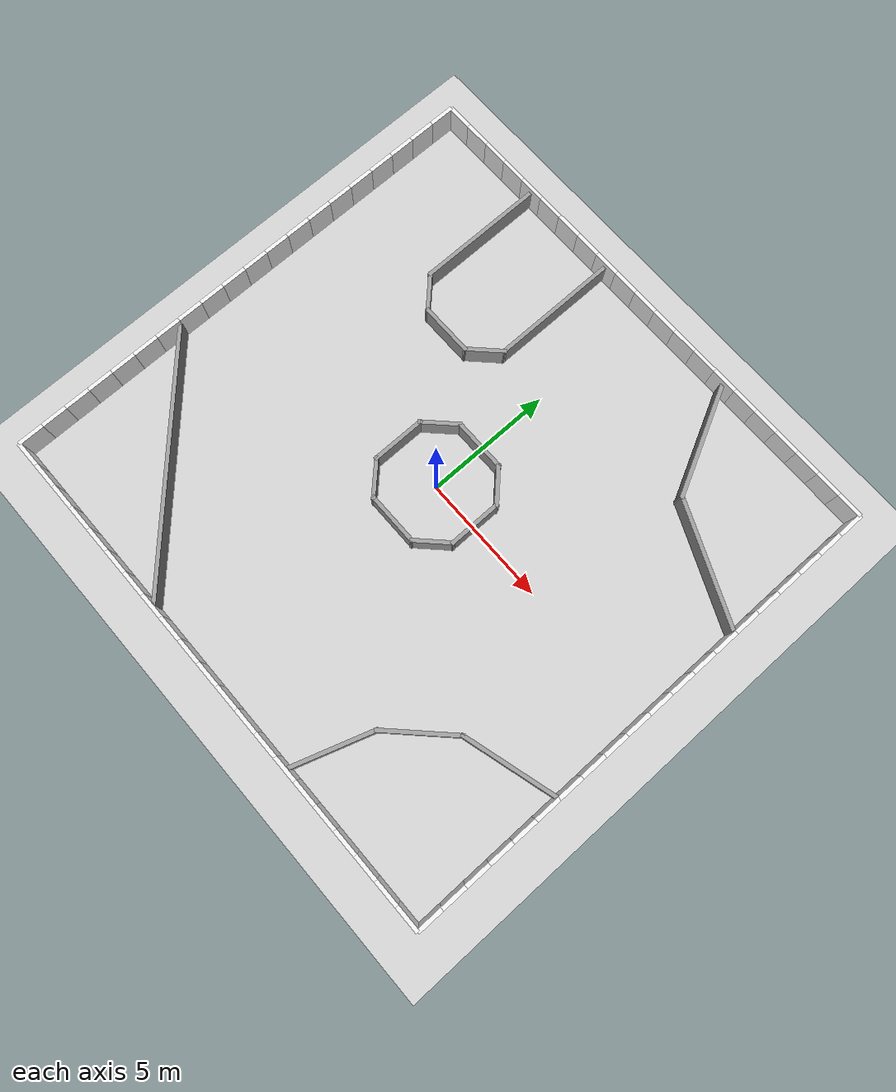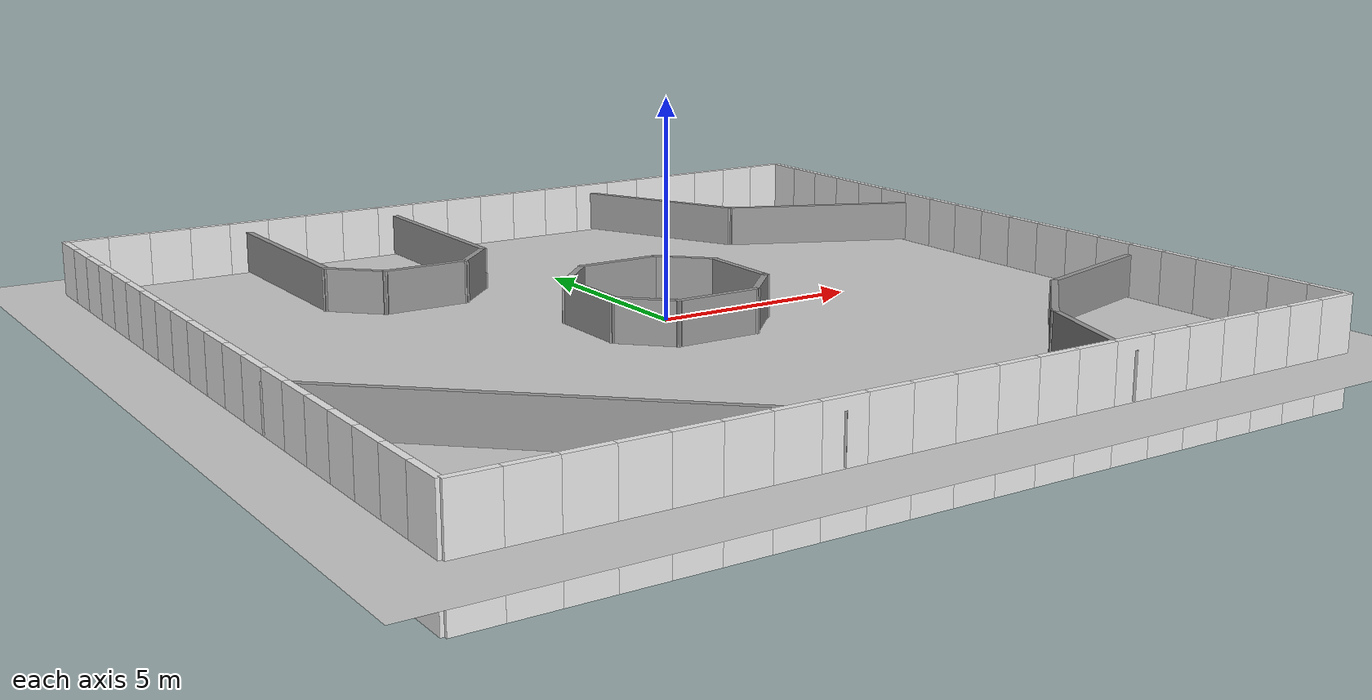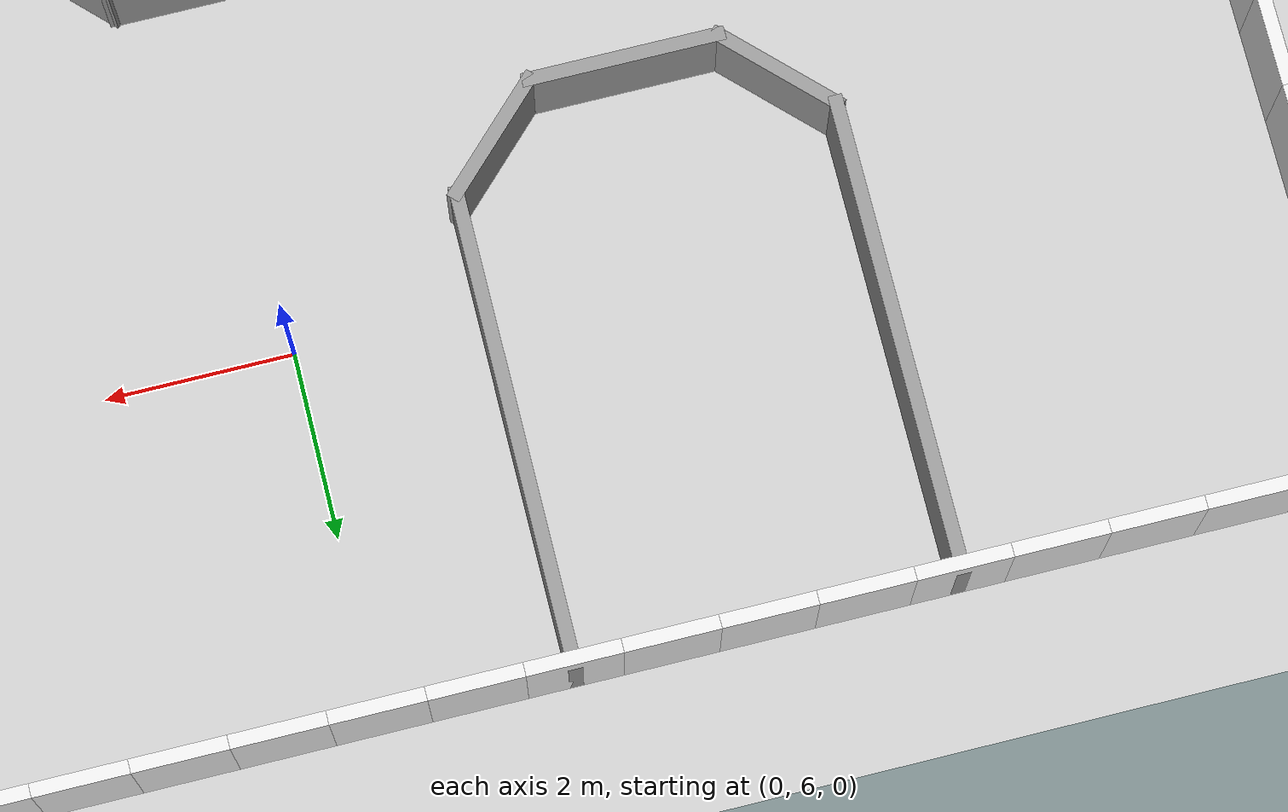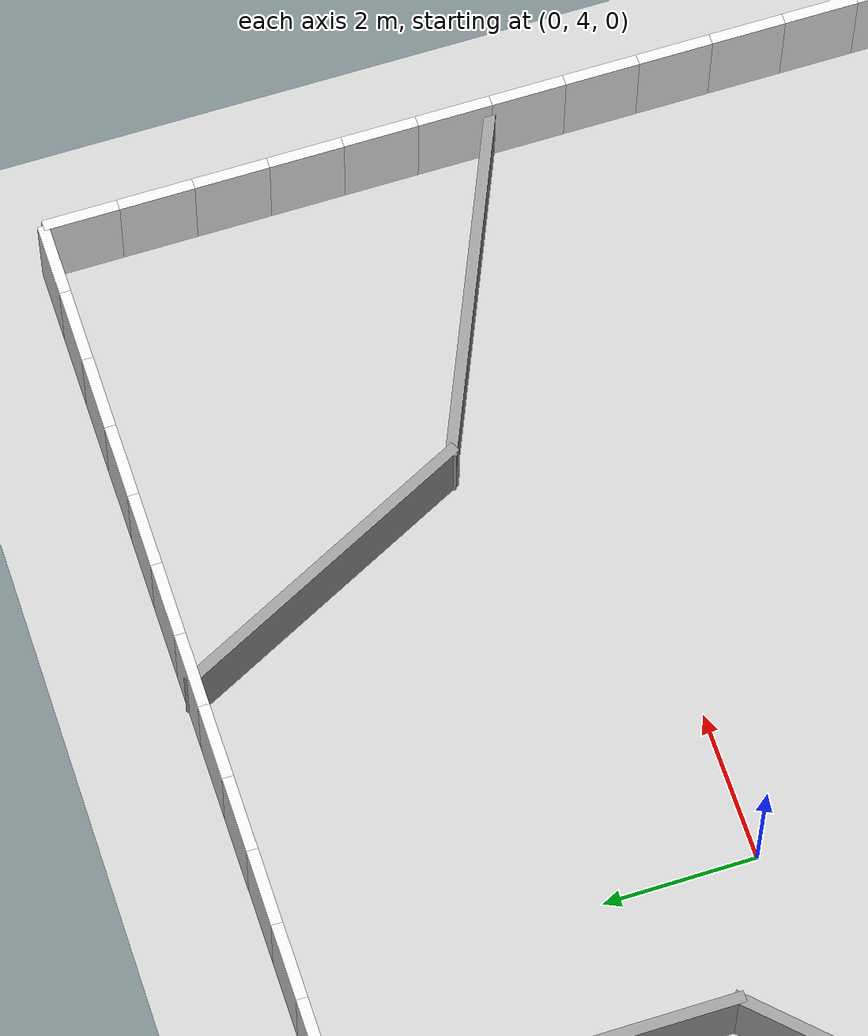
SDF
<sdf version="1.7">
 <world name="default">
  <light name="sun" type="directional">
   <pose>0 0 10 0 -0 0</pose>
   <diffuse>0.8 0.8 0.8 1</diffuse>
   <specular>0.2 0.2 0.2 1</specular>
   <attenuation>
    <range>1000</range>
    <constant>0.9</constant>
    <linear>0.01</linear>
    <quadratic>0.001</quadratic>
   </attenuation>
   <direction>-0.5 0.1 -0.9</direction>
   <spot><inner_angle>0</inner_angle><outer_angle>0</outer_angle><falloff>0</falloff></spot>
  </light>
  <model name="ground_plane">
   <static>1</static>
   <link name="link">
    <collision name="collision">
     <geometry><plane><normal>0 0 1</normal><size>100 100</size></plane></geometry>
     <surface>
      <contact><collide_bitmask>65535</collide_bitmask></contact>
      <friction><ode><mu>100</mu><mu2>50</mu2></ode></friction>
     </surface>
    </collision>
    <visual name="visual">
     <cast_shadows>0</cast_shadows>
     <geometry><plane><normal>0 0 1</normal><size>100 100</size></plane></geometry>
     <material>
      <script><uri>file://media/materials/scripts/gazebo.material</uri><name>Gazebo/Grey</name></script>
     </material>
    </visual>
   </link>
  </model>
  <model name="wall_left_01">
   <link name="Wall_10">
    <inertial>
     <mass>1</mass>
     <inertia><ixx>1</ixx><ixy>0</ixy><ixz>0</ixz><iyy>1</iyy><iyz>0</iyz><izz>1</izz></inertia>
    </inertial>
    <visual name="Wall_10_Visual_0">
     <geometry><box><size>1 0.15 2.5</size></box></geometry>
     <material>
      <script>
       <uri>model://wall/materials/scripts</uri>
       <uri>model://wall/materials/textures</uri>
       <name>wall_white</name>
      </script>
      <shader type="pixel"><normal_map>__default__</normal_map></shader>
      <ambient>1 1 1 1</ambient>
      <diffuse>1 1 1 1</diffuse>
      <specular>0 0 0 1</specular>
      <emissive>0 0 0 1</emissive>
     </material>
     <meta><layer>0</layer></meta>
    </visual>
    <collision name="Wall_10_Collision_0">
     <geometry><box><size>1 0.15 2.5</size></box></geometry>
     <surface>
      <friction>
       <ode><mu>1</mu><mu2>1</mu2><fdir1>0 0 0</fdir1><slip1>0</slip1><slip2>0</slip2></ode>
       <torsional>
        <coefficient>1</coefficient>
        <patch_radius>0</patch_radius>
        <surface_radius>0</surface_radius>
        <use_patch_radius>1</use_patch_radius>
        <ode><slip>0</slip></ode>
       </torsional>
      </friction>
      <bounce><restitution_coefficient>0</restitution_coefficient><threshold>1e+06</threshold></bounce>
      <contact>
       <collide_without_contact>0</collide_without_contact>
       <collide_without_contact_bitmask>1</collide_without_contact_bitmask>
       <collide_bitmask>1</collide_bitmask>
       <ode>
        <soft_cfm>0</soft_cfm>
        <soft_erp>0.2</soft_erp>
        <kp>1e+13</kp>
        <kd>1</kd>
        <max_vel>0.01</max_vel>
        <min_depth>0</min_depth>
       </ode>
       <bullet>
        <split_impulse>1</split_impulse>
        <split_impulse_penetration_threshold>-0.01</split_impulse_penetration_threshold>
        <soft_cfm>0</soft_cfm>
        <soft_erp>0.2</soft_erp>
        <kp>1e+13</kp>
        <kd>1</kd>
       </bullet>
      </contact>
     </surface>
    </collision>
   </link>
   <static>1</static>
   <pose>-10 10 0 0 -0 0</pose>
  </model>
  <model name="wall_left_02">
   <link name="Wall_10">
    <inertial>
     <mass>1</mass>
     <inertia><ixx>1</ixx><ixy>0</ixy><ixz>0</ixz><iyy>1</iyy><iyz>0</iyz><izz>1</izz></inertia>
    </inertial>
    <visual name="Wall_10_Visual_0">
     <geometry><box><size>1 0.15 2.5</size></box></geometry>
     <material>
      <script>
       <uri>model://wall/materials/scripts</uri>
       <uri>model://wall/materials/textures</uri>
       <name>wall_white</name>
      </script>
      <shader type="pixel"><normal_map>__default__</normal_map></shader>
      <ambient>1 1 1 1</ambient>
      <diffuse>1 1 1 1</diffuse>
      <specular>0 0 0 1</specular>
      <emissive>0 0 0 1</emissive>
     </material>
     <meta><layer>0</layer></meta>
    </visual>
    <collision name="Wall_10_Collision_0">
     <geometry><box><size>1 0.15 2.5</size></box></geometry>
     <surface>
      <friction>
       <ode><mu>1</mu><mu2>1</mu2><fdir1>0 0 0</fdir1><slip1>0</slip1><slip2>0</slip2></ode>
       <torsional>
        <coefficient>1</coefficient>
        <patch_radius>0</patch_radius>
        <surface_radius>0</surface_radius>
        <use_patch_radius>1</use_patch_radius>
        <ode><slip>0</slip></ode>
       </torsional>
      </friction>
      <bounce><restitution_coefficient>0</restitution_coefficient><threshold>1e+06</threshold></bounce>
      <contact>
       <collide_without_contact>0</collide_without_contact>
       <collide_without_contact_bitmask>1</collide_without_contact_bitmask>
       <collide_bitmask>1</collide_bitmask>
       <ode>
        <soft_cfm>0</soft_cfm>
        <soft_erp>0.2</soft_erp>
        <kp>1e+13</kp>
        <kd>1</kd>
        <max_vel>0.01</max_vel>
        <min_depth>0</min_depth>
       </ode>
       <bullet>
        <split_impulse>1</split_impulse>
        <split_impulse_penetration_threshold>-0.01</split_impulse_penetration_threshold>
        <soft_cfm>0</soft_cfm>
        <soft_erp>0.2</soft_erp>
        <kp>1e+13</kp>
        <kd>1</kd>
       </bullet>
      </contact>
     </surface>
    </collision>
   </link>
   <static>1</static>
   <pose>-9 10 0 0 -0 0</pose>
  </model>
  <model name="wall_left_03">
   <link name="Wall_10">
    <inertial>
     <mass>1</mass>
     <inertia><ixx>1</ixx><ixy>0</ixy><ixz>0</ixz><iyy>1</iyy><iyz>0</iyz><izz>1</izz></inertia>
    </inertial>
    <visual name="Wall_10_Visual_0">
     <geometry><box><size>1 0.15 2.5</size></box></geometry>
     <material>
      <script>
       <uri>model://wall/materials/scripts</uri>
       <uri>model://wall/materials/textures</uri>
       <name>wall_white</name>
      </script>
      <shader type="pixel"><normal_map>__default__</normal_map></shader>
      <ambient>1 1 1 1</ambient>
      <diffuse>1 1 1 1</diffuse>
      <specular>0 0 0 1</specular>
      <emissive>0 0 0 1</emissive>
     </material>
     <meta><layer>0</layer></meta>
    </visual>
    <collision name="Wall_10_Collision_0">
     <geometry><box><size>1 0.15 2.5</size></box></geometry>
     <surface>
      <friction>
       <ode><mu>1</mu><mu2>1</mu2><fdir1>0 0 0</fdir1><slip1>0</slip1><slip2>0</slip2></ode>
       <torsional>
        <coefficient>1</coefficient>
        <patch_radius>0</patch_radius>
        <surface_radius>0</surface_radius>
        <use_patch_radius>1</use_patch_radius>
        <ode><slip>0</slip></ode>
       </torsional>
      </friction>
      <bounce><restitution_coefficient>0</restitution_coefficient><threshold>1e+06</threshold></bounce>
      <contact>
       <collide_without_contact>0</collide_without_contact>
       <collide_without_contact_bitmask>1</collide_without_contact_bitmask>
       <collide_bitmask>1</collide_bitmask>
       <ode>
        <soft_cfm>0</soft_cfm>
        <soft_erp>0.2</soft_erp>
        <kp>1e+13</kp>
        <kd>1</kd>
        <max_vel>0.01</max_vel>
        <min_depth>0</min_depth>
       </ode>
       <bullet>
        <split_impulse>1</split_impulse>
        <split_impulse_penetration_threshold>-0.01</split_impulse_penetration_threshold>
        <soft_cfm>0</soft_cfm>
        <soft_erp>0.2</soft_erp>
        <kp>1e+13</kp>
        <kd>1</kd>
       </bullet>
      </contact>
     </surface>
    </collision>
   </link>
   <static>1</static>
   <pose>-8 10 0 0 -0 0</pose>
  </model>
  <model name="wall_left_04">
   <link name="Wall_10">
    <inertial>
     <mass>1</mass>
     <inertia><ixx>1</ixx><ixy>0</ixy><ixz>0</ixz><iyy>1</iyy><iyz>0</iyz><izz>1</izz></inertia>
    </inertial>
    <visual name="Wall_10_Visual_0">
     <geometry><box><size>1 0.15 2.5</size></box></geometry>
     <material>
      <script>
       <uri>model://wall/materials/scripts</uri>
       <uri>model://wall/materials/textures</uri>
       <name>wall_white</name>
      </script>
      <shader type="pixel"><normal_map>__default__</normal_map></shader>
      <ambient>1 1 1 1</ambient>
      <diffuse>1 1 1 1</diffuse>
      <specular>0 0 0 1</specular>
      <emissive>0 0 0 1</emissive>
     </material>
     <meta><layer>0</layer></meta>
    </visual>
    <collision name="Wall_10_Collision_0">
     <geometry><box><size>1 0.15 2.5</size></box></geometry>
     <surface>
      <friction>
       <ode><mu>1</mu><mu2>1</mu2><fdir1>0 0 0</fdir1><slip1>0</slip1><slip2>0</slip2></ode>
       <torsional>
        <coefficient>1</coefficient>
        <patch_radius>0</patch_radius>
        <surface_radius>0</surface_radius>
        <use_patch_radius>1</use_patch_radius>
        <ode><slip>0</slip></ode>
       </torsional>
      </friction>
      <bounce><restitution_coefficient>0</restitution_coefficient><threshold>1e+06</threshold></bounce>
      <contact>
       <collide_without_contact>0</collide_without_contact>
       <collide_without_contact_bitmask>1</collide_without_contact_bitmask>
       <collide_bitmask>1</collide_bitmask>
       <ode>
        <soft_cfm>0</soft_cfm>
        <soft_erp>0.2</soft_erp>
        <kp>1e+13</kp>
        <kd>1</kd>
        <max_vel>0.01</max_vel>
        <min_depth>0</min_depth>
       </ode>
       <bullet>
        <split_impulse>1</split_impulse>
        <split_impulse_penetration_threshold>-0.01</split_impulse_penetration_threshold>
        <soft_cfm>0</soft_cfm>
        <soft_erp>0.2</soft_erp>
        <kp>1e+13</kp>
        <kd>1</kd>
       </bullet>
      </contact>
     </surface>
    </collision>
   </link>
   <static>1</static>
   <pose>-7 10 0 0 -0 0</pose>
  </model>
  <model name="wall_left_05">
   <link name="Wall_10">
    <inertial>
     <mass>1</mass>
     <inertia><ixx>1</ixx><ixy>0</ixy><ixz>0</ixz><iyy>1</iyy><iyz>0</iyz><izz>1</izz></inertia>
    </inertial>
    <visual name="Wall_10_Visual_0">
     <geometry><box><size>1 0.15 2.5</size></box></geometry>
     <material>
      <script>
       <uri>model://wall/materials/scripts</uri>
       <uri>model://wall/materials/textures</uri>
       <name>wall_white</name>
      </script>
      <shader type="pixel"><normal_map>__default__</normal_map></shader>
      <ambient>1 1 1 1</ambient>
      <diffuse>1 1 1 1</diffuse>
      <specular>0 0 0 1</specular>
      <emissive>0 0 0 1</emissive>
     </material>
     <meta><layer>0</layer></meta>
    </visual>
    <collision name="Wall_10_Collision_0">
     <geometry><box><size>1 0.15 2.5</size></box></geometry>
     <surface>
      <friction>
       <ode><mu>1</mu><mu2>1</mu2><fdir1>0 0 0</fdir1><slip1>0</slip1><slip2>0</slip2></ode>
       <torsional>
        <coefficient>1</coefficient>
        <patch_radius>0</patch_radius>
        <surface_radius>0</surface_radius>
        <use_patch_radius>1</use_patch_radius>
        <ode><slip>0</slip></ode>
       </torsional>
      </friction>
      <bounce><restitution_coefficient>0</restitution_coefficient><threshold>1e+06</threshold></bounce>
      <contact>
       <collide_without_contact>0</collide_without_contact>
       <collide_without_contact_bitmask>1</collide_without_contact_bitmask>
       <collide_bitmask>1</collide_bitmask>
       <ode>
        <soft_cfm>0</soft_cfm>
        <soft_erp>0.2</soft_erp>
        <kp>1e+13</kp>
        <kd>1</kd>
        <max_vel>0.01</max_vel>
        <min_depth>0</min_depth>
       </ode>
       <bullet>
        <split_impulse>1</split_impulse>
        <split_impulse_penetration_threshold>-0.01</split_impulse_penetration_threshold>
        <soft_cfm>0</soft_cfm>
        <soft_erp>0.2</soft_erp>
        <kp>1e+13</kp>
        <kd>1</kd>
       </bullet>
      </contact>
     </surface>
    </collision>
   </link>
   <static>1</static>
   <pose>-6 10 0 0 -0 0</pose>
  </model>
  <model name="wall_left_06">
   <link name="Wall_10">
    <inertial>
     <mass>1</mass>
     <inertia><ixx>1</ixx><ixy>0</ixy><ixz>0</ixz><iyy>1</iyy><iyz>0</iyz><izz>1</izz></inertia>
    </inertial>
    <visual name="Wall_10_Visual_0">
     <geometry><box><size>1 0.15 2.5</size></box></geometry>
     <material>
      <script>
       <uri>model://wall/materials/scripts</uri>
       <uri>model://wall/materials/textures</uri>
       <name>wall_white</name>
      </script>
      <shader type="pixel"><normal_map>__default__</normal_map></shader>
      <ambient>1 1 1 1</ambient>
      <diffuse>1 1 1 1</diffuse>
      <specular>0 0 0 1</specular>
      <emissive>0 0 0 1</emissive>
     </material>
     <meta><layer>0</layer></meta>
    </visual>
    <collision name="Wall_10_Collision_0">
     <geometry><box><size>1 0.15 2.5</size></box></geometry>
     <surface>
      <friction>
       <ode><mu>1</mu><mu2>1</mu2><fdir1>0 0 0</fdir1><slip1>0</slip1><slip2>0</slip2></ode>
       <torsional>
        <coefficient>1</coefficient>
        <patch_radius>0</patch_radius>
        <surface_radius>0</surface_radius>
        <use_patch_radius>1</use_patch_radius>
        <ode><slip>0</slip></ode>
       </torsional>
      </friction>
      <bounce><restitution_coefficient>0</restitution_coefficient><threshold>1e+06</threshold></bounce>
      <contact>
       <collide_without_contact>0</collide_without_contact>
       <collide_without_contact_bitmask>1</collide_without_contact_bitmask>
       <collide_bitmask>1</collide_bitmask>
       <ode>
        <soft_cfm>0</soft_cfm>
        <soft_erp>0.2</soft_erp>
        <kp>1e+13</kp>
        <kd>1</kd>
        <max_vel>0.01</max_vel>
        <min_depth>0</min_depth>
       </ode>
       <bullet>
        <split_impulse>1</split_impulse>
        <split_impulse_penetration_threshold>-0.01</split_impulse_penetration_threshold>
        <soft_cfm>0</soft_cfm>
        <soft_erp>0.2</soft_erp>
        <kp>1e+13</kp>
        <kd>1</kd>
       </bullet>
      </contact>
     </surface>
    </collision>
   </link>
   <static>1</static>
   <pose>-5 10 0 0 -0 0</pose>
  </model>
  <model name="wall_left_07">
   <link name="Wall_10">
    <inertial>
     <mass>1</mass>
     <inertia><ixx>1</ixx><ixy>0</ixy><ixz>0</ixz><iyy>1</iyy><iyz>0</iyz><izz>1</izz></inertia>
    </inertial>
    <visual name="Wall_10_Visual_0">
     <geometry><box><size>1 0.15 2.5</size></box></geometry>
     <material>
      <script>
       <uri>model://wall/materials/scripts</uri>
       <uri>model://wall/materials/textures</uri>
       <name>wall_white</name>
      </script>
      <shader type="pixel"><normal_map>__default__</normal_map></shader>
      <ambient>1 1 1 1</ambient>
      <diffuse>1 1 1 1</diffuse>
      <specular>0 0 0 1</specular>
      <emissive>0 0 0 1</emissive>
     </material>
     <meta><layer>0</layer></meta>
    </visual>
    <collision name="Wall_10_Collision_0">
     <geometry><box><size>1 0.15 2.5</size></box></geometry>
     <surface>
      <friction>
       <ode><mu>1</mu><mu2>1</mu2><fdir1>0 0 0</fdir1><slip1>0</slip1><slip2>0</slip2></ode>
       <torsional>
        <coefficient>1</coefficient>
        <patch_radius>0</patch_radius>
        <surface_radius>0</surface_radius>
        <use_patch_radius>1</use_patch_radius>
        <ode><slip>0</slip></ode>
       </torsional>
      </friction>
      <bounce><restitution_coefficient>0</restitution_coefficient><threshold>1e+06</threshold></bounce>
      <contact>
       <collide_without_contact>0</collide_without_contact>
       <collide_without_contact_bitmask>1</collide_without_contact_bitmask>
       <collide_bitmask>1</collide_bitmask>
       <ode>
        <soft_cfm>0</soft_cfm>
        <soft_erp>0.2</soft_erp>
        <kp>1e+13</kp>
        <kd>1</kd>
        <max_vel>0.01</max_vel>
        <min_depth>0</min_depth>
       </ode>
       <bullet>
        <split_impulse>1</split_impulse>
        <split_impulse_penetration_threshold>-0.01</split_impulse_penetration_threshold>
        <soft_cfm>0</soft_cfm>
        <soft_erp>0.2</soft_erp>
        <kp>1e+13</kp>
        <kd>1</kd>
       </bullet>
      </contact>
     </surface>
    </collision>
   </link>
   <static>1</static>
   <pose>-4 10 0 0 -0 0</pose>
  </model>
  <model name="wall_left_08">
   <link name="Wall_10">
    <inertial>
     <mass>1</mass>
     <inertia><ixx>1</ixx><ixy>0</ixy><ixz>0</ixz><iyy>1</iyy><iyz>0</iyz><izz>1</izz></inertia>
    </inertial>
    <visual name="Wall_10_Visual_0">
     <geometry><box><size>1 0.15 2.5</size></box></geometry>
     <material>
      <script>
       <uri>model://wall/materials/scripts</uri>
       <uri>model://wall/materials/textures</uri>
       <name>wall_white</name>
      </script>
      <shader type="pixel"><normal_map>__default__</normal_map></shader>
      <ambient>1 1 1 1</ambient>
      <diffuse>1 1 1 1</diffuse>
      <specular>0 0 0 1</specular>
      <emissive>0 0 0 1</emissive>
     </material>
     <meta><layer>0</layer></meta>
    </visual>
    <collision name="Wall_10_Collision_0">
     <geometry><box><size>1 0.15 2.5</size></box></geometry>
     <surface>
      <friction>
       <ode><mu>1</mu><mu2>1</mu2><fdir1>0 0 0</fdir1><slip1>0</slip1><slip2>0</slip2></ode>
       <torsional>
        <coefficient>1</coefficient>
        <patch_radius>0</patch_radius>
        <surface_radius>0</surface_radius>
        <use_patch_radius>1</use_patch_radius>
        <ode><slip>0</slip></ode>
       </torsional>
      </friction>
      <bounce><restitution_coefficient>0</restitution_coefficient><threshold>1e+06</threshold></bounce>
      <contact>
       <collide_without_contact>0</collide_without_contact>
       <collide_without_contact_bitmask>1</collide_without_contact_bitmask>
       <collide_bitmask>1</collide_bitmask>
       <ode>
        <soft_cfm>0</soft_cfm>
        <soft_erp>0.2</soft_erp>
        <kp>1e+13</kp>
        <kd>1</kd>
        <max_vel>0.01</max_vel>
        <min_depth>0</min_depth>
       </ode>
       <bullet>
        <split_impulse>1</split_impulse>
        <split_impulse_penetration_threshold>-0.01</split_impulse_penetration_threshold>
        <soft_cfm>0</soft_cfm>
        <soft_erp>0.2</soft_erp>
        <kp>1e+13</kp>
        <kd>1</kd>
       </bullet>
      </contact>
     </surface>
    </collision>
   </link>
   <static>1</static>
   <pose>-3 10 0 0 -0 0</pose>
  </model>
  <model name="wall_left_09">
   <link name="Wall_10">
    <inertial>
     <mass>1</mass>
     <inertia><ixx>1</ixx><ixy>0</ixy><ixz>0</ixz><iyy>1</iyy><iyz>0</iyz><izz>1</izz></inertia>
    </inertial>
    <visual name="Wall_10_Visual_0">
     <geometry><box><size>1 0.15 2.5</size></box></geometry>
     <material>
      <script>
       <uri>model://wall/materials/scripts</uri>
       <uri>model://wall/materials/textures</uri>
       <name>wall_white</name>
      </script>
      <shader type="pixel"><normal_map>__default__</normal_map></shader>
      <ambient>1 1 1 1</ambient>
      <diffuse>1 1 1 1</diffuse>
      <specular>0 0 0 1</specular>
      <emissive>0 0 0 1</emissive>
     </material>
     <meta><layer>0</layer></meta>
    </visual>
    <collision name="Wall_10_Collision_0">
     <geometry><box><size>1 0.15 2.5</size></box></geometry>
     <surface>
      <friction>
       <ode><mu>1</mu><mu2>1</mu2><fdir1>0 0 0</fdir1><slip1>0</slip1><slip2>0</slip2></ode>
       <torsional>
        <coefficient>1</coefficient>
        <patch_radius>0</patch_radius>
        <surface_radius>0</surface_radius>
        <use_patch_radius>1</use_patch_radius>
        <ode><slip>0</slip></ode>
       </torsional>
      </friction>
      <bounce><restitution_coefficient>0</restitution_coefficient><threshold>1e+06</threshold></bounce>
      <contact>
       <collide_without_contact>0</collide_without_contact>
       <collide_without_contact_bitmask>1</collide_without_contact_bitmask>
       <collide_bitmask>1</collide_bitmask>
       <ode>
        <soft_cfm>0</soft_cfm>
        <soft_erp>0.2</soft_erp>
        <kp>1e+13</kp>
        <kd>1</kd>
        <max_vel>0.01</max_vel>
        <min_depth>0</min_depth>
       </ode>
       <bullet>
        <split_impulse>1</split_impulse>
        <split_impulse_penetration_threshold>-0.01</split_impulse_penetration_threshold>
        <soft_cfm>0</soft_cfm>
        <soft_erp>0.2</soft_erp>
        <kp>1e+13</kp>
        <kd>1</kd>
       </bullet>
      </contact>
     </surface>
    </collision>
   </link>
   <static>1</static>
   <pose>-2 10 0 0 -0 0</pose>
  </model>
  <model name="wall_left_10">
   <link name="Wall_10">
    <inertial>
     <mass>1</mass>
     <inertia><ixx>1</ixx><ixy>0</ixy><ixz>0</ixz><iyy>1</iyy><iyz>0</iyz><izz>1</izz></inertia>
    </inertial>
    <visual name="Wall_10_Visual_0">
     <geometry><box><size>1 0.15 2.5</size></box></geometry>
     <material>
      <script>
       <uri>model://wall/materials/scripts</uri>
       <uri>model://wall/materials/textures</uri>
       <name>wall_white</name>
      </script>
      <shader type="pixel"><normal_map>__default__</normal_map></shader>
      <ambient>1 1 1 1</ambient>
      <diffuse>1 1 1 1</diffuse>
      <specular>0 0 0 1</specular>
      <emissive>0 0 0 1</emissive>
     </material>
     <meta><layer>0</layer></meta>
    </visual>
    <collision name="Wall_10_Collision_0">
     <geometry><box><size>1 0.15 2.5</size></box></geometry>
     <surface>
      <friction>
       <ode><mu>1</mu><mu2>1</mu2><fdir1>0 0 0</fdir1><slip1>0</slip1><slip2>0</slip2></ode>
       <torsional>
        <coefficient>1</coefficient>
        <patch_radius>0</patch_radius>
        <surface_radius>0</surface_radius>
        <use_patch_radius>1</use_patch_radius>
        <ode><slip>0</slip></ode>
       </torsional>
      </friction>
      <bounce><restitution_coefficient>0</restitution_coefficient><threshold>1e+06</threshold></bounce>
      <contact>
       <collide_without_contact>0</collide_without_contact>
       <collide_without_contact_bitmask>1</collide_without_contact_bitmask>
       <collide_bitmask>1</collide_bitmask>
       <ode>
        <soft_cfm>0</soft_cfm>
        <soft_erp>0.2</soft_erp>
        <kp>1e+13</kp>
        <kd>1</kd>
        <max_vel>0.01</max_vel>
        <min_depth>0</min_depth>
       </ode>
       <bullet>
        <split_impulse>1</split_impulse>
        <split_impulse_penetration_threshold>-0.01</split_impulse_penetration_threshold>
        <soft_cfm>0</soft_cfm>
        <soft_erp>0.2</soft_erp>
        <kp>1e+13</kp>
        <kd>1</kd>
       </bullet>
      </contact>
     </surface>
    </collision>
   </link>
   <static>1</static>
   <pose>-1 10 0 0 -0 0</pose>
  </model>
  <model name="wall_left_11">
   <link name="Wall_10">
    <inertial>
     <mass>1</mass>
     <inertia><ixx>1</ixx><ixy>0</ixy><ixz>0</ixz><iyy>1</iyy><iyz>0</iyz><izz>1</izz></inertia>
    </inertial>
    <visual name="Wall_10_Visual_0">
     <geometry><box><size>1 0.15 2.5</size></box></geometry>
     <material>
      <script>
       <uri>model://wall/materials/scripts</uri>
       <uri>model://wall/materials/textures</uri>
       <name>wall_white</name>
      </script>
      <shader type="pixel"><normal_map>__default__</normal_map></shader>
      <ambient>1 1 1 1</ambient>
      <diffuse>1 1 1 1</diffuse>
      <specular>0 0 0 1</specular>
      <emissive>0 0 0 1</emissive>
     </material>
     <meta><layer>0</layer></meta>
    </visual>
    <collision name="Wall_10_Collision_0">
     <geometry><box><size>1 0.15 2.5</size></box></geometry>
     <surface>
      <friction>
       <ode><mu>1</mu><mu2>1</mu2><fdir1>0 0 0</fdir1><slip1>0</slip1><slip2>0</slip2></ode>
       <torsional>
        <coefficient>1</coefficient>
        <patch_radius>0</patch_radius>
        <surface_radius>0</surface_radius>
        <use_patch_radius>1</use_patch_radius>
        <ode><slip>0</slip></ode>
       </torsional>
      </friction>
      <bounce><restitution_coefficient>0</restitution_coefficient><threshold>1e+06</threshold></bounce>
      <contact>
       <collide_without_contact>0</collide_without_contact>
       <collide_without_contact_bitmask>1</collide_without_contact_bitmask>
       <collide_bitmask>1</collide_bitmask>
       <ode>
        <soft_cfm>0</soft_cfm>
        <soft_erp>0.2</soft_erp>
        <kp>1e+13</kp>
        <kd>1</kd>
        <max_vel>0.01</max_vel>
        <min_depth>0</min_depth>
       </ode>
       <bullet>
        <split_impulse>1</split_impulse>
        <split_impulse_penetration_threshold>-0.01</split_impulse_penetration_threshold>
        <soft_cfm>0</soft_cfm>
        <soft_erp>0.2</soft_erp>
        <kp>1e+13</kp>
        <kd>1</kd>
       </bullet>
      </contact>
     </surface>
    </collision>
   </link>
   <static>1</static>
   <pose>0 10 0 0 -0 0</pose>
  </model>
  <model name="wall_left_12">
   <link name="Wall_10">
    <inertial>
     <mass>1</mass>
     <inertia><ixx>1</ixx><ixy>0</ixy><ixz>0</ixz><iyy>1</iyy><iyz>0</iyz><izz>1</izz></inertia>
    </inertial>
    <visual name="Wall_10_Visual_0">
     <geometry><box><size>1 0.15 2.5</size></box></geometry>
     <material>
      <script>
       <uri>model://wall/materials/scripts</uri>
       <uri>model://wall/materials/textures</uri>
       <name>wall_white</name>
      </script>
      <shader type="pixel"><normal_map>__default__</normal_map></shader>
      <ambient>1 1 1 1</ambient>
      <diffuse>1 1 1 1</diffuse>
      <specular>0 0 0 1</specular>
      <emissive>0 0 0 1</emissive>
     </material>
     <meta><layer>0</layer></meta>
    </visual>
    <collision name="Wall_10_Collision_0">
     <geometry><box><size>1 0.15 2.5</size></box></geometry>
     <surface>
      <friction>
       <ode><mu>1</mu><mu2>1</mu2><fdir1>0 0 0</fdir1><slip1>0</slip1><slip2>0</slip2></ode>
       <torsional>
        <coefficient>1</coefficient>
        <patch_radius>0</patch_radius>
        <surface_radius>0</surface_radius>
        <use_patch_radius>1</use_patch_radius>
        <ode><slip>0</slip></ode>
       </torsional>
      </friction>
      <bounce><restitution_coefficient>0</restitution_coefficient><threshold>1e+06</threshold></bounce>
      <contact>
       <collide_without_contact>0</collide_without_contact>
       <collide_without_contact_bitmask>1</collide_without_contact_bitmask>
       <collide_bitmask>1</collide_bitmask>
       <ode>
        <soft_cfm>0</soft_cfm>
        <soft_erp>0.2</soft_erp>
        <kp>1e+13</kp>
        <kd>1</kd>
        <max_vel>0.01</max_vel>
        <min_depth>0</min_depth>
       </ode>
       <bullet>
        <split_impulse>1</split_impulse>
        <split_impulse_penetration_threshold>-0.01</split_impulse_penetration_threshold>
        <soft_cfm>0</soft_cfm>
        <soft_erp>0.2</soft_erp>
        <kp>1e+13</kp>
        <kd>1</kd>
       </bullet>
      </contact>
     </surface>
    </collision>
   </link>
   <static>1</static>
   <pose>1 10 0 0 -0 0</pose>
  </model>
  <model name="wall_left_13">
   <link name="Wall_10">
    <inertial>
     <mass>1</mass>
     <inertia><ixx>1</ixx><ixy>0</ixy><ixz>0</ixz><iyy>1</iyy><iyz>0</iyz><izz>1</izz></inertia>
    </inertial>
    <visual name="Wall_10_Visual_0">
     <geometry><box><size>1 0.15 2.5</size></box></geometry>
     <material>
      <script>
       <uri>model://wall/materials/scripts</uri>
       <uri>model://wall/materials/textures</uri>
       <name>wall_white</name>
      </script>
      <shader type="pixel"><normal_map>__default__</normal_map></shader>
      <ambient>1 1 1 1</ambient>
      <diffuse>1 1 1 1</diffuse>
      <specular>0 0 0 1</specular>
      <emissive>0 0 0 1</emissive>
     </material>
     <meta><layer>0</layer></meta>
    </visual>
    <collision name="Wall_10_Collision_0">
     <geometry><box><size>1 0.15 2.5</size></box></geometry>
     <surface>
      <friction>
       <ode><mu>1</mu><mu2>1</mu2><fdir1>0 0 0</fdir1><slip1>0</slip1><slip2>0</slip2></ode>
       <torsional>
        <coefficient>1</coefficient>
        <patch_radius>0</patch_radius>
        <surface_radius>0</surface_radius>
        <use_patch_radius>1</use_patch_radius>
        <ode><slip>0</slip></ode>
       </torsional>
      </friction>
      <bounce><restitution_coefficient>0</restitution_coefficient><threshold>1e+06</threshold></bounce>
      <contact>
       <collide_without_contact>0</collide_without_contact>
       <collide_without_contact_bitmask>1</collide_without_contact_bitmask>
       <collide_bitmask>1</collide_bitmask>
       <ode>
        <soft_cfm>0</soft_cfm>
        <soft_erp>0.2</soft_erp>
        <kp>1e+13</kp>
        <kd>1</kd>
        <max_vel>0.01</max_vel>
        <min_depth>0</min_depth>
       </ode>
       <bullet>
        <split_impulse>1</split_impulse>
        <split_impulse_penetration_threshold>-0.01</split_impulse_penetration_threshold>
        <soft_cfm>0</soft_cfm>
        <soft_erp>0.2</soft_erp>
        <kp>1e+13</kp>
        <kd>1</kd>
       </bullet>
      </contact>
     </surface>
    </collision>
   </link>
   <static>1</static>
   <pose>2 10 0 0 -0 0</pose>
  </model>
  <model name="wall_left_14">
   <link name="Wall_10">
    <inertial>
     <mass>1</mass>
     <inertia><ixx>1</ixx><ixy>0</ixy><ixz>0</ixz><iyy>1</iyy><iyz>0</iyz><izz>1</izz></inertia>
    </inertial>
    <visual name="Wall_10_Visual_0">
     <geometry><box><size>1 0.15 2.5</size></box></geometry>
     <material>
      <script>
       <uri>model://wall/materials/scripts</uri>
       <uri>model://wall/materials/textures</uri>
       <name>wall_white</name>
      </script>
      <shader type="pixel"><normal_map>__default__</normal_map></shader>
      <ambient>1 1 1 1</ambient>
      <diffuse>1 1 1 1</diffuse>
      <specular>0 0 0 1</specular>
      <emissive>0 0 0 1</emissive>
     </material>
     <meta><layer>0</layer></meta>
    </visual>
    <collision name="Wall_10_Collision_0">
     <geometry><box><size>1 0.15 2.5</size></box></geometry>
     <surface>
      <friction>
       <ode><mu>1</mu><mu2>1</mu2><fdir1>0 0 0</fdir1><slip1>0</slip1><slip2>0</slip2></ode>
       <torsional>
        <coefficient>1</coefficient>
        <patch_radius>0</patch_radius>
        <surface_radius>0</surface_radius>
        <use_patch_radius>1</use_patch_radius>
        <ode><slip>0</slip></ode>
       </torsional>
      </friction>
      <bounce><restitution_coefficient>0</restitution_coefficient><threshold>1e+06</threshold></bounce>
      <contact>
       <collide_without_contact>0</collide_without_contact>
       <collide_without_contact_bitmask>1</collide_without_contact_bitmask>
       <collide_bitmask>1</collide_bitmask>
       <ode>
        <soft_cfm>0</soft_cfm>
        <soft_erp>0.2</soft_erp>
        <kp>1e+13</kp>
        <kd>1</kd>
        <max_vel>0.01</max_vel>
        <min_depth>0</min_depth>
       </ode>
       <bullet>
        <split_impulse>1</split_impulse>
        <split_impulse_penetration_threshold>-0.01</split_impulse_penetration_threshold>
        <soft_cfm>0</soft_cfm>
        <soft_erp>0.2</soft_erp>
        <kp>1e+13</kp>
        <kd>1</kd>
       </bullet>
      </contact>
     </surface>
    </collision>
   </link>
   <static>1</static>
   <pose>3 10 0 0 -0 0</pose>
  </model>
  <model name="wall_left_15">
   <link name="Wall_10">
    <inertial>
     <mass>1</mass>
     <inertia><ixx>1</ixx><ixy>0</ixy><ixz>0</ixz><iyy>1</iyy><iyz>0</iyz><izz>1</izz></inertia>
    </inertial>
    <visual name="Wall_10_Visual_0">
     <geometry><box><size>1 0.15 2.5</size></box></geometry>
     <material>
      <script>
       <uri>model://wall/materials/scripts</uri>
       <uri>model://wall/materials/textures</uri>
       <name>wall_white</name>
      </script>
      <shader type="pixel"><normal_map>__default__</normal_map></shader>
      <ambient>1 1 1 1</ambient>
      <diffuse>1 1 1 1</diffuse>
      <specular>0 0 0 1</specular>
      <emissive>0 0 0 1</emissive>
     </material>
     <meta><layer>0</layer></meta>
    </visual>
    <collision name="Wall_10_Collision_0">
     <geometry><box><size>1 0.15 2.5</size></box></geometry>
     <surface>
      <friction>
       <ode><mu>1</mu><mu2>1</mu2><fdir1>0 0 0</fdir1><slip1>0</slip1><slip2>0</slip2></ode>
       <torsional>
        <coefficient>1</coefficient>
        <patch_radius>0</patch_radius>
        <surface_radius>0</surface_radius>
        <use_patch_radius>1</use_patch_radius>
        <ode><slip>0</slip></ode>
       </torsional>
      </friction>
      <bounce><restitution_coefficient>0</restitution_coefficient><threshold>1e+06</threshold></bounce>
      <contact>
       <collide_without_contact>0</collide_without_contact>
       <collide_without_contact_bitmask>1</collide_without_contact_bitmask>
       <collide_bitmask>1</collide_bitmask>
       <ode>
        <soft_cfm>0</soft_cfm>
        <soft_erp>0.2</soft_erp>
        <kp>1e+13</kp>
        <kd>1</kd>
        <max_vel>0.01</max_vel>
        <min_depth>0</min_depth>
       </ode>
       <bullet>
        <split_impulse>1</split_impulse>
        <split_impulse_penetration_threshold>-0.01</split_impulse_penetration_threshold>
        <soft_cfm>0</soft_cfm>
        <soft_erp>0.2</soft_erp>
        <kp>1e+13</kp>
        <kd>1</kd>
       </bullet>
      </contact>
     </surface>
    </collision>
   </link>
   <static>1</static>
   <pose>4 10 0 0 -0 0</pose>
  </model>
  <model name="wall_left_16">
   <link name="Wall_10">
    <inertial>
     <mass>1</mass>
     <inertia><ixx>1</ixx><ixy>0</ixy><ixz>0</ixz><iyy>1</iyy><iyz>0</iyz><izz>1</izz></inertia>
    </inertial>
    <visual name="Wall_10_Visual_0">
     <geometry><box><size>1 0.15 2.5</size></box></geometry>
     <material>
      <script>
       <uri>model://wall/materials/scripts</uri>
       <uri>model://wall/materials/textures</uri>
       <name>wall_white</name>
      </script>
      <shader type="pixel"><normal_map>__default__</normal_map></shader>
      <ambient>1 1 1 1</ambient>
      <diffuse>1 1 1 1</diffuse>
      <specular>0 0 0 1</specular>
      <emissive>0 0 0 1</emissive>
     </material>
     <meta><layer>0</layer></meta>
    </visual>
    <collision name="Wall_10_Collision_0">
     <geometry><box><size>1 0.15 2.5</size></box></geometry>
     <surface>
      <friction>
       <ode><mu>1</mu><mu2>1</mu2><fdir1>0 0 0</fdir1><slip1>0</slip1><slip2>0</slip2></ode>
       <torsional>
        <coefficient>1</coefficient>
        <patch_radius>0</patch_radius>
        <surface_radius>0</surface_radius>
        <use_patch_radius>1</use_patch_radius>
        <ode><slip>0</slip></ode>
       </torsional>
      </friction>
      <bounce><restitution_coefficient>0</restitution_coefficient><threshold>1e+06</threshold></bounce>
      <contact>
       <collide_without_contact>0</collide_without_contact>
       <collide_without_contact_bitmask>1</collide_without_contact_bitmask>
       <collide_bitmask>1</collide_bitmask>
       <ode>
        <soft_cfm>0</soft_cfm>
        <soft_erp>0.2</soft_erp>
        <kp>1e+13</kp>
        <kd>1</kd>
        <max_vel>0.01</max_vel>
        <min_depth>0</min_depth>
       </ode>
       <bullet>
        <split_impulse>1</split_impulse>
        <split_impulse_penetration_threshold>-0.01</split_impulse_penetration_threshold>
        <soft_cfm>0</soft_cfm>
        <soft_erp>0.2</soft_erp>
        <kp>1e+13</kp>
        <kd>1</kd>
       </bullet>
      </contact>
     </surface>
    </collision>
   </link>
   <static>1</static>
   <pose>5 10 0 0 -0 0</pose>
  </model>
  <model name="wall_left_17">
   <link name="Wall_10">
    <inertial>
     <mass>1</mass>
     <inertia><ixx>1</ixx><ixy>0</ixy><ixz>0</ixz><iyy>1</iyy><iyz>0</iyz><izz>1</izz></inertia>
    </inertial>
    <visual name="Wall_10_Visual_0">
     <geometry><box><size>1 0.15 2.5</size></box></geometry>
     <material>
      <script>
       <uri>model://wall/materials/scripts</uri>
       <uri>model://wall/materials/textures</uri>
       <name>wall_white</name>
      </script>
      <shader type="pixel"><normal_map>__default__</normal_map></shader>
      <ambient>1 1 1 1</ambient>
      <diffuse>1 1 1 1</diffuse>
      <specular>0 0 0 1</specular>
      <emissive>0 0 0 1</emissive>
     </material>
     <meta><layer>0</layer></meta>
    </visual>
    <collision name="Wall_10_Collision_0">
     <geometry><box><size>1 0.15 2.5</size></box></geometry>
     <surface>
      <friction>
       <ode><mu>1</mu><mu2>1</mu2><fdir1>0 0 0</fdir1><slip1>0</slip1><slip2>0</slip2></ode>
       <torsional>
        <coefficient>1</coefficient>
        <patch_radius>0</patch_radius>
        <surface_radius>0</surface_radius>
        <use_patch_radius>1</use_patch_radius>
        <ode><slip>0</slip></ode>
       </torsional>
      </friction>
      <bounce><restitution_coefficient>0</restitution_coefficient><threshold>1e+06</threshold></bounce>
      <contact>
       <collide_without_contact>0</collide_without_contact>
       <collide_without_contact_bitmask>1</collide_without_contact_bitmask>
       <collide_bitmask>1</collide_bitmask>
       <ode>
        <soft_cfm>0</soft_cfm>
        <soft_erp>0.2</soft_erp>
        <kp>1e+13</kp>
        <kd>1</kd>
        <max_vel>0.01</max_vel>
        <min_depth>0</min_depth>
       </ode>
       <bullet>
        <split_impulse>1</split_impulse>
        <split_impulse_penetration_threshold>-0.01</split_impulse_penetration_threshold>
        <soft_cfm>0</soft_cfm>
        <soft_erp>0.2</soft_erp>
        <kp>1e+13</kp>
        <kd>1</kd>
       </bullet>
      </contact>
     </surface>
    </collision>
   </link>
   <static>1</static>
   <pose>6 10 0 0 -0 0</pose>
  </model>
  <model name="wall_left_18">
   <link name="Wall_10">
    <inertial>
     <mass>1</mass>
     <inertia><ixx>1</ixx><ixy>0</ixy><ixz>0</ixz><iyy>1</iyy><iyz>0</iyz><izz>1</izz></inertia>
    </inertial>
    <visual name="Wall_10_Visual_0">
     <geometry><box><size>1 0.15 2.5</size></box></geometry>
     <material>
      <script>
       <uri>model://wall/materials/scripts</uri>
       <uri>model://wall/materials/textures</uri>
       <name>wall_white</name>
      </script>
      <shader type="pixel"><normal_map>__default__</normal_map></shader>
      <ambient>1 1 1 1</ambient>
      <diffuse>1 1 1 1</diffuse>
      <specular>0 0 0 1</specular>
      <emissive>0 0 0 1</emissive>
     </material>
     <meta><layer>0</layer></meta>
    </visual>
    <collision name="Wall_10_Collision_0">
     <geometry><box><size>1 0.15 2.5</size></box></geometry>
     <surface>
      <friction>
       <ode><mu>1</mu><mu2>1</mu2><fdir1>0 0 0</fdir1><slip1>0</slip1><slip2>0</slip2></ode>
       <torsional>
        <coefficient>1</coefficient>
        <patch_radius>0</patch_radius>
        <surface_radius>0</surface_radius>
        <use_patch_radius>1</use_patch_radius>
        <ode><slip>0</slip></ode>
       </torsional>
      </friction>
      <bounce><restitution_coefficient>0</restitution_coefficient><threshold>1e+06</threshold></bounce>
      <contact>
       <collide_without_contact>0</collide_without_contact>
       <collide_without_contact_bitmask>1</collide_without_contact_bitmask>
       <collide_bitmask>1</collide_bitmask>
       <ode>
        <soft_cfm>0</soft_cfm>
        <soft_erp>0.2</soft_erp>
        <kp>1e+13</kp>
        <kd>1</kd>
        <max_vel>0.01</max_vel>
        <min_depth>0</min_depth>
       </ode>
       <bullet>
        <split_impulse>1</split_impulse>
        <split_impulse_penetration_threshold>-0.01</split_impulse_penetration_threshold>
        <soft_cfm>0</soft_cfm>
        <soft_erp>0.2</soft_erp>
        <kp>1e+13</kp>
        <kd>1</kd>
       </bullet>
      </contact>
     </surface>
    </collision>
   </link>
   <static>1</static>
   <pose>7 10 0 0 -0 0</pose>
  </model>
  <model name="wall_left_19">
   <link name="Wall_10">
    <inertial>
     <mass>1</mass>
     <inertia><ixx>1</ixx><ixy>0</ixy><ixz>0</ixz><iyy>1</iyy><iyz>0</iyz><izz>1</izz></inertia>
    </inertial>
    <visual name="Wall_10_Visual_0">
     <geometry><box><size>1 0.15 2.5</size></box></geometry>
     <material>
      <script>
       <uri>model://wall/materials/scripts</uri>
       <uri>model://wall/materials/textures</uri>
       <name>wall_white</name>
      </script>
      <shader type="pixel"><normal_map>__default__</normal_map></shader>
      <ambient>1 1 1 1</ambient>
      <diffuse>1 1 1 1</diffuse>
      <specular>0 0 0 1</specular>
      <emissive>0 0 0 1</emissive>
     </material>
     <meta><layer>0</layer></meta>
    </visual>
    <collision name="Wall_10_Collision_0">
     <geometry><box><size>1 0.15 2.5</size></box></geometry>
     <surface>
      <friction>
       <ode><mu>1</mu><mu2>1</mu2><fdir1>0 0 0</fdir1><slip1>0</slip1><slip2>0</slip2></ode>
       <torsional>
        <coefficient>1</coefficient>
        <patch_radius>0</patch_radius>
        <surface_radius>0</surface_radius>
        <use_patch_radius>1</use_patch_radius>
        <ode><slip>0</slip></ode>
       </torsional>
      </friction>
      <bounce><restitution_coefficient>0</restitution_coefficient><threshold>1e+06</threshold></bounce>
      <contact>
       <collide_without_contact>0</collide_without_contact>
       <collide_without_contact_bitmask>1</collide_without_contact_bitmask>
       <collide_bitmask>1</collide_bitmask>
       <ode>
        <soft_cfm>0</soft_cfm>
        <soft_erp>0.2</soft_erp>
        <kp>1e+13</kp>
        <kd>1</kd>
        <max_vel>0.01</max_vel>
        <min_depth>0</min_depth>
       </ode>
       <bullet>
        <split_impulse>1</split_impulse>
        <split_impulse_penetration_threshold>-0.01</split_impulse_penetration_threshold>
        <soft_cfm>0</soft_cfm>
        <soft_erp>0.2</soft_erp>
        <kp>1e+13</kp>
        <kd>1</kd>
       </bullet>
      </contact>
     </surface>
    </collision>
   </link>
   <static>1</static>
   <pose>8 10 0 0 -0 0</pose>
  </model>
  <model name="wall_left_20">
   <link name="Wall_10">
    <inertial>
     <mass>1</mass>
     <inertia><ixx>1</ixx><ixy>0</ixy><ixz>0</ixz><iyy>1</iyy><iyz>0</iyz><izz>1</izz></inertia>
    </inertial>
    <visual name="Wall_10_Visual_0">
     <geometry><box><size>1 0.15 2.5</size></box></geometry>
     <material>
      <script>
       <uri>model://wall/materials/scripts</uri>
       <uri>model://wall/materials/textures</uri>
       <name>wall_white</name>
      </script>
      <shader type="pixel"><normal_map>__default__</normal_map></shader>
      <ambient>1 1 1 1</ambient>
      <diffuse>1 1 1 1</diffuse>
      <specular>0 0 0 1</specular>
      <emissive>0 0 0 1</emissive>
     </material>
     <meta><layer>0</layer></meta>
    </visual>
    <collision name="Wall_10_Collision_0">
     <geometry><box><size>1 0.15 2.5</size></box></geometry>
     <surface>
      <friction>
       <ode><mu>1</mu><mu2>1</mu2><fdir1>0 0 0</fdir1><slip1>0</slip1><slip2>0</slip2></ode>
       <torsional>
        <coefficient>1</coefficient>
        <patch_radius>0</patch_radius>
        <surface_radius>0</surface_radius>
        <use_patch_radius>1</use_patch_radius>
        <ode><slip>0</slip></ode>
       </torsional>
      </friction>
      <bounce><restitution_coefficient>0</restitution_coefficient><threshold>1e+06</threshold></bounce>
      <contact>
       <collide_without_contact>0</collide_without_contact>
       <collide_without_contact_bitmask>1</collide_without_contact_bitmask>
       <collide_bitmask>1</collide_bitmask>
       <ode>
        <soft_cfm>0</soft_cfm>
        <soft_erp>0.2</soft_erp>
        <kp>1e+13</kp>
        <kd>1</kd>
        <max_vel>0.01</max_vel>
        <min_depth>0</min_depth>
       </ode>
       <bullet>
        <split_impulse>1</split_impulse>
        <split_impulse_penetration_threshold>-0.01</split_impulse_penetration_threshold>
        <soft_cfm>0</soft_cfm>
        <soft_erp>0.2</soft_erp>
        <kp>1e+13</kp>
        <kd>1</kd>
       </bullet>
      </contact>
     </surface>
    </collision>
   </link>
   <static>1</static>
   <pose>9 10 0 0 -0 0</pose>
  </model>
  <model name="wall_left_21">
   <link name="Wall_10">
    <inertial>
     <mass>1</mass>
     <inertia><ixx>1</ixx><ixy>0</ixy><ixz>0</ixz><iyy>1</iyy><iyz>0</iyz><izz>1</izz></inertia>
    </inertial>
    <visual name="Wall_10_Visual_0">
     <geometry><box><size>1 0.15 2.5</size></box></geometry>
     <material>
      <script>
       <uri>model://wall/materials/scripts</uri>
       <uri>model://wall/materials/textures</uri>
       <name>wall_white</name>
      </script>
      <shader type="pixel"><normal_map>__default__</normal_map></shader>
      <ambient>1 1 1 1</ambient>
      <diffuse>1 1 1 1</diffuse>
      <specular>0 0 0 1</specular>
      <emissive>0 0 0 1</emissive>
     </material>
     <meta><layer>0</layer></meta>
    </visual>
    <collision name="Wall_10_Collision_0">
     <geometry><box><size>1 0.15 2.5</size></box></geometry>
     <surface>
      <friction>
       <ode><mu>1</mu><mu2>1</mu2><fdir1>0 0 0</fdir1><slip1>0</slip1><slip2>0</slip2></ode>
       <torsional>
        <coefficient>1</coefficient>
        <patch_radius>0</patch_radius>
        <surface_radius>0</surface_radius>
        <use_patch_radius>1</use_patch_radius>
        <ode><slip>0</slip></ode>
       </torsional>
      </friction>
      <bounce><restitution_coefficient>0</restitution_coefficient><threshold>1e+06</threshold></bounce>
      <contact>
       <collide_without_contact>0</collide_without_contact>
       <collide_without_contact_bitmask>1</collide_without_contact_bitmask>
       <collide_bitmask>1</collide_bitmask>
       <ode>
        <soft_cfm>0</soft_cfm>
        <soft_erp>0.2</soft_erp>
        <kp>1e+13</kp>
        <kd>1</kd>
        <max_vel>0.01</max_vel>
        <min_depth>0</min_depth>
       </ode>
       <bullet>
        <split_impulse>1</split_impulse>
        <split_impulse_penetration_threshold>-0.01</split_impulse_penetration_threshold>
        <soft_cfm>0</soft_cfm>
        <soft_erp>0.2</soft_erp>
        <kp>1e+13</kp>
        <kd>1</kd>
       </bullet>
      </contact>
     </surface>
    </collision>
   </link>
   <static>1</static>
   <pose>10 10 0 0 -0 0</pose>
  </model>
  <model name="wall_front_01">
   <link name="Wall_10">
    <inertial>
     <mass>1</mass>
     <inertia><ixx>1</ixx><ixy>0</ixy><ixz>0</ixz><iyy>1</iyy><iyz>0</iyz><izz>1</izz></inertia>
    </inertial>
    <visual name="Wall_10_Visual_0">
     <geometry><box><size>1 0.15 2.5</size></box></geometry>
     <material>
      <script>
       <uri>model://wall/materials/scripts</uri>
       <uri>model://wall/materials/textures</uri>
       <name>wall_white</name>
      </script>
      <shader type="pixel"><normal_map>__default__</normal_map></shader>
      <ambient>1 1 1 1</ambient>
      <diffuse>1 1 1 1</diffuse>
      <specular>0 0 0 1</specular>
      <emissive>0 0 0 1</emissive>
     </material>
     <meta><layer>0</layer></meta>
    </visual>
    <collision name="Wall_10_Collision_0">
     <geometry><box><size>1 0.15 2.5</size></box></geometry>
     <surface>
      <friction>
       <ode><mu>1</mu><mu2>1</mu2><fdir1>0 0 0</fdir1><slip1>0</slip1><slip2>0</slip2></ode>
       <torsional>
        <coefficient>1</coefficient>
        <patch_radius>0</patch_radius>
        <surface_radius>0</surface_radius>
        <use_patch_radius>1</use_patch_radius>
        <ode><slip>0</slip></ode>
       </torsional>
      </friction>
      <bounce><restitution_coefficient>0</restitution_coefficient><threshold>1e+06</threshold></bounce>
      <contact>
       <collide_without_contact>0</collide_without_contact>
       <collide_without_contact_bitmask>1</collide_without_contact_bitmask>
       <collide_bitmask>1</collide_bitmask>
       <ode>
        <soft_cfm>0</soft_cfm>
        <soft_erp>0.2</soft_erp>
        <kp>1e+13</kp>
        <kd>1</kd>
        <max_vel>0.01</max_vel>
        <min_depth>0</min_depth>
       </ode>
       <bullet>
        <split_impulse>1</split_impulse>
        <split_impulse_penetration_threshold>-0.01</split_impulse_penetration_threshold>
        <soft_cfm>0</soft_cfm>
        <soft_erp>0.2</soft_erp>
        <kp>1e+13</kp>
        <kd>1</kd>
       </bullet>
      </contact>
     </surface>
    </collision>
   </link>
   <static>1</static>
   <pose>10.5 9.5 0 0 -0 1.57</pose>
  </model>
  <model name="wall_front_02">
   <link name="Wall_10">
    <inertial>
     <mass>1</mass>
     <inertia><ixx>1</ixx><ixy>0</ixy><ixz>0</ixz><iyy>1</iyy><iyz>0</iyz><izz>1</izz></inertia>
    </inertial>
    <visual name="Wall_10_Visual_0">
     <geometry><box><size>1 0.15 2.5</size></box></geometry>
     <material>
      <script>
       <uri>model://wall/materials/scripts</uri>
       <uri>model://wall/materials/textures</uri>
       <name>wall_white</name>
      </script>
      <shader type="pixel"><normal_map>__default__</normal_map></shader>
      <ambient>1 1 1 1</ambient>
      <diffuse>1 1 1 1</diffuse>
      <specular>0 0 0 1</specular>
      <emissive>0 0 0 1</emissive>
     </material>
     <meta><layer>0</layer></meta>
    </visual>
    <collision name="Wall_10_Collision_0">
     <geometry><box><size>1 0.15 2.5</size></box></geometry>
     <surface>
      <friction>
       <ode><mu>1</mu><mu2>1</mu2><fdir1>0 0 0</fdir1><slip1>0</slip1><slip2>0</slip2></ode>
       <torsional>
        <coefficient>1</coefficient>
        <patch_radius>0</patch_radius>
        <surface_radius>0</surface_radius>
        <use_patch_radius>1</use_patch_radius>
        <ode><slip>0</slip></ode>
       </torsional>
      </friction>
      <bounce><restitution_coefficient>0</restitution_coefficient><threshold>1e+06</threshold></bounce>
      <contact>
       <collide_without_contact>0</collide_without_contact>
       <collide_without_contact_bitmask>1</collide_without_contact_bitmask>
       <collide_bitmask>1</collide_bitmask>
       <ode>
        <soft_cfm>0</soft_cfm>
        <soft_erp>0.2</soft_erp>
        <kp>1e+13</kp>
        <kd>1</kd>
        <max_vel>0.01</max_vel>
        <min_depth>0</min_depth>
       </ode>
       <bullet>
        <split_impulse>1</split_impulse>
        <split_impulse_penetration_threshold>-0.01</split_impulse_penetration_threshold>
        <soft_cfm>0</soft_cfm>
        <soft_erp>0.2</soft_erp>
        <kp>1e+13</kp>
        <kd>1</kd>
       </bullet>
      </contact>
     </surface>
    </collision>
   </link>
   <static>1</static>
   <pose>10.5 8.5 0 0 -0 1.57</pose>
  </model>
  <model name="wall_front_03">
   <link name="Wall_10">
    <inertial>
     <mass>1</mass>
     <inertia><ixx>1</ixx><ixy>0</ixy><ixz>0</ixz><iyy>1</iyy><iyz>0</iyz><izz>1</izz></inertia>
    </inertial>
    <visual name="Wall_10_Visual_0">
     <geometry><box><size>1 0.15 2.5</size></box></geometry>
     <material>
      <script>
       <uri>model://wall/materials/scripts</uri>
       <uri>model://wall/materials/textures</uri>
       <name>wall_white</name>
      </script>
      <shader type="pixel"><normal_map>__default__</normal_map></shader>
      <ambient>1 1 1 1</ambient>
      <diffuse>1 1 1 1</diffuse>
      <specular>0 0 0 1</specular>
      <emissive>0 0 0 1</emissive>
     </material>
     <meta><layer>0</layer></meta>
    </visual>
    <collision name="Wall_10_Collision_0">
     <geometry><box><size>1 0.15 2.5</size></box></geometry>
     <surface>
      <friction>
       <ode><mu>1</mu><mu2>1</mu2><fdir1>0 0 0</fdir1><slip1>0</slip1><slip2>0</slip2></ode>
       <torsional>
        <coefficient>1</coefficient>
        <patch_radius>0</patch_radius>
        <surface_radius>0</surface_radius>
        <use_patch_radius>1</use_patch_radius>
        <ode><slip>0</slip></ode>
       </torsional>
      </friction>
      <bounce><restitution_coefficient>0</restitution_coefficient><threshold>1e+06</threshold></bounce>
      <contact>
       <collide_without_contact>0</collide_without_contact>
       <collide_without_contact_bitmask>1</collide_without_contact_bitmask>
       <collide_bitmask>1</collide_bitmask>
       <ode>
        <soft_cfm>0</soft_cfm>
        <soft_erp>0.2</soft_erp>
        <kp>1e+13</kp>
        <kd>1</kd>
        <max_vel>0.01</max_vel>
        <min_depth>0</min_depth>
       </ode>
       <bullet>
        <split_impulse>1</split_impulse>
        <split_impulse_penetration_threshold>-0.01</split_impulse_penetration_threshold>
        <soft_cfm>0</soft_cfm>
        <soft_erp>0.2</soft_erp>
        <kp>1e+13</kp>
        <kd>1</kd>
       </bullet>
      </contact>
     </surface>
    </collision>
   </link>
   <static>1</static>
   <pose>10.5 7.5 0 0 -0 1.57</pose>
  </model>
  <model name="wall_front_04">
   <link name="Wall_10">
    <inertial>
     <mass>1</mass>
     <inertia><ixx>1</ixx><ixy>0</ixy><ixz>0</ixz><iyy>1</iyy><iyz>0</iyz><izz>1</izz></inertia>
    </inertial>
    <visual name="Wall_10_Visual_0">
     <geometry><box><size>1 0.15 2.5</size></box></geometry>
     <material>
      <script>
       <uri>model://wall/materials/scripts</uri>
       <uri>model://wall/materials/textures</uri>
       <name>wall_white</name>
      </script>
      <shader type="pixel"><normal_map>__default__</normal_map></shader>
      <ambient>1 1 1 1</ambient>
      <diffuse>1 1 1 1</diffuse>
      <specular>0 0 0 1</specular>
      <emissive>0 0 0 1</emissive>
     </material>
     <meta><layer>0</layer></meta>
    </visual>
    <collision name="Wall_10_Collision_0">
     <geometry><box><size>1 0.15 2.5</size></box></geometry>
     <surface>
      <friction>
       <ode><mu>1</mu><mu2>1</mu2><fdir1>0 0 0</fdir1><slip1>0</slip1><slip2>0</slip2></ode>
       <torsional>
        <coefficient>1</coefficient>
        <patch_radius>0</patch_radius>
        <surface_radius>0</surface_radius>
        <use_patch_radius>1</use_patch_radius>
        <ode><slip>0</slip></ode>
       </torsional>
      </friction>
      <bounce><restitution_coefficient>0</restitution_coefficient><threshold>1e+06</threshold></bounce>
      <contact>
       <collide_without_contact>0</collide_without_contact>
       <collide_without_contact_bitmask>1</collide_without_contact_bitmask>
       <collide_bitmask>1</collide_bitmask>
       <ode>
        <soft_cfm>0</soft_cfm>
        <soft_erp>0.2</soft_erp>
        <kp>1e+13</kp>
        <kd>1</kd>
        <max_vel>0.01</max_vel>
        <min_depth>0</min_depth>
       </ode>
       <bullet>
        <split_impulse>1</split_impulse>
        <split_impulse_penetration_threshold>-0.01</split_impulse_penetration_threshold>
        <soft_cfm>0</soft_cfm>
        <soft_erp>0.2</soft_erp>
        <kp>1e+13</kp>
        <kd>1</kd>
       </bullet>
      </contact>
     </surface>
    </collision>
   </link>
   <static>1</static>
   <pose>10.5 6.5 0 0 -0 1.57</pose>
  </model>
  <model name="wall_front_05">
   <link name="Wall_10">
    <inertial>
     <mass>1</mass>
     <inertia><ixx>1</ixx><ixy>0</ixy><ixz>0</ixz><iyy>1</iyy><iyz>0</iyz><izz>1</izz></inertia>
    </inertial>
    <visual name="Wall_10_Visual_0">
     <geometry><box><size>1 0.15 2.5</size></box></geometry>
     <material>
      <script>
       <uri>model://wall/materials/scripts</uri>
       <uri>model://wall/materials/textures</uri>
       <name>wall_white</name>
      </script>
      <shader type="pixel"><normal_map>__default__</normal_map></shader>
      <ambient>1 1 1 1</ambient>
      <diffuse>1 1 1 1</diffuse>
      <specular>0 0 0 1</specular>
      <emissive>0 0 0 1</emissive>
     </material>
     <meta><layer>0</layer></meta>
    </visual>
    <collision name="Wall_10_Collision_0">
     <geometry><box><size>1 0.15 2.5</size></box></geometry>
     <surface>
      <friction>
       <ode><mu>1</mu><mu2>1</mu2><fdir1>0 0 0</fdir1><slip1>0</slip1><slip2>0</slip2></ode>
       <torsional>
        <coefficient>1</coefficient>
        <patch_radius>0</patch_radius>
        <surface_radius>0</surface_radius>
        <use_patch_radius>1</use_patch_radius>
        <ode><slip>0</slip></ode>
       </torsional>
      </friction>
      <bounce><restitution_coefficient>0</restitution_coefficient><threshold>1e+06</threshold></bounce>
      <contact>
       <collide_without_contact>0</collide_without_contact>
       <collide_without_contact_bitmask>1</collide_without_contact_bitmask>
       <collide_bitmask>1</collide_bitmask>
       <ode>
        <soft_cfm>0</soft_cfm>
        <soft_erp>0.2</soft_erp>
        <kp>1e+13</kp>
        <kd>1</kd>
        <max_vel>0.01</max_vel>
        <min_depth>0</min_depth>
       </ode>
       <bullet>
        <split_impulse>1</split_impulse>
        <split_impulse_penetration_threshold>-0.01</split_impulse_penetration_threshold>
        <soft_cfm>0</soft_cfm>
        <soft_erp>0.2</soft_erp>
        <kp>1e+13</kp>
        <kd>1</kd>
       </bullet>
      </contact>
     </surface>
    </collision>
   </link>
   <static>1</static>
   <pose>10.5 5.5 0 0 -0 1.57</pose>
  </model>
  <model name="wall_front_06">
   <link name="Wall_10">
    <inertial>
     <mass>1</mass>
     <inertia><ixx>1</ixx><ixy>0</ixy><ixz>0</ixz><iyy>1</iyy><iyz>0</iyz><izz>1</izz></inertia>
    </inertial>
    <visual name="Wall_10_Visual_0">
     <geometry><box><size>1 0.15 2.5</size></box></geometry>
     <material>
      <script>
       <uri>model://wall/materials/scripts</uri>
       <uri>model://wall/materials/textures</uri>
       <name>wall_white</name>
      </script>
      <shader type="pixel"><normal_map>__default__</normal_map></shader>
      <ambient>1 1 1 1</ambient>
      <diffuse>1 1 1 1</diffuse>
      <specular>0 0 0 1</specular>
      <emissive>0 0 0 1</emissive>
     </material>
     <meta><layer>0</layer></meta>
    </visual>
    <collision name="Wall_10_Collision_0">
     <geometry><box><size>1 0.15 2.5</size></box></geometry>
     <surface>
      <friction>
       <ode><mu>1</mu><mu2>1</mu2><fdir1>0 0 0</fdir1><slip1>0</slip1><slip2>0</slip2></ode>
       <torsional>
        <coefficient>1</coefficient>
        <patch_radius>0</patch_radius>
        <surface_radius>0</surface_radius>
        <use_patch_radius>1</use_patch_radius>
        <ode><slip>0</slip></ode>
       </torsional>
      </friction>
      <bounce><restitution_coefficient>0</restitution_coefficient><threshold>1e+06</threshold></bounce>
      <contact>
       <collide_without_contact>0</collide_without_contact>
       <collide_without_contact_bitmask>1</collide_without_contact_bitmask>
       <collide_bitmask>1</collide_bitmask>
       <ode>
        <soft_cfm>0</soft_cfm>
        <soft_erp>0.2</soft_erp>
        <kp>1e+13</kp>
        <kd>1</kd>
        <max_vel>0.01</max_vel>
        <min_depth>0</min_depth>
       </ode>
       <bullet>
        <split_impulse>1</split_impulse>
        <split_impulse_penetration_threshold>-0.01</split_impulse_penetration_threshold>
        <soft_cfm>0</soft_cfm>
        <soft_erp>0.2</soft_erp>
        <kp>1e+13</kp>
        <kd>1</kd>
       </bullet>
      </contact>
     </surface>
    </collision>
   </link>
   <static>1</static>
   <pose>10.5 4.5 0 0 -0 1.57</pose>
  </model>
  <model name="wall_front_07">
   <link name="Wall_10">
    <inertial>
     <mass>1</mass>
     <inertia><ixx>1</ixx><ixy>0</ixy><ixz>0</ixz><iyy>1</iyy><iyz>0</iyz><izz>1</izz></inertia>
    </inertial>
    <visual name="Wall_10_Visual_0">
     <geometry><box><size>1 0.15 2.5</size></box></geometry>
     <material>
      <script>
       <uri>model://wall/materials/scripts</uri>
       <uri>model://wall/materials/textures</uri>
       <name>wall_white</name>
      </script>
      <shader type="pixel"><normal_map>__default__</normal_map></shader>
      <ambient>1 1 1 1</ambient>
      <diffuse>1 1 1 1</diffuse>
      <specular>0 0 0 1</specular>
      <emissive>0 0 0 1</emissive>
     </material>
     <meta><layer>0</layer></meta>
    </visual>
    <collision name="Wall_10_Collision_0">
     <geometry><box><size>1 0.15 2.5</size></box></geometry>
     <surface>
      <friction>
       <ode><mu>1</mu><mu2>1</mu2><fdir1>0 0 0</fdir1><slip1>0</slip1><slip2>0</slip2></ode>
       <torsional>
        <coefficient>1</coefficient>
        <patch_radius>0</patch_radius>
        <surface_radius>0</surface_radius>
        <use_patch_radius>1</use_patch_radius>
        <ode><slip>0</slip></ode>
       </torsional>
      </friction>
      <bounce><restitution_coefficient>0</restitution_coefficient><threshold>1e+06</threshold></bounce>
      <contact>
       <collide_without_contact>0</collide_without_contact>
       <collide_without_contact_bitmask>1</collide_without_contact_bitmask>
       <collide_bitmask>1</collide_bitmask>
       <ode>
        <soft_cfm>0</soft_cfm>
        <soft_erp>0.2</soft_erp>
        <kp>1e+13</kp>
        <kd>1</kd>
        <max_vel>0.01</max_vel>
        <min_depth>0</min_depth>
       </ode>
       <bullet>
        <split_impulse>1</split_impulse>
        <split_impulse_penetration_threshold>-0.01</split_impulse_penetration_threshold>
        <soft_cfm>0</soft_cfm>
        <soft_erp>0.2</soft_erp>
        <kp>1e+13</kp>
        <kd>1</kd>
       </bullet>
      </contact>
     </surface>
    </collision>
   </link>
   <static>1</static>
   <pose>10.5 3.5 0 0 -0 1.57</pose>
  </model>
  <model name="wall_front_08">
   <link name="Wall_10">
    <inertial>
     <mass>1</mass>
     <inertia><ixx>1</ixx><ixy>0</ixy><ixz>0</ixz><iyy>1</iyy><iyz>0</iyz><izz>1</izz></inertia>
    </inertial>
    <visual name="Wall_10_Visual_0">
     <geometry><box><size>1 0.15 2.5</size></box></geometry>
     <material>
      <script>
       <uri>model://wall/materials/scripts</uri>
       <uri>model://wall/materials/textures</uri>
       <name>wall_white</name>
      </script>
      <shader type="pixel"><normal_map>__default__</normal_map></shader>
      <ambient>1 1 1 1</ambient>
      <diffuse>1 1 1 1</diffuse>
      <specular>0 0 0 1</specular>
      <emissive>0 0 0 1</emissive>
     </material>
     <meta><layer>0</layer></meta>
    </visual>
    <collision name="Wall_10_Collision_0">
     <geometry><box><size>1 0.15 2.5</size></box></geometry>
     <surface>
      <friction>
       <ode><mu>1</mu><mu2>1</mu2><fdir1>0 0 0</fdir1><slip1>0</slip1><slip2>0</slip2></ode>
       <torsional>
        <coefficient>1</coefficient>
        <patch_radius>0</patch_radius>
        <surface_radius>0</surface_radius>
        <use_patch_radius>1</use_patch_radius>
        <ode><slip>0</slip></ode>
       </torsional>
      </friction>
      <bounce><restitution_coefficient>0</restitution_coefficient><threshold>1e+06</threshold></bounce>
      <contact>
       <collide_without_contact>0</collide_without_contact>
       <collide_without_contact_bitmask>1</collide_without_contact_bitmask>
       <collide_bitmask>1</collide_bitmask>
       <ode>
        <soft_cfm>0</soft_cfm>
        <soft_erp>0.2</soft_erp>
        <kp>1e+13</kp>
        <kd>1</kd>
        <max_vel>0.01</max_vel>
        <min_depth>0</min_depth>
       </ode>
       <bullet>
        <split_impulse>1</split_impulse>
        <split_impulse_penetration_threshold>-0.01</split_impulse_penetration_threshold>
        <soft_cfm>0</soft_cfm>
        <soft_erp>0.2</soft_erp>
        <kp>1e+13</kp>
        <kd>1</kd>
       </bullet>
      </contact>
     </surface>
    </collision>
   </link>
   <static>1</static>
   <pose>10.5 2.5 0 0 -0 1.57</pose>
  </model>
  <model name="wall_front_09">
   <link name="Wall_10">
    <inertial>
     <mass>1</mass>
     <inertia><ixx>1</ixx><ixy>0</ixy><ixz>0</ixz><iyy>1</iyy><iyz>0</iyz><izz>1</izz></inertia>
    </inertial>
    <visual name="Wall_10_Visual_0">
     <geometry><box><size>1 0.15 2.5</size></box></geometry>
     <material>
      <script>
       <uri>model://wall/materials/scripts</uri>
       <uri>model://wall/materials/textures</uri>
       <name>wall_white</name>
      </script>
      <shader type="pixel"><normal_map>__default__</normal_map></shader>
      <ambient>1 1 1 1</ambient>
      <diffuse>1 1 1 1</diffuse>
      <specular>0 0 0 1</specular>
      <emissive>0 0 0 1</emissive>
     </material>
     <meta><layer>0</layer></meta>
    </visual>
    <collision name="Wall_10_Collision_0">
     <geometry><box><size>1 0.15 2.5</size></box></geometry>
     <surface>
      <friction>
       <ode><mu>1</mu><mu2>1</mu2><fdir1>0 0 0</fdir1><slip1>0</slip1><slip2>0</slip2></ode>
       <torsional>
        <coefficient>1</coefficient>
        <patch_radius>0</patch_radius>
        <surface_radius>0</surface_radius>
        <use_patch_radius>1</use_patch_radius>
        <ode><slip>0</slip></ode>
       </torsional>
      </friction>
      <bounce><restitution_coefficient>0</restitution_coefficient><threshold>1e+06</threshold></bounce>
      <contact>
       <collide_without_contact>0</collide_without_contact>
       <collide_without_contact_bitmask>1</collide_without_contact_bitmask>
       <collide_bitmask>1</collide_bitmask>
       <ode>
        <soft_cfm>0</soft_cfm>
        <soft_erp>0.2</soft_erp>
        <kp>1e+13</kp>
        <kd>1</kd>
        <max_vel>0.01</max_vel>
        <min_depth>0</min_depth>
       </ode>
       <bullet>
        <split_impulse>1</split_impulse>
        <split_impulse_penetration_threshold>-0.01</split_impulse_penetration_threshold>
        <soft_cfm>0</soft_cfm>
        <soft_erp>0.2</soft_erp>
        <kp>1e+13</kp>
        <kd>1</kd>
       </bullet>
      </contact>
     </surface>
    </collision>
   </link>
   <static>1</static>
   <pose>10.5 1.5 0 0 -0 1.57</pose>
  </model>
  <model name="wall_front_10">
   <link name="Wall_10">
    <inertial>
     <mass>1</mass>
     <inertia><ixx>1</ixx><ixy>0</ixy><ixz>0</ixz><iyy>1</iyy><iyz>0</iyz><izz>1</izz></inertia>
    </inertial>
    <visual name="Wall_10_Visual_0">
     <geometry><box><size>1 0.15 2.5</size></box></geometry>
     <material>
      <script>
       <uri>model://wall/materials/scripts</uri>
       <uri>model://wall/materials/textures</uri>
       <name>wall_white</name>
      </script>
      <shader type="pixel"><normal_map>__default__</normal_map></shader>
      <ambient>1 1 1 1</ambient>
      <diffuse>1 1 1 1</diffuse>
      <specular>0 0 0 1</specular>
      <emissive>0 0 0 1</emissive>
     </material>
     <meta><layer>0</layer></meta>
    </visual>
    <collision name="Wall_10_Collision_0">
     <geometry><box><size>1 0.15 2.5</size></box></geometry>
     <surface>
      <friction>
       <ode><mu>1</mu><mu2>1</mu2><fdir1>0 0 0</fdir1><slip1>0</slip1><slip2>0</slip2></ode>
       <torsional>
        <coefficient>1</coefficient>
        <patch_radius>0</patch_radius>
        <surface_radius>0</surface_radius>
        <use_patch_radius>1</use_patch_radius>
        <ode><slip>0</slip></ode>
       </torsional>
      </friction>
      <bounce><restitution_coefficient>0</restitution_coefficient><threshold>1e+06</threshold></bounce>
      <contact>
       <collide_without_contact>0</collide_without_contact>
       <collide_without_contact_bitmask>1</collide_without_contact_bitmask>
       <collide_bitmask>1</collide_bitmask>
       <ode>
        <soft_cfm>0</soft_cfm>
        <soft_erp>0.2</soft_erp>
        <kp>1e+13</kp>
        <kd>1</kd>
        <max_vel>0.01</max_vel>
        <min_depth>0</min_depth>
       </ode>
       <bullet>
        <split_impulse>1</split_impulse>
        <split_impulse_penetration_threshold>-0.01</split_impulse_penetration_threshold>
        <soft_cfm>0</soft_cfm>
        <soft_erp>0.2</soft_erp>
        <kp>1e+13</kp>
        <kd>1</kd>
       </bullet>
      </contact>
     </surface>
    </collision>
   </link>
   <static>1</static>
   <pose>10.5 0.5 0 0 -0 1.57</pose>
  </model>
  <model name="wall_front_11">
   <link name="Wall_10">
    <inertial>
     <mass>1</mass>
     <inertia><ixx>1</ixx><ixy>0</ixy><ixz>0</ixz><iyy>1</iyy><iyz>0</iyz><izz>1</izz></inertia>
    </inertial>
    <visual name="Wall_10_Visual_0">
     <geometry><box><size>1 0.15 2.5</size></box></geometry>
     <material>
      <script>
       <uri>model://wall/materials/scripts</uri>
       <uri>model://wall/materials/textures</uri>
       <name>wall_white</name>
      </script>
      <shader type="pixel"><normal_map>__default__</normal_map></shader>
      <ambient>1 1 1 1</ambient>
      <diffuse>1 1 1 1</diffuse>
      <specular>0 0 0 1</specular>
      <emissive>0 0 0 1</emissive>
     </material>
     <meta><layer>0</layer></meta>
    </visual>
    <collision name="Wall_10_Collision_0">
     <geometry><box><size>1 0.15 2.5</size></box></geometry>
     <surface>
      <friction>
       <ode><mu>1</mu><mu2>1</mu2><fdir1>0 0 0</fdir1><slip1>0</slip1><slip2>0</slip2></ode>
       <torsional>
        <coefficient>1</coefficient>
        <patch_radius>0</patch_radius>
        <surface_radius>0</surface_radius>
        <use_patch_radius>1</use_patch_radius>
        <ode><slip>0</slip></ode>
       </torsional>
      </friction>
      <bounce><restitution_coefficient>0</restitution_coefficient><threshold>1e+06</threshold></bounce>
      <contact>
       <collide_without_contact>0</collide_without_contact>
       <collide_without_contact_bitmask>1</collide_without_contact_bitmask>
       <collide_bitmask>1</collide_bitmask>
       <ode>
        <soft_cfm>0</soft_cfm>
        <soft_erp>0.2</soft_erp>
        <kp>1e+13</kp>
        <kd>1</kd>
        <max_vel>0.01</max_vel>
        <min_depth>0</min_depth>
       </ode>
       <bullet>
        <split_impulse>1</split_impulse>
        <split_impulse_penetration_threshold>-0.01</split_impulse_penetration_threshold>
        <soft_cfm>0</soft_cfm>
        <soft_erp>0.2</soft_erp>
        <kp>1e+13</kp>
        <kd>1</kd>
       </bullet>
      </contact>
     </surface>
    </collision>
   </link>
   <static>1</static>
   <pose>10.5 -0.5 0 0 -0 1.57</pose>
  </model>
  <model name="wall_front_12">
   <link name="Wall_10">
    <inertial>
     <mass>1</mass>
     <inertia><ixx>1</ixx><ixy>0</ixy><ixz>0</ixz><iyy>1</iyy><iyz>0</iyz><izz>1</izz></inertia>
    </inertial>
    <visual name="Wall_10_Visual_0">
     <geometry><box><size>1 0.15 2.5</size></box></geometry>
     <material>
      <script>
       <uri>model://wall/materials/scripts</uri>
       <uri>model://wall/materials/textures</uri>
       <name>wall_white</name>
      </script>
      <shader type="pixel"><normal_map>__default__</normal_map></shader>
      <ambient>1 1 1 1</ambient>
      <diffuse>1 1 1 1</diffuse>
      <specular>0 0 0 1</specular>
      <emissive>0 0 0 1</emissive>
     </material>
     <meta><layer>0</layer></meta>
    </visual>
    <collision name="Wall_10_Collision_0">
     <geometry><box><size>1 0.15 2.5</size></box></geometry>
     <surface>
      <friction>
       <ode><mu>1</mu><mu2>1</mu2><fdir1>0 0 0</fdir1><slip1>0</slip1><slip2>0</slip2></ode>
       <torsional>
        <coefficient>1</coefficient>
        <patch_radius>0</patch_radius>
        <surface_radius>0</surface_radius>
        <use_patch_radius>1</use_patch_radius>
        <ode><slip>0</slip></ode>
       </torsional>
      </friction>
      <bounce><restitution_coefficient>0</restitution_coefficient><threshold>1e+06</threshold></bounce>
      <contact>
       <collide_without_contact>0</collide_without_contact>
       <collide_without_contact_bitmask>1</collide_without_contact_bitmask>
       <collide_bitmask>1</collide_bitmask>
       <ode>
        <soft_cfm>0</soft_cfm>
        <soft_erp>0.2</soft_erp>
        <kp>1e+13</kp>
        <kd>1</kd>
        <max_vel>0.01</max_vel>
        <min_depth>0</min_depth>
       </ode>
       <bullet>
        <split_impulse>1</split_impulse>
        <split_impulse_penetration_threshold>-0.01</split_impulse_penetration_threshold>
        <soft_cfm>0</soft_cfm>
        <soft_erp>0.2</soft_erp>
        <kp>1e+13</kp>
        <kd>1</kd>
       </bullet>
      </contact>
     </surface>
    </collision>
   </link>
   <static>1</static>
   <pose>10.5 -1.5 0 0 -0 1.57</pose>
  </model>
  <model name="wall_front_13">
   <link name="Wall_10">
    <inertial>
     <mass>1</mass>
     <inertia><ixx>1</ixx><ixy>0</ixy><ixz>0</ixz><iyy>1</iyy><iyz>0</iyz><izz>1</izz></inertia>
    </inertial>
    <visual name="Wall_10_Visual_0">
     <geometry><box><size>1 0.15 2.5</size></box></geometry>
     <material>
      <script>
       <uri>model://wall/materials/scripts</uri>
       <uri>model://wall/materials/textures</uri>
       <name>wall_white</name>
      </script>
      <shader type="pixel"><normal_map>__default__</normal_map></shader>
      <ambient>1 1 1 1</ambient>
      <diffuse>1 1 1 1</diffuse>
      <specular>0 0 0 1</specular>
      <emissive>0 0 0 1</emissive>
     </material>
     <meta><layer>0</layer></meta>
    </visual>
    <collision name="Wall_10_Collision_0">
     <geometry><box><size>1 0.15 2.5</size></box></geometry>
     <surface>
      <friction>
       <ode><mu>1</mu><mu2>1</mu2><fdir1>0 0 0</fdir1><slip1>0</slip1><slip2>0</slip2></ode>
       <torsional>
        <coefficient>1</coefficient>
        <patch_radius>0</patch_radius>
        <surface_radius>0</surface_radius>
        <use_patch_radius>1</use_patch_radius>
        <ode><slip>0</slip></ode>
       </torsional>
      </friction>
      <bounce><restitution_coefficient>0</restitution_coefficient><threshold>1e+06</threshold></bounce>
      <contact>
       <collide_without_contact>0</collide_without_contact>
       <collide_without_contact_bitmask>1</collide_without_contact_bitmask>
       <collide_bitmask>1</collide_bitmask>
       <ode>
        <soft_cfm>0</soft_cfm>
        <soft_erp>0.2</soft_erp>
        <kp>1e+13</kp>
        <kd>1</kd>
        <max_vel>0.01</max_vel>
        <min_depth>0</min_depth>
       </ode>
       <bullet>
        <split_impulse>1</split_impulse>
        <split_impulse_penetration_threshold>-0.01</split_impulse_penetration_threshold>
        <soft_cfm>0</soft_cfm>
        <soft_erp>0.2</soft_erp>
        <kp>1e+13</kp>
        <kd>1</kd>
       </bullet>
      </contact>
     </surface>
    </collision>
   </link>
   <static>1</static>
   <pose>10.5 -2.5 0 0 -0 1.57</pose>
  </model>
  <model name="wall_front_14">
   <link name="Wall_10">
    <inertial>
     <mass>1</mass>
     <inertia><ixx>1</ixx><ixy>0</ixy><ixz>0</ixz><iyy>1</iyy><iyz>0</iyz><izz>1</izz></inertia>
    </inertial>
    <visual name="Wall_10_Visual_0">
     <geometry><box><size>1 0.15 2.5</size></box></geometry>
     <material>
      <script>
       <uri>model://wall/materials/scripts</uri>
       <uri>model://wall/materials/textures</uri>
       <name>wall_white</name>
      </script>
      <shader type="pixel"><normal_map>__default__</normal_map></shader>
      <ambient>1 1 1 1</ambient>
      <diffuse>1 1 1 1</diffuse>
      <specular>0 0 0 1</specular>
      <emissive>0 0 0 1</emissive>
     </material>
     <meta><layer>0</layer></meta>
    </visual>
    <collision name="Wall_10_Collision_0">
     <geometry><box><size>1 0.15 2.5</size></box></geometry>
     <surface>
      <friction>
       <ode><mu>1</mu><mu2>1</mu2><fdir1>0 0 0</fdir1><slip1>0</slip1><slip2>0</slip2></ode>
       <torsional>
        <coefficient>1</coefficient>
        <patch_radius>0</patch_radius>
        <surface_radius>0</surface_radius>
        <use_patch_radius>1</use_patch_radius>
        <ode><slip>0</slip></ode>
       </torsional>
      </friction>
      <bounce><restitution_coefficient>0</restitution_coefficient><threshold>1e+06</threshold></bounce>
      <contact>
       <collide_without_contact>0</collide_without_contact>
       <collide_without_contact_bitmask>1</collide_without_contact_bitmask>
       <collide_bitmask>1</collide_bitmask>
       <ode>
        <soft_cfm>0</soft_cfm>
        <soft_erp>0.2</soft_erp>
        <kp>1e+13</kp>
        <kd>1</kd>
        <max_vel>0.01</max_vel>
        <min_depth>0</min_depth>
       </ode>
       <bullet>
        <split_impulse>1</split_impulse>
        <split_impulse_penetration_threshold>-0.01</split_impulse_penetration_threshold>
        <soft_cfm>0</soft_cfm>
        <soft_erp>0.2</soft_erp>
        <kp>1e+13</kp>
        <kd>1</kd>
       </bullet>
      </contact>
     </surface>
    </collision>
   </link>
   <static>1</static>
   <pose>10.5 -3.5 0 0 -0 1.57</pose>
  </model>
  <model name="wall_front_15">
   <link name="Wall_10">
    <inertial>
     <mass>1</mass>
     <inertia><ixx>1</ixx><ixy>0</ixy><ixz>0</ixz><iyy>1</iyy><iyz>0</iyz><izz>1</izz></inertia>
    </inertial>
    <visual name="Wall_10_Visual_0">
     <geometry><box><size>1 0.15 2.5</size></box></geometry>
     <material>
      <script>
       <uri>model://wall/materials/scripts</uri>
       <uri>model://wall/materials/textures</uri>
       <name>wall_white</name>
      </script>
      <shader type="pixel"><normal_map>__default__</normal_map></shader>
      <ambient>1 1 1 1</ambient>
      <diffuse>1 1 1 1</diffuse>
      <specular>0 0 0 1</specular>
      <emissive>0 0 0 1</emissive>
     </material>
     <meta><layer>0</layer></meta>
    </visual>
    <collision name="Wall_10_Collision_0">
     <geometry><box><size>1 0.15 2.5</size></box></geometry>
     <surface>
      <friction>
       <ode><mu>1</mu><mu2>1</mu2><fdir1>0 0 0</fdir1><slip1>0</slip1><slip2>0</slip2></ode>
       <torsional>
        <coefficient>1</coefficient>
        <patch_radius>0</patch_radius>
        <surface_radius>0</surface_radius>
        <use_patch_radius>1</use_patch_radius>
        <ode><slip>0</slip></ode>
       </torsional>
      </friction>
      <bounce><restitution_coefficient>0</restitution_coefficient><threshold>1e+06</threshold></bounce>
      <contact>
       <collide_without_contact>0</collide_without_contact>
       <collide_without_contact_bitmask>1</collide_without_contact_bitmask>
       <collide_bitmask>1</collide_bitmask>
       <ode>
        <soft_cfm>0</soft_cfm>
        <soft_erp>0.2</soft_erp>
        <kp>1e+13</kp>
        <kd>1</kd>
        <max_vel>0.01</max_vel>
        <min_depth>0</min_depth>
       </ode>
       <bullet>
        <split_impulse>1</split_impulse>
        <split_impulse_penetration_threshold>-0.01</split_impulse_penetration_threshold>
        <soft_cfm>0</soft_cfm>
        <soft_erp>0.2</soft_erp>
        <kp>1e+13</kp>
        <kd>1</kd>
       </bullet>
      </contact>
     </surface>
    </collision>
   </link>
   <static>1</static>
   <pose>10.5 -4.5 0 0 -0 1.57</pose>
  </model>
  <model name="wall_front_16">
   <link name="Wall_10">
    <inertial>
     <mass>1</mass>
     <inertia><ixx>1</ixx><ixy>0</ixy><ixz>0</ixz><iyy>1</iyy><iyz>0</iyz><izz>1</izz></inertia>
    </inertial>
    <visual name="Wall_10_Visual_0">
     <geometry><box><size>1 0.15 2.5</size></box></geometry>
     <material>
      <script>
       <uri>model://wall/materials/scripts</uri>
       <uri>model://wall/materials/textures</uri>
       <name>wall_white</name>
      </script>
      <shader type="pixel"><normal_map>__default__</normal_map></shader>
      <ambient>1 1 1 1</ambient>
      <diffuse>1 1 1 1</diffuse>
      <specular>0 0 0 1</specular>
      <emissive>0 0 0 1</emissive>
     </material>
     <meta><layer>0</layer></meta>
    </visual>
    <collision name="Wall_10_Collision_0">
     <geometry><box><size>1 0.15 2.5</size></box></geometry>
     <surface>
      <friction>
       <ode><mu>1</mu><mu2>1</mu2><fdir1>0 0 0</fdir1><slip1>0</slip1><slip2>0</slip2></ode>
       <torsional>
        <coefficient>1</coefficient>
        <patch_radius>0</patch_radius>
        <surface_radius>0</surface_radius>
        <use_patch_radius>1</use_patch_radius>
        <ode><slip>0</slip></ode>
       </torsional>
      </friction>
      <bounce><restitution_coefficient>0</restitution_coefficient><threshold>1e+06</threshold></bounce>
      <contact>
       <collide_without_contact>0</collide_without_contact>
       <collide_without_contact_bitmask>1</collide_without_contact_bitmask>
       <collide_bitmask>1</collide_bitmask>
       <ode>
        <soft_cfm>0</soft_cfm>
        <soft_erp>0.2</soft_erp>
        <kp>1e+13</kp>
        <kd>1</kd>
        <max_vel>0.01</max_vel>
        <min_depth>0</min_depth>
       </ode>
       <bullet>
        <split_impulse>1</split_impulse>
        <split_impulse_penetration_threshold>-0.01</split_impulse_penetration_threshold>
        <soft_cfm>0</soft_cfm>
        <soft_erp>0.2</soft_erp>
        <kp>1e+13</kp>
        <kd>1</kd>
       </bullet>
      </contact>
     </surface>
    </collision>
   </link>
   <static>1</static>
   <pose>10.5 -5.5 0 0 -0 1.57</pose>
  </model>
  <model name="wall_front_17">
   <link name="Wall_10">
    <inertial>
     <mass>1</mass>
     <inertia><ixx>1</ixx><ixy>0</ixy><ixz>0</ixz><iyy>1</iyy><iyz>0</iyz><izz>1</izz></inertia>
    </inertial>
    <visual name="Wall_10_Visual_0">
     <geometry><box><size>1 0.15 2.5</size></box></geometry>
     <material>
      <script>
       <uri>model://wall/materials/scripts</uri>
       <uri>model://wall/materials/textures</uri>
       <name>wall_white</name>
      </script>
      <shader type="pixel"><normal_map>__default__</normal_map></shader>
      <ambient>1 1 1 1</ambient>
      <diffuse>1 1 1 1</diffuse>
      <specular>0 0 0 1</specular>
      <emissive>0 0 0 1</emissive>
     </material>
     <meta><layer>0</layer></meta>
    </visual>
    <collision name="Wall_10_Collision_0">
     <geometry><box><size>1 0.15 2.5</size></box></geometry>
     <surface>
      <friction>
       <ode><mu>1</mu><mu2>1</mu2><fdir1>0 0 0</fdir1><slip1>0</slip1><slip2>0</slip2></ode>
       <torsional>
        <coefficient>1</coefficient>
        <patch_radius>0</patch_radius>
        <surface_radius>0</surface_radius>
        <use_patch_radius>1</use_patch_radius>
        <ode><slip>0</slip></ode>
       </torsional>
      </friction>
      <bounce><restitution_coefficient>0</restitution_coefficient><threshold>1e+06</threshold></bounce>
      <contact>
       <collide_without_contact>0</collide_without_contact>
       <collide_without_contact_bitmask>1</collide_without_contact_bitmask>
       <collide_bitmask>1</collide_bitmask>
       <ode>
        <soft_cfm>0</soft_cfm>
        <soft_erp>0.2</soft_erp>
        <kp>1e+13</kp>
        <kd>1</kd>
        <max_vel>0.01</max_vel>
        <min_depth>0</min_depth>
       </ode>
       <bullet>
        <split_impulse>1</split_impulse>
        <split_impulse_penetration_threshold>-0.01</split_impulse_penetration_threshold>
        <soft_cfm>0</soft_cfm>
        <soft_erp>0.2</soft_erp>
        <kp>1e+13</kp>
        <kd>1</kd>
       </bullet>
      </contact>
     </surface>
    </collision>
   </link>
   <static>1</static>
   <pose>10.5 -6.5 0 0 -0 1.57</pose>
  </model>
  <model name="wall_front_18">
   <link name="Wall_10">
    <inertial>
     <mass>1</mass>
     <inertia><ixx>1</ixx><ixy>0</ixy><ixz>0</ixz><iyy>1</iyy><iyz>0</iyz><izz>1</izz></inertia>
    </inertial>
    <visual name="Wall_10_Visual_0">
     <geometry><box><size>1 0.15 2.5</size></box></geometry>
     <material>
      <script>
       <uri>model://wall/materials/scripts</uri>
       <uri>model://wall/materials/textures</uri>
       <name>wall_white</name>
      </script>
      <shader type="pixel"><normal_map>__default__</normal_map></shader>
      <ambient>1 1 1 1</ambient>
      <diffuse>1 1 1 1</diffuse>
      <specular>0 0 0 1</specular>
      <emissive>0 0 0 1</emissive>
     </material>
     <meta><layer>0</layer></meta>
    </visual>
    <collision name="Wall_10_Collision_0">
     <geometry><box><size>1 0.15 2.5</size></box></geometry>
     <surface>
      <friction>
       <ode><mu>1</mu><mu2>1</mu2><fdir1>0 0 0</fdir1><slip1>0</slip1><slip2>0</slip2></ode>
       <torsional>
        <coefficient>1</coefficient>
        <patch_radius>0</patch_radius>
        <surface_radius>0</surface_radius>
        <use_patch_radius>1</use_patch_radius>
        <ode><slip>0</slip></ode>
       </torsional>
      </friction>
      <bounce><restitution_coefficient>0</restitution_coefficient><threshold>1e+06</threshold></bounce>
      <contact>
       <collide_without_contact>0</collide_without_contact>
       <collide_without_contact_bitmask>1</collide_without_contact_bitmask>
       <collide_bitmask>1</collide_bitmask>
       <ode>
        <soft_cfm>0</soft_cfm>
        <soft_erp>0.2</soft_erp>
        <kp>1e+13</kp>
        <kd>1</kd>
        <max_vel>0.01</max_vel>
        <min_depth>0</min_depth>
       </ode>
       <bullet>
        <split_impulse>1</split_impulse>
        <split_impulse_penetration_threshold>-0.01</split_impulse_penetration_threshold>
        <soft_cfm>0</soft_cfm>
        <soft_erp>0.2</soft_erp>
        <kp>1e+13</kp>
        <kd>1</kd>
       </bullet>
      </contact>
     </surface>
    </collision>
   </link>
   <static>1</static>
   <pose>10.5 -7.5 0 0 -0 1.57</pose>
  </model>
  <model name="wall_front_19">
   <link name="Wall_10">
    <inertial>
     <mass>1</mass>
     <inertia><ixx>1</ixx><ixy>0</ixy><ixz>0</ixz><iyy>1</iyy><iyz>0</iyz><izz>1</izz></inertia>
    </inertial>
    <visual name="Wall_10_Visual_0">
     <geometry><box><size>1 0.15 2.5</size></box></geometry>
     <material>
      <script>
       <uri>model://wall/materials/scripts</uri>
       <uri>model://wall/materials/textures</uri>
       <name>wall_white</name>
      </script>
      <shader type="pixel"><normal_map>__default__</normal_map></shader>
      <ambient>1 1 1 1</ambient>
      <diffuse>1 1 1 1</diffuse>
      <specular>0 0 0 1</specular>
      <emissive>0 0 0 1</emissive>
     </material>
     <meta><layer>0</layer></meta>
    </visual>
    <collision name="Wall_10_Collision_0">
     <geometry><box><size>1 0.15 2.5</size></box></geometry>
     <surface>
      <friction>
       <ode><mu>1</mu><mu2>1</mu2><fdir1>0 0 0</fdir1><slip1>0</slip1><slip2>0</slip2></ode>
       <torsional>
        <coefficient>1</coefficient>
        <patch_radius>0</patch_radius>
        <surface_radius>0</surface_radius>
        <use_patch_radius>1</use_patch_radius>
        <ode><slip>0</slip></ode>
       </torsional>
      </friction>
      <bounce><restitution_coefficient>0</restitution_coefficient><threshold>1e+06</threshold></bounce>
      <contact>
       <collide_without_contact>0</collide_without_contact>
       <collide_without_contact_bitmask>1</collide_without_contact_bitmask>
       <collide_bitmask>1</collide_bitmask>
       <ode>
        <soft_cfm>0</soft_cfm>
        <soft_erp>0.2</soft_erp>
        <kp>1e+13</kp>
        <kd>1</kd>
        <max_vel>0.01</max_vel>
        <min_depth>0</min_depth>
       </ode>
       <bullet>
        <split_impulse>1</split_impulse>
        <split_impulse_penetration_threshold>-0.01</split_impulse_penetration_threshold>
        <soft_cfm>0</soft_cfm>
        <soft_erp>0.2</soft_erp>
        <kp>1e+13</kp>
        <kd>1</kd>
       </bullet>
      </contact>
     </surface>
    </collision>
   </link>
   <static>1</static>
   <pose>10.5 -8.5 0 0 -0 1.57</pose>
  </model>
  <model name="wall_front_20">
   <link name="Wall_10">
    <inertial>
     <mass>1</mass>
     <inertia><ixx>1</ixx><ixy>0</ixy><ixz>0</ixz><iyy>1</iyy><iyz>0</iyz><izz>1</izz></inertia>
    </inertial>
    <visual name="Wall_10_Visual_0">
     <geometry><box><size>1 0.15 2.5</size></box></geometry>
     <material>
      <script>
       <uri>model://wall/materials/scripts</uri>
       <uri>model://wall/materials/textures</uri>
       <name>wall_white</name>
      </script>
      <shader type="pixel"><normal_map>__default__</normal_map></shader>
      <ambient>1 1 1 1</ambient>
      <diffuse>1 1 1 1</diffuse>
      <specular>0 0 0 1</specular>
      <emissive>0 0 0 1</emissive>
     </material>
     <meta><layer>0</layer></meta>
    </visual>
    <collision name="Wall_10_Collision_0">
     <geometry><box><size>1 0.15 2.5</size></box></geometry>
     <surface>
      <friction>
       <ode><mu>1</mu><mu2>1</mu2><fdir1>0 0 0</fdir1><slip1>0</slip1><slip2>0</slip2></ode>
       <torsional>
        <coefficient>1</coefficient>
        <patch_radius>0</patch_radius>
        <surface_radius>0</surface_radius>
        <use_patch_radius>1</use_patch_radius>
        <ode><slip>0</slip></ode>
       </torsional>
      </friction>
      <bounce><restitution_coefficient>0</restitution_coefficient><threshold>1e+06</threshold></bounce>
      <contact>
       <collide_without_contact>0</collide_without_contact>
       <collide_without_contact_bitmask>1</collide_without_contact_bitmask>
       <collide_bitmask>1</collide_bitmask>
       <ode>
        <soft_cfm>0</soft_cfm>
        <soft_erp>0.2</soft_erp>
        <kp>1e+13</kp>
        <kd>1</kd>
        <max_vel>0.01</max_vel>
        <min_depth>0</min_depth>
       </ode>
       <bullet>
        <split_impulse>1</split_impulse>
        <split_impulse_penetration_threshold>-0.01</split_impulse_penetration_threshold>
        <soft_cfm>0</soft_cfm>
        <soft_erp>0.2</soft_erp>
        <kp>1e+13</kp>
        <kd>1</kd>
       </bullet>
      </contact>
     </surface>
    </collision>
   </link>
   <static>1</static>
   <pose>10.5 -9.5 0 0 -0 1.57</pose>
  </model>
  <model name="wall_right_01">
   <link name="Wall_10">
    <inertial>
     <mass>1</mass>
     <inertia><ixx>1</ixx><ixy>0</ixy><ixz>0</ixz><iyy>1</iyy><iyz>0</iyz><izz>1</izz></inertia>
    </inertial>
    <visual name="Wall_10_Visual_0">
     <geometry><box><size>1 0.15 2.5</size></box></geometry>
     <material>
      <script>
       <uri>model://wall/materials/scripts</uri>
       <uri>model://wall/materials/textures</uri>
       <name>wall_white</name>
      </script>
      <shader type="pixel"><normal_map>__default__</normal_map></shader>
      <ambient>1 1 1 1</ambient>
      <diffuse>1 1 1 1</diffuse>
      <specular>0 0 0 1</specular>
      <emissive>0 0 0 1</emissive>
     </material>
     <meta><layer>0</layer></meta>
    </visual>
    <collision name="Wall_10_Collision_0">
     <geometry><box><size>1 0.15 2.5</size></box></geometry>
     <surface>
      <friction>
       <ode><mu>1</mu><mu2>1</mu2><fdir1>0 0 0</fdir1><slip1>0</slip1><slip2>0</slip2></ode>
       <torsional>
        <coefficient>1</coefficient>
        <patch_radius>0</patch_radius>
        <surface_radius>0</surface_radius>
        <use_patch_radius>1</use_patch_radius>
        <ode><slip>0</slip></ode>
       </torsional>
      </friction>
      <bounce><restitution_coefficient>0</restitution_coefficient><threshold>1e+06</threshold></bounce>
      <contact>
       <collide_without_contact>0</collide_without_contact>
       <collide_without_contact_bitmask>1</collide_without_contact_bitmask>
       <collide_bitmask>1</collide_bitmask>
       <ode>
        <soft_cfm>0</soft_cfm>
        <soft_erp>0.2</soft_erp>
        <kp>1e+13</kp>
        <kd>1</kd>
        <max_vel>0.01</max_vel>
        <min_depth>0</min_depth>
       </ode>
       <bullet>
        <split_impulse>1</split_impulse>
        <split_impulse_penetration_threshold>-0.01</split_impulse_penetration_threshold>
        <soft_cfm>0</soft_cfm>
        <soft_erp>0.2</soft_erp>
        <kp>1e+13</kp>
        <kd>1</kd>
       </bullet>
      </contact>
     </surface>
    </collision>
   </link>
   <static>1</static>
   <pose>10 -10 0 0 -0 0</pose>
  </model>
  <model name="wall_right_02">
   <link name="Wall_10">
    <inertial>
     <mass>1</mass>
     <inertia><ixx>1</ixx><ixy>0</ixy><ixz>0</ixz><iyy>1</iyy><iyz>0</iyz><izz>1</izz></inertia>
    </inertial>
    <visual name="Wall_10_Visual_0">
     <geometry><box><size>1 0.15 2.5</size></box></geometry>
     <material>
      <script>
       <uri>model://wall/materials/scripts</uri>
       <uri>model://wall/materials/textures</uri>
       <name>wall_white</name>
      </script>
      <shader type="pixel"><normal_map>__default__</normal_map></shader>
      <ambient>1 1 1 1</ambient>
      <diffuse>1 1 1 1</diffuse>
      <specular>0 0 0 1</specular>
      <emissive>0 0 0 1</emissive>
     </material>
     <meta><layer>0</layer></meta>
    </visual>
    <collision name="Wall_10_Collision_0">
     <geometry><box><size>1 0.15 2.5</size></box></geometry>
     <surface>
      <friction>
       <ode><mu>1</mu><mu2>1</mu2><fdir1>0 0 0</fdir1><slip1>0</slip1><slip2>0</slip2></ode>
       <torsional>
        <coefficient>1</coefficient>
        <patch_radius>0</patch_radius>
        <surface_radius>0</surface_radius>
        <use_patch_radius>1</use_patch_radius>
        <ode><slip>0</slip></ode>
       </torsional>
      </friction>
      <bounce><restitution_coefficient>0</restitution_coefficient><threshold>1e+06</threshold></bounce>
      <contact>
       <collide_without_contact>0</collide_without_contact>
       <collide_without_contact_bitmask>1</collide_without_contact_bitmask>
       <collide_bitmask>1</collide_bitmask>
       <ode>
        <soft_cfm>0</soft_cfm>
        <soft_erp>0.2</soft_erp>
        <kp>1e+13</kp>
        <kd>1</kd>
        <max_vel>0.01</max_vel>
        <min_depth>0</min_depth>
       </ode>
       <bullet>
        <split_impulse>1</split_impulse>
        <split_impulse_penetration_threshold>-0.01</split_impulse_penetration_threshold>
        <soft_cfm>0</soft_cfm>
        <soft_erp>0.2</soft_erp>
        <kp>1e+13</kp>
        <kd>1</kd>
       </bullet>
      </contact>
     </surface>
    </collision>
   </link>
   <static>1</static>
   <pose>9 -10 0 0 -0 0</pose>
  </model>
  <model name="wall_right_03">
   <link name="Wall_10">
    <inertial>
     <mass>1</mass>
     <inertia><ixx>1</ixx><ixy>0</ixy><ixz>0</ixz><iyy>1</iyy><iyz>0</iyz><izz>1</izz></inertia>
    </inertial>
    <visual name="Wall_10_Visual_0">
     <geometry><box><size>1 0.15 2.5</size></box></geometry>
     <material>
      <script>
       <uri>model://wall/materials/scripts</uri>
       <uri>model://wall/materials/textures</uri>
       <name>wall_white</name>
      </script>
      <shader type="pixel"><normal_map>__default__</normal_map></shader>
      <ambient>1 1 1 1</ambient>
      <diffuse>1 1 1 1</diffuse>
      <specular>0 0 0 1</specular>
      <emissive>0 0 0 1</emissive>
     </material>
     <meta><layer>0</layer></meta>
    </visual>
    <collision name="Wall_10_Collision_0">
     <geometry><box><size>1 0.15 2.5</size></box></geometry>
     <surface>
      <friction>
       <ode><mu>1</mu><mu2>1</mu2><fdir1>0 0 0</fdir1><slip1>0</slip1><slip2>0</slip2></ode>
       <torsional>
        <coefficient>1</coefficient>
        <patch_radius>0</patch_radius>
        <surface_radius>0</surface_radius>
        <use_patch_radius>1</use_patch_radius>
        <ode><slip>0</slip></ode>
       </torsional>
      </friction>
      <bounce><restitution_coefficient>0</restitution_coefficient><threshold>1e+06</threshold></bounce>
      <contact>
       <collide_without_contact>0</collide_without_contact>
       <collide_without_contact_bitmask>1</collide_without_contact_bitmask>
       <collide_bitmask>1</collide_bitmask>
       <ode>
        <soft_cfm>0</soft_cfm>
        <soft_erp>0.2</soft_erp>
        <kp>1e+13</kp>
        <kd>1</kd>
        <max_vel>0.01</max_vel>
        <min_depth>0</min_depth>
       </ode>
       <bullet>
        <split_impulse>1</split_impulse>
        <split_impulse_penetration_threshold>-0.01</split_impulse_penetration_threshold>
        <soft_cfm>0</soft_cfm>
        <soft_erp>0.2</soft_erp>
        <kp>1e+13</kp>
        <kd>1</kd>
       </bullet>
      </contact>
     </surface>
    </collision>
   </link>
   <static>1</static>
   <pose>8 -10 0 0 -0 0</pose>
  </model>
  <model name="wall_right_04">
   <link name="Wall_10">
    <inertial>
     <mass>1</mass>
     <inertia><ixx>1</ixx><ixy>0</ixy><ixz>0</ixz><iyy>1</iyy><iyz>0</iyz><izz>1</izz></inertia>
    </inertial>
    <visual name="Wall_10_Visual_0">
     <geometry><box><size>1 0.15 2.5</size></box></geometry>
     <material>
      <script>
       <uri>model://wall/materials/scripts</uri>
       <uri>model://wall/materials/textures</uri>
       <name>wall_white</name>
      </script>
      <shader type="pixel"><normal_map>__default__</normal_map></shader>
      <ambient>1 1 1 1</ambient>
      <diffuse>1 1 1 1</diffuse>
      <specular>0 0 0 1</specular>
      <emissive>0 0 0 1</emissive>
     </material>
     <meta><layer>0</layer></meta>
    </visual>
    <collision name="Wall_10_Collision_0">
     <geometry><box><size>1 0.15 2.5</size></box></geometry>
     <surface>
      <friction>
       <ode><mu>1</mu><mu2>1</mu2><fdir1>0 0 0</fdir1><slip1>0</slip1><slip2>0</slip2></ode>
       <torsional>
        <coefficient>1</coefficient>
        <patch_radius>0</patch_radius>
        <surface_radius>0</surface_radius>
        <use_patch_radius>1</use_patch_radius>
        <ode><slip>0</slip></ode>
       </torsional>
      </friction>
      <bounce><restitution_coefficient>0</restitution_coefficient><threshold>1e+06</threshold></bounce>
      <contact>
       <collide_without_contact>0</collide_without_contact>
       <collide_without_contact_bitmask>1</collide_without_contact_bitmask>
       <collide_bitmask>1</collide_bitmask>
       <ode>
        <soft_cfm>0</soft_cfm>
        <soft_erp>0.2</soft_erp>
        <kp>1e+13</kp>
        <kd>1</kd>
        <max_vel>0.01</max_vel>
        <min_depth>0</min_depth>
       </ode>
       <bullet>
        <split_impulse>1</split_impulse>
        <split_impulse_penetration_threshold>-0.01</split_impulse_penetration_threshold>
        <soft_cfm>0</soft_cfm>
        <soft_erp>0.2</soft_erp>
        <kp>1e+13</kp>
        <kd>1</kd>
       </bullet>
      </contact>
     </surface>
    </collision>
   </link>
   <static>1</static>
   <pose>7 -10 0 0 -0 0</pose>
  </model>
  <model name="wall_right_05">
   <link name="Wall_10">
    <inertial>
     <mass>1</mass>
     <inertia><ixx>1</ixx><ixy>0</ixy><ixz>0</ixz><iyy>1</iyy><iyz>0</iyz><izz>1</izz></inertia>
    </inertial>
    <visual name="Wall_10_Visual_0">
     <geometry><box><size>1 0.15 2.5</size></box></geometry>
     <material>
      <script>
       <uri>model://wall/materials/scripts</uri>
       <uri>model://wall/materials/textures</uri>
       <name>wall_white</name>
      </script>
      <shader type="pixel"><normal_map>__default__</normal_map></shader>
      <ambient>1 1 1 1</ambient>
      <diffuse>1 1 1 1</diffuse>
      <specular>0 0 0 1</specular>
      <emissive>0 0 0 1</emissive>
     </material>
     <meta><layer>0</layer></meta>
    </visual>
    <collision name="Wall_10_Collision_0">
     <geometry><box><size>1 0.15 2.5</size></box></geometry>
     <surface>
      <friction>
       <ode><mu>1</mu><mu2>1</mu2><fdir1>0 0 0</fdir1><slip1>0</slip1><slip2>0</slip2></ode>
       <torsional>
        <coefficient>1</coefficient>
        <patch_radius>0</patch_radius>
        <surface_radius>0</surface_radius>
        <use_patch_radius>1</use_patch_radius>
        <ode><slip>0</slip></ode>
       </torsional>
      </friction>
      <bounce><restitution_coefficient>0</restitution_coefficient><threshold>1e+06</threshold></bounce>
      <contact>
       <collide_without_contact>0</collide_without_contact>
       <collide_without_contact_bitmask>1</collide_without_contact_bitmask>
       <collide_bitmask>1</collide_bitmask>
       <ode>
        <soft_cfm>0</soft_cfm>
        <soft_erp>0.2</soft_erp>
        <kp>1e+13</kp>
        <kd>1</kd>
        <max_vel>0.01</max_vel>
        <min_depth>0</min_depth>
       </ode>
       <bullet>
        <split_impulse>1</split_impulse>
        <split_impulse_penetration_threshold>-0.01</split_impulse_penetration_threshold>
        <soft_cfm>0</soft_cfm>
        <soft_erp>0.2</soft_erp>
        <kp>1e+13</kp>
        <kd>1</kd>
       </bullet>
      </contact>
     </surface>
    </collision>
   </link>
   <static>1</static>
   <pose>6 -10 0 0 -0 0</pose>
  </model>
  <model name="wall_right_06">
   <link name="Wall_10">
    <inertial>
     <mass>1</mass>
     <inertia><ixx>1</ixx><ixy>0</ixy><ixz>0</ixz><iyy>1</iyy><iyz>0</iyz><izz>1</izz></inertia>
    </inertial>
    <visual name="Wall_10_Visual_0">
     <geometry><box><size>1 0.15 2.5</size></box></geometry>
     <material>
      <script>
       <uri>model://wall/materials/scripts</uri>
       <uri>model://wall/materials/textures</uri>
       <name>wall_white</name>
      </script>
      <shader type="pixel"><normal_map>__default__</normal_map></shader>
      <ambient>1 1 1 1</ambient>
      <diffuse>1 1 1 1</diffuse>
      <specular>0 0 0 1</specular>
      <emissive>0 0 0 1</emissive>
     </material>
     <meta><layer>0</layer></meta>
    </visual>
    <collision name="Wall_10_Collision_0">
     <geometry><box><size>1 0.15 2.5</size></box></geometry>
     <surface>
      <friction>
       <ode><mu>1</mu><mu2>1</mu2><fdir1>0 0 0</fdir1><slip1>0</slip1><slip2>0</slip2></ode>
       <torsional>
        <coefficient>1</coefficient>
        <patch_radius>0</patch_radius>
        <surface_radius>0</surface_radius>
        <use_patch_radius>1</use_patch_radius>
        <ode><slip>0</slip></ode>
       </torsional>
      </friction>
      <bounce><restitution_coefficient>0</restitution_coefficient><threshold>1e+06</threshold></bounce>
      <contact>
       <collide_without_contact>0</collide_without_contact>
       <collide_without_contact_bitmask>1</collide_without_contact_bitmask>
       <collide_bitmask>1</collide_bitmask>
       <ode>
        <soft_cfm>0</soft_cfm>
        <soft_erp>0.2</soft_erp>
        <kp>1e+13</kp>
        <kd>1</kd>
        <max_vel>0.01</max_vel>
        <min_depth>0</min_depth>
       </ode>
       <bullet>
        <split_impulse>1</split_impulse>
        <split_impulse_penetration_threshold>-0.01</split_impulse_penetration_threshold>
        <soft_cfm>0</soft_cfm>
        <soft_erp>0.2</soft_erp>
        <kp>1e+13</kp>
        <kd>1</kd>
       </bullet>
      </contact>
     </surface>
    </collision>
   </link>
   <static>1</static>
   <pose>5 -10 0 0 -0 0</pose>
  </model>
  <model name="wall_right_07">
   <link name="Wall_10">
    <inertial>
     <mass>1</mass>
     <inertia><ixx>1</ixx><ixy>0</ixy><ixz>0</ixz><iyy>1</iyy><iyz>0</iyz><izz>1</izz></inertia>
    </inertial>
    <visual name="Wall_10_Visual_0">
     <geometry><box><size>1 0.15 2.5</size></box></geometry>
     <material>
      <script>
       <uri>model://wall/materials/scripts</uri>
       <uri>model://wall/materials/textures</uri>
       <name>wall_white</name>
      </script>
      <shader type="pixel"><normal_map>__default__</normal_map></shader>
      <ambient>1 1 1 1</ambient>
      <diffuse>1 1 1 1</diffuse>
      <specular>0 0 0 1</specular>
      <emissive>0 0 0 1</emissive>
     </material>
     <meta><layer>0</layer></meta>
    </visual>
    <collision name="Wall_10_Collision_0">
     <geometry><box><size>1 0.15 2.5</size></box></geometry>
     <surface>
      <friction>
       <ode><mu>1</mu><mu2>1</mu2><fdir1>0 0 0</fdir1><slip1>0</slip1><slip2>0</slip2></ode>
       <torsional>
        <coefficient>1</coefficient>
        <patch_radius>0</patch_radius>
        <surface_radius>0</surface_radius>
        <use_patch_radius>1</use_patch_radius>
        <ode><slip>0</slip></ode>
       </torsional>
      </friction>
      <bounce><restitution_coefficient>0</restitution_coefficient><threshold>1e+06</threshold></bounce>
      <contact>
       <collide_without_contact>0</collide_without_contact>
       <collide_without_contact_bitmask>1</collide_without_contact_bitmask>
       <collide_bitmask>1</collide_bitmask>
       <ode>
        <soft_cfm>0</soft_cfm>
        <soft_erp>0.2</soft_erp>
        <kp>1e+13</kp>
        <kd>1</kd>
        <max_vel>0.01</max_vel>
        <min_depth>0</min_depth>
       </ode>
       <bullet>
        <split_impulse>1</split_impulse>
        <split_impulse_penetration_threshold>-0.01</split_impulse_penetration_threshold>
        <soft_cfm>0</soft_cfm>
        <soft_erp>0.2</soft_erp>
        <kp>1e+13</kp>
        <kd>1</kd>
       </bullet>
      </contact>
     </surface>
    </collision>
   </link>
   <static>1</static>
   <pose>4 -10 0 0 -0 0</pose>
  </model>
  <model name="wall_right_08">
   <link name="Wall_10">
    <inertial>
     <mass>1</mass>
     <inertia><ixx>1</ixx><ixy>0</ixy><ixz>0</ixz><iyy>1</iyy><iyz>0</iyz><izz>1</izz></inertia>
    </inertial>
    <visual name="Wall_10_Visual_0">
     <geometry><box><size>1 0.15 2.5</size></box></geometry>
     <material>
      <script>
       <uri>model://wall/materials/scripts</uri>
       <uri>model://wall/materials/textures</uri>
       <name>wall_white</name>
      </script>
      <shader type="pixel"><normal_map>__default__</normal_map></shader>
      <ambient>1 1 1 1</ambient>
      <diffuse>1 1 1 1</diffuse>
      <specular>0 0 0 1</specular>
      <emissive>0 0 0 1</emissive>
     </material>
     <meta><layer>0</layer></meta>
    </visual>
    <collision name="Wall_10_Collision_0">
     <geometry><box><size>1 0.15 2.5</size></box></geometry>
     <surface>
      <friction>
       <ode><mu>1</mu><mu2>1</mu2><fdir1>0 0 0</fdir1><slip1>0</slip1><slip2>0</slip2></ode>
       <torsional>
        <coefficient>1</coefficient>
        <patch_radius>0</patch_radius>
        <surface_radius>0</surface_radius>
        <use_patch_radius>1</use_patch_radius>
        <ode><slip>0</slip></ode>
       </torsional>
      </friction>
      <bounce><restitution_coefficient>0</restitution_coefficient><threshold>1e+06</threshold></bounce>
      <contact>
       <collide_without_contact>0</collide_without_contact>
       <collide_without_contact_bitmask>1</collide_without_contact_bitmask>
       <collide_bitmask>1</collide_bitmask>
       <ode>
        <soft_cfm>0</soft_cfm>
        <soft_erp>0.2</soft_erp>
        <kp>1e+13</kp>
        <kd>1</kd>
        <max_vel>0.01</max_vel>
        <min_depth>0</min_depth>
       </ode>
       <bullet>
        <split_impulse>1</split_impulse>
        <split_impulse_penetration_threshold>-0.01</split_impulse_penetration_threshold>
        <soft_cfm>0</soft_cfm>
        <soft_erp>0.2</soft_erp>
        <kp>1e+13</kp>
        <kd>1</kd>
       </bullet>
      </contact>
     </surface>
    </collision>
   </link>
   <static>1</static>
   <pose>3 -10 0 0 -0 0</pose>
  </model>
  <model name="wall_right_09">
   <link name="Wall_10">
    <inertial>
     <mass>1</mass>
     <inertia><ixx>1</ixx><ixy>0</ixy><ixz>0</ixz><iyy>1</iyy><iyz>0</iyz><izz>1</izz></inertia>
    </inertial>
    <visual name="Wall_10_Visual_0">
     <geometry><box><size>1 0.15 2.5</size></box></geometry>
     <material>
      <script>
       <uri>model://wall/materials/scripts</uri>
       <uri>model://wall/materials/textures</uri>
       <name>wall_white</name>
      </script>
      <shader type="pixel"><normal_map>__default__</normal_map></shader>
      <ambient>1 1 1 1</ambient>
      <diffuse>1 1 1 1</diffuse>
      <specular>0 0 0 1</specular>
      <emissive>0 0 0 1</emissive>
     </material>
     <meta><layer>0</layer></meta>
    </visual>
    <collision name="Wall_10_Collision_0">
     <geometry><box><size>1 0.15 2.5</size></box></geometry>
     <surface>
      <friction>
       <ode><mu>1</mu><mu2>1</mu2><fdir1>0 0 0</fdir1><slip1>0</slip1><slip2>0</slip2></ode>
       <torsional>
        <coefficient>1</coefficient>
        <patch_radius>0</patch_radius>
        <surface_radius>0</surface_radius>
        <use_patch_radius>1</use_patch_radius>
        <ode><slip>0</slip></ode>
       </torsional>
      </friction>
      <bounce><restitution_coefficient>0</restitution_coefficient><threshold>1e+06</threshold></bounce>
      <contact>
       <collide_without_contact>0</collide_without_contact>
       <collide_without_contact_bitmask>1</collide_without_contact_bitmask>
       <collide_bitmask>1</collide_bitmask>
       <ode>
        <soft_cfm>0</soft_cfm>
        <soft_erp>0.2</soft_erp>
        <kp>1e+13</kp>
        <kd>1</kd>
        <max_vel>0.01</max_vel>
        <min_depth>0</min_depth>
       </ode>
       <bullet>
        <split_impulse>1</split_impulse>
        <split_impulse_penetration_threshold>-0.01</split_impulse_penetration_threshold>
        <soft_cfm>0</soft_cfm>
        <soft_erp>0.2</soft_erp>
        <kp>1e+13</kp>
        <kd>1</kd>
       </bullet>
      </contact>
     </surface>
    </collision>
   </link>
   <static>1</static>
   <pose>2 -10 0 0 -0 0</pose>
  </model>
  <model name="wall_right_10">
   <link name="Wall_10">
    <inertial>
     <mass>1</mass>
     <inertia><ixx>1</ixx><ixy>0</ixy><ixz>0</ixz><iyy>1</iyy><iyz>0</iyz><izz>1</izz></inertia>
    </inertial>
    <visual name="Wall_10_Visual_0">
     <geometry><box><size>1 0.15 2.5</size></box></geometry>
     <material>
      <script>
       <uri>model://wall/materials/scripts</uri>
       <uri>model://wall/materials/textures</uri>
       <name>wall_white</name>
      </script>
      <shader type="pixel"><normal_map>__default__</normal_map></shader>
      <ambient>1 1 1 1</ambient>
      <diffuse>1 1 1 1</diffuse>
      <specular>0 0 0 1</specular>
      <emissive>0 0 0 1</emissive>
     </material>
     <meta><layer>0</layer></meta>
    </visual>
    <collision name="Wall_10_Collision_0">
     <geometry><box><size>1 0.15 2.5</size></box></geometry>
     <surface>
      <friction>
       <ode><mu>1</mu><mu2>1</mu2><fdir1>0 0 0</fdir1><slip1>0</slip1><slip2>0</slip2></ode>
       <torsional>
        <coefficient>1</coefficient>
        <patch_radius>0</patch_radius>
        <surface_radius>0</surface_radius>
        <use_patch_radius>1</use_patch_radius>
        <ode><slip>0</slip></ode>
       </torsional>
      </friction>
      <bounce><restitution_coefficient>0</restitution_coefficient><threshold>1e+06</threshold></bounce>
      <contact>
       <collide_without_contact>0</collide_without_contact>
       <collide_without_contact_bitmask>1</collide_without_contact_bitmask>
       <collide_bitmask>1</collide_bitmask>
       <ode>
        <soft_cfm>0</soft_cfm>
        <soft_erp>0.2</soft_erp>
        <kp>1e+13</kp>
        <kd>1</kd>
        <max_vel>0.01</max_vel>
        <min_depth>0</min_depth>
       </ode>
       <bullet>
        <split_impulse>1</split_impulse>
        <split_impulse_penetration_threshold>-0.01</split_impulse_penetration_threshold>
        <soft_cfm>0</soft_cfm>
        <soft_erp>0.2</soft_erp>
        <kp>1e+13</kp>
        <kd>1</kd>
       </bullet>
      </contact>
     </surface>
    </collision>
   </link>
   <static>1</static>
   <pose>1 -10 0 0 -0 0</pose>
  </model>
  <model name="wall_right_11">
   <link name="Wall_10">
    <inertial>
     <mass>1</mass>
     <inertia><ixx>1</ixx><ixy>0</ixy><ixz>0</ixz><iyy>1</iyy><iyz>0</iyz><izz>1</izz></inertia>
    </inertial>
    <visual name="Wall_10_Visual_0">
     <geometry><box><size>1 0.15 2.5</size></box></geometry>
     <material>
      <script>
       <uri>model://wall/materials/scripts</uri>
       <uri>model://wall/materials/textures</uri>
       <name>wall_white</name>
      </script>
      <shader type="pixel"><normal_map>__default__</normal_map></shader>
      <ambient>1 1 1 1</ambient>
      <diffuse>1 1 1 1</diffuse>
      <specular>0 0 0 1</specular>
      <emissive>0 0 0 1</emissive>
     </material>
     <meta><layer>0</layer></meta>
    </visual>
    <collision name="Wall_10_Collision_0">
     <geometry><box><size>1 0.15 2.5</size></box></geometry>
     <surface>
      <friction>
       <ode><mu>1</mu><mu2>1</mu2><fdir1>0 0 0</fdir1><slip1>0</slip1><slip2>0</slip2></ode>
       <torsional>
        <coefficient>1</coefficient>
        <patch_radius>0</patch_radius>
        <surface_radius>0</surface_radius>
        <use_patch_radius>1</use_patch_radius>
        <ode><slip>0</slip></ode>
       </torsional>
      </friction>
      <bounce><restitution_coefficient>0</restitution_coefficient><threshold>1e+06</threshold></bounce>
      <contact>
       <collide_without_contact>0</collide_without_contact>
       <collide_without_contact_bitmask>1</collide_without_contact_bitmask>
       <collide_bitmask>1</collide_bitmask>
       <ode>
        <soft_cfm>0</soft_cfm>
        <soft_erp>0.2</soft_erp>
        <kp>1e+13</kp>
        <kd>1</kd>
        <max_vel>0.01</max_vel>
        <min_depth>0</min_depth>
       </ode>
       <bullet>
        <split_impulse>1</split_impulse>
        <split_impulse_penetration_threshold>-0.01</split_impulse_penetration_threshold>
        <soft_cfm>0</soft_cfm>
        <soft_erp>0.2</soft_erp>
        <kp>1e+13</kp>
        <kd>1</kd>
       </bullet>
      </contact>
     </surface>
    </collision>
   </link>
   <static>1</static>
   <pose>0 -10 0 0 -0 0</pose>
  </model>
  <model name="wall_right_12">
   <link name="Wall_10">
    <inertial>
     <mass>1</mass>
     <inertia><ixx>1</ixx><ixy>0</ixy><ixz>0</ixz><iyy>1</iyy><iyz>0</iyz><izz>1</izz></inertia>
    </inertial>
    <visual name="Wall_10_Visual_0">
     <geometry><box><size>1 0.15 2.5</size></box></geometry>
     <material>
      <script>
       <uri>model://wall/materials/scripts</uri>
       <uri>model://wall/materials/textures</uri>
       <name>wall_white</name>
      </script>
      <shader type="pixel"><normal_map>__default__</normal_map></shader>
      <ambient>1 1 1 1</ambient>
      <diffuse>1 1 1 1</diffuse>
      <specular>0 0 0 1</specular>
      <emissive>0 0 0 1</emissive>
     </material>
     <meta><layer>0</layer></meta>
    </visual>
    <collision name="Wall_10_Collision_0">
     <geometry><box><size>1 0.15 2.5</size></box></geometry>
     <surface>
      <friction>
       <ode><mu>1</mu><mu2>1</mu2><fdir1>0 0 0</fdir1><slip1>0</slip1><slip2>0</slip2></ode>
       <torsional>
        <coefficient>1</coefficient>
        <patch_radius>0</patch_radius>
        <surface_radius>0</surface_radius>
        <use_patch_radius>1</use_patch_radius>
        <ode><slip>0</slip></ode>
       </torsional>
      </friction>
      <bounce><restitution_coefficient>0</restitution_coefficient><threshold>1e+06</threshold></bounce>
      <contact>
       <collide_without_contact>0</collide_without_contact>
       <collide_without_contact_bitmask>1</collide_without_contact_bitmask>
       <collide_bitmask>1</collide_bitmask>
       <ode>
        <soft_cfm>0</soft_cfm>
        <soft_erp>0.2</soft_erp>
        <kp>1e+13</kp>
        <kd>1</kd>
        <max_vel>0.01</max_vel>
        <min_depth>0</min_depth>
       </ode>
       <bullet>
        <split_impulse>1</split_impulse>
        <split_impulse_penetration_threshold>-0.01</split_impulse_penetration_threshold>
        <soft_cfm>0</soft_cfm>
        <soft_erp>0.2</soft_erp>
        <kp>1e+13</kp>
        <kd>1</kd>
       </bullet>
      </contact>
     </surface>
    </collision>
   </link>
   <static>1</static>
   <pose>-1 -10 0 0 -0 0</pose>
  </model>
  <model name="wall_right_13">
   <link name="Wall_10">
    <inertial>
     <mass>1</mass>
     <inertia><ixx>1</ixx><ixy>0</ixy><ixz>0</ixz><iyy>1</iyy><iyz>0</iyz><izz>1</izz></inertia>
    </inertial>
    <visual name="Wall_10_Visual_0">
     <geometry><box><size>1 0.15 2.5</size></box></geometry>
     <material>
      <script>
       <uri>model://wall/materials/scripts</uri>
       <uri>model://wall/materials/textures</uri>
       <name>wall_white</name>
      </script>
      <shader type="pixel"><normal_map>__default__</normal_map></shader>
      <ambient>1 1 1 1</ambient>
      <diffuse>1 1 1 1</diffuse>
      <specular>0 0 0 1</specular>
      <emissive>0 0 0 1</emissive>
     </material>
     <meta><layer>0</layer></meta>
    </visual>
    <collision name="Wall_10_Collision_0">
     <geometry><box><size>1 0.15 2.5</size></box></geometry>
     <surface>
      <friction>
       <ode><mu>1</mu><mu2>1</mu2><fdir1>0 0 0</fdir1><slip1>0</slip1><slip2>0</slip2></ode>
       <torsional>
        <coefficient>1</coefficient>
        <patch_radius>0</patch_radius>
        <surface_radius>0</surface_radius>
        <use_patch_radius>1</use_patch_radius>
        <ode><slip>0</slip></ode>
       </torsional>
      </friction>
      <bounce><restitution_coefficient>0</restitution_coefficient><threshold>1e+06</threshold></bounce>
      <contact>
       <collide_without_contact>0</collide_without_contact>
       <collide_without_contact_bitmask>1</collide_without_contact_bitmask>
       <collide_bitmask>1</collide_bitmask>
       <ode>
        <soft_cfm>0</soft_cfm>
        <soft_erp>0.2</soft_erp>
        <kp>1e+13</kp>
        <kd>1</kd>
        <max_vel>0.01</max_vel>
        <min_depth>0</min_depth>
       </ode>
       <bullet>
        <split_impulse>1</split_impulse>
        <split_impulse_penetration_threshold>-0.01</split_impulse_penetration_threshold>
        <soft_cfm>0</soft_cfm>
        <soft_erp>0.2</soft_erp>
        <kp>1e+13</kp>
        <kd>1</kd>
       </bullet>
      </contact>
     </surface>
    </collision>
   </link>
   <static>1</static>
   <pose>-2 -10 0 0 -0 0</pose>
  </model>
  <model name="wall_right_14">
   <link name="Wall_10">
    <inertial>
     <mass>1</mass>
     <inertia><ixx>1</ixx><ixy>0</ixy><ixz>0</ixz><iyy>1</iyy><iyz>0</iyz><izz>1</izz></inertia>
    </inertial>
    <visual name="Wall_10_Visual_0">
     <geometry><box><size>1 0.15 2.5</size></box></geometry>
     <material>
      <script>
       <uri>model://wall/materials/scripts</uri>
       <uri>model://wall/materials/textures</uri>
       <name>wall_white</name>
      </script>
      <shader type="pixel"><normal_map>__default__</normal_map></shader>
      <ambient>1 1 1 1</ambient>
      <diffuse>1 1 1 1</diffuse>
      <specular>0 0 0 1</specular>
      <emissive>0 0 0 1</emissive>
     </material>
     <meta><layer>0</layer></meta>
    </visual>
    <collision name="Wall_10_Collision_0">
     <geometry><box><size>1 0.15 2.5</size></box></geometry>
     <surface>
      <friction>
       <ode><mu>1</mu><mu2>1</mu2><fdir1>0 0 0</fdir1><slip1>0</slip1><slip2>0</slip2></ode>
       <torsional>
        <coefficient>1</coefficient>
        <patch_radius>0</patch_radius>
        <surface_radius>0</surface_radius>
        <use_patch_radius>1</use_patch_radius>
        <ode><slip>0</slip></ode>
       </torsional>
      </friction>
      <bounce><restitution_coefficient>0</restitution_coefficient><threshold>1e+06</threshold></bounce>
      <contact>
       <collide_without_contact>0</collide_without_contact>
       <collide_without_contact_bitmask>1</collide_without_contact_bitmask>
       <collide_bitmask>1</collide_bitmask>
       <ode>
        <soft_cfm>0</soft_cfm>
        <soft_erp>0.2</soft_erp>
        <kp>1e+13</kp>
        <kd>1</kd>
        <max_vel>0.01</max_vel>
        <min_depth>0</min_depth>
       </ode>
       <bullet>
        <split_impulse>1</split_impulse>
        <split_impulse_penetration_threshold>-0.01</split_impulse_penetration_threshold>
        <soft_cfm>0</soft_cfm>
        <soft_erp>0.2</soft_erp>
        <kp>1e+13</kp>
        <kd>1</kd>
       </bullet>
      </contact>
     </surface>
    </collision>
   </link>
   <static>1</static>
   <pose>-3 -10 0 0 -0 0</pose>
  </model>
  <model name="wall_right_15">
   <link name="Wall_10">
    <inertial>
     <mass>1</mass>
     <inertia><ixx>1</ixx><ixy>0</ixy><ixz>0</ixz><iyy>1</iyy><iyz>0</iyz><izz>1</izz></inertia>
    </inertial>
    <visual name="Wall_10_Visual_0">
     <geometry><box><size>1 0.15 2.5</size></box></geometry>
     <material>
      <script>
       <uri>model://wall/materials/scripts</uri>
       <uri>model://wall/materials/textures</uri>
       <name>wall_white</name>
      </script>
      <shader type="pixel"><normal_map>__default__</normal_map></shader>
      <ambient>1 1 1 1</ambient>
      <diffuse>1 1 1 1</diffuse>
      <specular>0 0 0 1</specular>
      <emissive>0 0 0 1</emissive>
     </material>
     <meta><layer>0</layer></meta>
    </visual>
    <collision name="Wall_10_Collision_0">
     <geometry><box><size>1 0.15 2.5</size></box></geometry>
     <surface>
      <friction>
       <ode><mu>1</mu><mu2>1</mu2><fdir1>0 0 0</fdir1><slip1>0</slip1><slip2>0</slip2></ode>
       <torsional>
        <coefficient>1</coefficient>
        <patch_radius>0</patch_radius>
        <surface_radius>0</surface_radius>
        <use_patch_radius>1</use_patch_radius>
        <ode><slip>0</slip></ode>
       </torsional>
      </friction>
      <bounce><restitution_coefficient>0</restitution_coefficient><threshold>1e+06</threshold></bounce>
      <contact>
       <collide_without_contact>0</collide_without_contact>
       <collide_without_contact_bitmask>1</collide_without_contact_bitmask>
       <collide_bitmask>1</collide_bitmask>
       <ode>
        <soft_cfm>0</soft_cfm>
        <soft_erp>0.2</soft_erp>
        <kp>1e+13</kp>
        <kd>1</kd>
        <max_vel>0.01</max_vel>
        <min_depth>0</min_depth>
       </ode>
       <bullet>
        <split_impulse>1</split_impulse>
        <split_impulse_penetration_threshold>-0.01</split_impulse_penetration_threshold>
        <soft_cfm>0</soft_cfm>
        <soft_erp>0.2</soft_erp>
        <kp>1e+13</kp>
        <kd>1</kd>
       </bullet>
      </contact>
     </surface>
    </collision>
   </link>
   <static>1</static>
   <pose>-4 -10 0 0 -0 0</pose>
  </model>
  <model name="wall_right_16">
   <link name="Wall_10">
    <inertial>
     <mass>1</mass>
     <inertia><ixx>1</ixx><ixy>0</ixy><ixz>0</ixz><iyy>1</iyy><iyz>0</iyz><izz>1</izz></inertia>
    </inertial>
    <visual name="Wall_10_Visual_0">
     <geometry><box><size>1 0.15 2.5</size></box></geometry>
     <material>
      <script>
       <uri>model://wall/materials/scripts</uri>
       <uri>model://wall/materials/textures</uri>
       <name>wall_white</name>
      </script>
      <shader type="pixel"><normal_map>__default__</normal_map></shader>
      <ambient>1 1 1 1</ambient>
      <diffuse>1 1 1 1</diffuse>
      <specular>0 0 0 1</specular>
      <emissive>0 0 0 1</emissive>
     </material>
     <meta><layer>0</layer></meta>
    </visual>
    <collision name="Wall_10_Collision_0">
     <geometry><box><size>1 0.15 2.5</size></box></geometry>
     <surface>
      <friction>
       <ode><mu>1</mu><mu2>1</mu2><fdir1>0 0 0</fdir1><slip1>0</slip1><slip2>0</slip2></ode>
       <torsional>
        <coefficient>1</coefficient>
        <patch_radius>0</patch_radius>
        <surface_radius>0</surface_radius>
        <use_patch_radius>1</use_patch_radius>
        <ode><slip>0</slip></ode>
       </torsional>
      </friction>
      <bounce><restitution_coefficient>0</restitution_coefficient><threshold>1e+06</threshold></bounce>
      <contact>
       <collide_without_contact>0</collide_without_contact>
       <collide_without_contact_bitmask>1</collide_without_contact_bitmask>
       <collide_bitmask>1</collide_bitmask>
       <ode>
        <soft_cfm>0</soft_cfm>
        <soft_erp>0.2</soft_erp>
        <kp>1e+13</kp>
        <kd>1</kd>
        <max_vel>0.01</max_vel>
        <min_depth>0</min_depth>
       </ode>
       <bullet>
        <split_impulse>1</split_impulse>
        <split_impulse_penetration_threshold>-0.01</split_impulse_penetration_threshold>
        <soft_cfm>0</soft_cfm>
        <soft_erp>0.2</soft_erp>
        <kp>1e+13</kp>
        <kd>1</kd>
       </bullet>
      </contact>
     </surface>
    </collision>
   </link>
   <static>1</static>
   <pose>-5 -10 0 0 -0 0</pose>
  </model>
  <model name="wall_right_17">
   <link name="Wall_10">
    <inertial>
     <mass>1</mass>
     <inertia><ixx>1</ixx><ixy>0</ixy><ixz>0</ixz><iyy>1</iyy><iyz>0</iyz><izz>1</izz></inertia>
    </inertial>
    <visual name="Wall_10_Visual_0">
     <geometry><box><size>1 0.15 2.5</size></box></geometry>
     <material>
      <script>
       <uri>model://wall/materials/scripts</uri>
       <uri>model://wall/materials/textures</uri>
       <name>wall_white</name>
      </script>
      <shader type="pixel"><normal_map>__default__</normal_map></shader>
      <ambient>1 1 1 1</ambient>
      <diffuse>1 1 1 1</diffuse>
      <specular>0 0 0 1</specular>
      <emissive>0 0 0 1</emissive>
     </material>
     <meta><layer>0</layer></meta>
    </visual>
    <collision name="Wall_10_Collision_0">
     <geometry><box><size>1 0.15 2.5</size></box></geometry>
     <surface>
      <friction>
       <ode><mu>1</mu><mu2>1</mu2><fdir1>0 0 0</fdir1><slip1>0</slip1><slip2>0</slip2></ode>
       <torsional>
        <coefficient>1</coefficient>
        <patch_radius>0</patch_radius>
        <surface_radius>0</surface_radius>
        <use_patch_radius>1</use_patch_radius>
        <ode><slip>0</slip></ode>
       </torsional>
      </friction>
      <bounce><restitution_coefficient>0</restitution_coefficient><threshold>1e+06</threshold></bounce>
      <contact>
       <collide_without_contact>0</collide_without_contact>
       <collide_without_contact_bitmask>1</collide_without_contact_bitmask>
       <collide_bitmask>1</collide_bitmask>
       <ode>
        <soft_cfm>0</soft_cfm>
        <soft_erp>0.2</soft_erp>
        <kp>1e+13</kp>
        <kd>1</kd>
        <max_vel>0.01</max_vel>
        <min_depth>0</min_depth>
       </ode>
       <bullet>
        <split_impulse>1</split_impulse>
        <split_impulse_penetration_threshold>-0.01</split_impulse_penetration_threshold>
        <soft_cfm>0</soft_cfm>
        <soft_erp>0.2</soft_erp>
        <kp>1e+13</kp>
        <kd>1</kd>
       </bullet>
      </contact>
     </surface>
    </collision>
   </link>
   <static>1</static>
   <pose>-6 -10 0 0 -0 0</pose>
  </model>
  <model name="wall_right_18">
   <link name="Wall_10">
    <inertial>
     <mass>1</mass>
     <inertia><ixx>1</ixx><ixy>0</ixy><ixz>0</ixz><iyy>1</iyy><iyz>0</iyz><izz>1</izz></inertia>
    </inertial>
    <visual name="Wall_10_Visual_0">
     <geometry><box><size>1 0.15 2.5</size></box></geometry>
     <material>
      <script>
       <uri>model://wall/materials/scripts</uri>
       <uri>model://wall/materials/textures</uri>
       <name>wall_white</name>
      </script>
      <shader type="pixel"><normal_map>__default__</normal_map></shader>
      <ambient>1 1 1 1</ambient>
      <diffuse>1 1 1 1</diffuse>
      <specular>0 0 0 1</specular>
      <emissive>0 0 0 1</emissive>
     </material>
     <meta><layer>0</layer></meta>
    </visual>
    <collision name="Wall_10_Collision_0">
     <geometry><box><size>1 0.15 2.5</size></box></geometry>
     <surface>
      <friction>
       <ode><mu>1</mu><mu2>1</mu2><fdir1>0 0 0</fdir1><slip1>0</slip1><slip2>0</slip2></ode>
       <torsional>
        <coefficient>1</coefficient>
        <patch_radius>0</patch_radius>
        <surface_radius>0</surface_radius>
        <use_patch_radius>1</use_patch_radius>
        <ode><slip>0</slip></ode>
       </torsional>
      </friction>
      <bounce><restitution_coefficient>0</restitution_coefficient><threshold>1e+06</threshold></bounce>
      <contact>
       <collide_without_contact>0</collide_without_contact>
       <collide_without_contact_bitmask>1</collide_without_contact_bitmask>
       <collide_bitmask>1</collide_bitmask>
       <ode>
        <soft_cfm>0</soft_cfm>
        <soft_erp>0.2</soft_erp>
        <kp>1e+13</kp>
        <kd>1</kd>
        <max_vel>0.01</max_vel>
        <min_depth>0</min_depth>
       </ode>
       <bullet>
        <split_impulse>1</split_impulse>
        <split_impulse_penetration_threshold>-0.01</split_impulse_penetration_threshold>
        <soft_cfm>0</soft_cfm>
        <soft_erp>0.2</soft_erp>
        <kp>1e+13</kp>
        <kd>1</kd>
       </bullet>
      </contact>
     </surface>
    </collision>
   </link>
   <static>1</static>
   <pose>-7 -10 0 0 -0 0</pose>
  </model>
  <model name="wall_right_19">
   <link name="Wall_10">
    <inertial>
     <mass>1</mass>
     <inertia><ixx>1</ixx><ixy>0</ixy><ixz>0</ixz><iyy>1</iyy><iyz>0</iyz><izz>1</izz></inertia>
    </inertial>
    <visual name="Wall_10_Visual_0">
     <geometry><box><size>1 0.15 2.5</size></box></geometry>
     <material>
      <script>
       <uri>model://wall/materials/scripts</uri>
       <uri>model://wall/materials/textures</uri>
       <name>wall_white</name>
      </script>
      <shader type="pixel"><normal_map>__default__</normal_map></shader>
      <ambient>1 1 1 1</ambient>
      <diffuse>1 1 1 1</diffuse>
      <specular>0 0 0 1</specular>
      <emissive>0 0 0 1</emissive>
     </material>
     <meta><layer>0</layer></meta>
    </visual>
    <collision name="Wall_10_Collision_0">
     <geometry><box><size>1 0.15 2.5</size></box></geometry>
     <surface>
      <friction>
       <ode><mu>1</mu><mu2>1</mu2><fdir1>0 0 0</fdir1><slip1>0</slip1><slip2>0</slip2></ode>
       <torsional>
        <coefficient>1</coefficient>
        <patch_radius>0</patch_radius>
        <surface_radius>0</surface_radius>
        <use_patch_radius>1</use_patch_radius>
        <ode><slip>0</slip></ode>
       </torsional>
      </friction>
      <bounce><restitution_coefficient>0</restitution_coefficient><threshold>1e+06</threshold></bounce>
      <contact>
       <collide_without_contact>0</collide_without_contact>
       <collide_without_contact_bitmask>1</collide_without_contact_bitmask>
       <collide_bitmask>1</collide_bitmask>
       <ode>
        <soft_cfm>0</soft_cfm>
        <soft_erp>0.2</soft_erp>
        <kp>1e+13</kp>
        <kd>1</kd>
        <max_vel>0.01</max_vel>
        <min_depth>0</min_depth>
       </ode>
       <bullet>
        <split_impulse>1</split_impulse>
        <split_impulse_penetration_threshold>-0.01</split_impulse_penetration_threshold>
        <soft_cfm>0</soft_cfm>
        <soft_erp>0.2</soft_erp>
        <kp>1e+13</kp>
        <kd>1</kd>
       </bullet>
      </contact>
     </surface>
    </collision>
   </link>
   <static>1</static>
   <pose>-8 -10 0 0 -0 0</pose>
  </model>
  <model name="wall_right_20">
   <link name="Wall_10">
    <inertial>
     <mass>1</mass>
     <inertia><ixx>1</ixx><ixy>0</ixy><ixz>0</ixz><iyy>1</iyy><iyz>0</iyz><izz>1</izz></inertia>
    </inertial>
    <visual name="Wall_10_Visual_0">
     <geometry><box><size>1 0.15 2.5</size></box></geometry>
     <material>
      <script>
       <uri>model://wall/materials/scripts</uri>
       <uri>model://wall/materials/textures</uri>
       <name>wall_white</name>
      </script>
      <shader type="pixel"><normal_map>__default__</normal_map></shader>
      <ambient>1 1 1 1</ambient>
      <diffuse>1 1 1 1</diffuse>
      <specular>0 0 0 1</specular>
      <emissive>0 0 0 1</emissive>
     </material>
     <meta><layer>0</layer></meta>
    </visual>
    <collision name="Wall_10_Collision_0">
     <geometry><box><size>1 0.15 2.5</size></box></geometry>
     <surface>
      <friction>
       <ode><mu>1</mu><mu2>1</mu2><fdir1>0 0 0</fdir1><slip1>0</slip1><slip2>0</slip2></ode>
       <torsional>
        <coefficient>1</coefficient>
        <patch_radius>0</patch_radius>
        <surface_radius>0</surface_radius>
        <use_patch_radius>1</use_patch_radius>
        <ode><slip>0</slip></ode>
       </torsional>
      </friction>
      <bounce><restitution_coefficient>0</restitution_coefficient><threshold>1e+06</threshold></bounce>
      <contact>
       <collide_without_contact>0</collide_without_contact>
       <collide_without_contact_bitmask>1</collide_without_contact_bitmask>
       <collide_bitmask>1</collide_bitmask>
       <ode>
        <soft_cfm>0</soft_cfm>
        <soft_erp>0.2</soft_erp>
        <kp>1e+13</kp>
        <kd>1</kd>
        <max_vel>0.01</max_vel>
        <min_depth>0</min_depth>
       </ode>
       <bullet>
        <split_impulse>1</split_impulse>
        <split_impulse_penetration_threshold>-0.01</split_impulse_penetration_threshold>
        <soft_cfm>0</soft_cfm>
        <soft_erp>0.2</soft_erp>
        <kp>1e+13</kp>
        <kd>1</kd>
       </bullet>
      </contact>
     </surface>
    </collision>
   </link>
   <static>1</static>
   <pose>-9 -10 0 0 -0 0</pose>
  </model>
  <model name="wall_right_21">
   <link name="Wall_10">
    <inertial>
     <mass>1</mass>
     <inertia><ixx>1</ixx><ixy>0</ixy><ixz>0</ixz><iyy>1</iyy><iyz>0</iyz><izz>1</izz></inertia>
    </inertial>
    <visual name="Wall_10_Visual_0">
     <geometry><box><size>1 0.15 2.5</size></box></geometry>
     <material>
      <script>
       <uri>model://wall/materials/scripts</uri>
       <uri>model://wall/materials/textures</uri>
       <name>wall_white</name>
      </script>
      <shader type="pixel"><normal_map>__default__</normal_map></shader>
      <ambient>1 1 1 1</ambient>
      <diffuse>1 1 1 1</diffuse>
      <specular>0 0 0 1</specular>
      <emissive>0 0 0 1</emissive>
     </material>
     <meta><layer>0</layer></meta>
    </visual>
    <collision name="Wall_10_Collision_0">
     <geometry><box><size>1 0.15 2.5</size></box></geometry>
     <surface>
      <friction>
       <ode><mu>1</mu><mu2>1</mu2><fdir1>0 0 0</fdir1><slip1>0</slip1><slip2>0</slip2></ode>
       <torsional>
        <coefficient>1</coefficient>
        <patch_radius>0</patch_radius>
        <surface_radius>0</surface_radius>
        <use_patch_radius>1</use_patch_radius>
        <ode><slip>0</slip></ode>
       </torsional>
      </friction>
      <bounce><restitution_coefficient>0</restitution_coefficient><threshold>1e+06</threshold></bounce>
      <contact>
       <collide_without_contact>0</collide_without_contact>
       <collide_without_contact_bitmask>1</collide_without_contact_bitmask>
       <collide_bitmask>1</collide_bitmask>
       <ode>
        <soft_cfm>0</soft_cfm>
        <soft_erp>0.2</soft_erp>
        <kp>1e+13</kp>
        <kd>1</kd>
        <max_vel>0.01</max_vel>
        <min_depth>0</min_depth>
       </ode>
       <bullet>
        <split_impulse>1</split_impulse>
        <split_impulse_penetration_threshold>-0.01</split_impulse_penetration_threshold>
        <soft_cfm>0</soft_cfm>
        <soft_erp>0.2</soft_erp>
        <kp>1e+13</kp>
        <kd>1</kd>
       </bullet>
      </contact>
     </surface>
    </collision>
   </link>
   <static>1</static>
   <pose>-10 -10 0 0 -0 0</pose>
  </model>
  <model name="wall_back_01">
   <link name="Wall_10">
    <inertial>
     <mass>1</mass>
     <inertia><ixx>1</ixx><ixy>0</ixy><ixz>0</ixz><iyy>1</iyy><iyz>0</iyz><izz>1</izz></inertia>
    </inertial>
    <visual name="Wall_10_Visual_0">
     <geometry><box><size>1 0.15 2.5</size></box></geometry>
     <material>
      <script>
       <uri>model://wall/materials/scripts</uri>
       <uri>model://wall/materials/textures</uri>
       <name>wall_white</name>
      </script>
      <shader type="pixel"><normal_map>__default__</normal_map></shader>
      <ambient>1 1 1 1</ambient>
      <diffuse>1 1 1 1</diffuse>
      <specular>0 0 0 1</specular>
      <emissive>0 0 0 1</emissive>
     </material>
     <meta><layer>0</layer></meta>
    </visual>
    <collision name="Wall_10_Collision_0">
     <geometry><box><size>1 0.15 2.5</size></box></geometry>
     <surface>
      <friction>
       <ode><mu>1</mu><mu2>1</mu2><fdir1>0 0 0</fdir1><slip1>0</slip1><slip2>0</slip2></ode>
       <torsional>
        <coefficient>1</coefficient>
        <patch_radius>0</patch_radius>
        <surface_radius>0</surface_radius>
        <use_patch_radius>1</use_patch_radius>
        <ode><slip>0</slip></ode>
       </torsional>
      </friction>
      <bounce><restitution_coefficient>0</restitution_coefficient><threshold>1e+06</threshold></bounce>
      <contact>
       <collide_without_contact>0</collide_without_contact>
       <collide_without_contact_bitmask>1</collide_without_contact_bitmask>
       <collide_bitmask>1</collide_bitmask>
       <ode>
        <soft_cfm>0</soft_cfm>
        <soft_erp>0.2</soft_erp>
        <kp>1e+13</kp>
        <kd>1</kd>
        <max_vel>0.01</max_vel>
        <min_depth>0</min_depth>
       </ode>
       <bullet>
        <split_impulse>1</split_impulse>
        <split_impulse_penetration_threshold>-0.01</split_impulse_penetration_threshold>
        <soft_cfm>0</soft_cfm>
        <soft_erp>0.2</soft_erp>
        <kp>1e+13</kp>
        <kd>1</kd>
       </bullet>
      </contact>
     </surface>
    </collision>
   </link>
   <static>1</static>
   <pose>-10.5 9.5 0 0 -0 1.57</pose>
  </model>
  <model name="wall_back_02">
   <link name="Wall_10">
    <inertial>
     <mass>1</mass>
     <inertia><ixx>1</ixx><ixy>0</ixy><ixz>0</ixz><iyy>1</iyy><iyz>0</iyz><izz>1</izz></inertia>
    </inertial>
    <visual name="Wall_10_Visual_0">
     <geometry><box><size>1 0.15 2.5</size></box></geometry>
     <material>
      <script>
       <uri>model://wall/materials/scripts</uri>
       <uri>model://wall/materials/textures</uri>
       <name>wall_white</name>
      </script>
      <shader type="pixel"><normal_map>__default__</normal_map></shader>
      <ambient>1 1 1 1</ambient>
      <diffuse>1 1 1 1</diffuse>
      <specular>0 0 0 1</specular>
      <emissive>0 0 0 1</emissive>
     </material>
     <meta><layer>0</layer></meta>
    </visual>
    <collision name="Wall_10_Collision_0">
     <geometry><box><size>1 0.15 2.5</size></box></geometry>
     <surface>
      <friction>
       <ode><mu>1</mu><mu2>1</mu2><fdir1>0 0 0</fdir1><slip1>0</slip1><slip2>0</slip2></ode>
       <torsional>
        <coefficient>1</coefficient>
        <patch_radius>0</patch_radius>
        <surface_radius>0</surface_radius>
        <use_patch_radius>1</use_patch_radius>
        <ode><slip>0</slip></ode>
       </torsional>
      </friction>
      <bounce><restitution_coefficient>0</restitution_coefficient><threshold>1e+06</threshold></bounce>
      <contact>
       <collide_without_contact>0</collide_without_contact>
       <collide_without_contact_bitmask>1</collide_without_contact_bitmask>
       <collide_bitmask>1</collide_bitmask>
       <ode>
        <soft_cfm>0</soft_cfm>
        <soft_erp>0.2</soft_erp>
        <kp>1e+13</kp>
        <kd>1</kd>
        <max_vel>0.01</max_vel>
        <min_depth>0</min_depth>
       </ode>
       <bullet>
        <split_impulse>1</split_impulse>
        <split_impulse_penetration_threshold>-0.01</split_impulse_penetration_threshold>
        <soft_cfm>0</soft_cfm>
        <soft_erp>0.2</soft_erp>
        <kp>1e+13</kp>
        <kd>1</kd>
       </bullet>
      </contact>
     </surface>
    </collision>
   </link>
   <static>1</static>
   <pose>-10.5 8.5 0 0 -0 1.57</pose>
  </model>
  <model name="wall_back_03">
   <link name="Wall_10">
    <inertial>
     <mass>1</mass>
     <inertia><ixx>1</ixx><ixy>0</ixy><ixz>0</ixz><iyy>1</iyy><iyz>0</iyz><izz>1</izz></inertia>
    </inertial>
    <visual name="Wall_10_Visual_0">
     <geometry><box><size>1 0.15 2.5</size></box></geometry>
     <material>
      <script>
       <uri>model://wall/materials/scripts</uri>
       <uri>model://wall/materials/textures</uri>
       <name>wall_white</name>
      </script>
      <shader type="pixel"><normal_map>__default__</normal_map></shader>
      <ambient>1 1 1 1</ambient>
      <diffuse>1 1 1 1</diffuse>
      <specular>0 0 0 1</specular>
      <emissive>0 0 0 1</emissive>
     </material>
     <meta><layer>0</layer></meta>
    </visual>
    <collision name="Wall_10_Collision_0">
     <geometry><box><size>1 0.15 2.5</size></box></geometry>
     <surface>
      <friction>
       <ode><mu>1</mu><mu2>1</mu2><fdir1>0 0 0</fdir1><slip1>0</slip1><slip2>0</slip2></ode>
       <torsional>
        <coefficient>1</coefficient>
        <patch_radius>0</patch_radius>
        <surface_radius>0</surface_radius>
        <use_patch_radius>1</use_patch_radius>
        <ode><slip>0</slip></ode>
       </torsional>
      </friction>
      <bounce><restitution_coefficient>0</restitution_coefficient><threshold>1e+06</threshold></bounce>
      <contact>
       <collide_without_contact>0</collide_without_contact>
       <collide_without_contact_bitmask>1</collide_without_contact_bitmask>
       <collide_bitmask>1</collide_bitmask>
       <ode>
        <soft_cfm>0</soft_cfm>
        <soft_erp>0.2</soft_erp>
        <kp>1e+13</kp>
        <kd>1</kd>
        <max_vel>0.01</max_vel>
        <min_depth>0</min_depth>
       </ode>
       <bullet>
        <split_impulse>1</split_impulse>
        <split_impulse_penetration_threshold>-0.01</split_impulse_penetration_threshold>
        <soft_cfm>0</soft_cfm>
        <soft_erp>0.2</soft_erp>
        <kp>1e+13</kp>
        <kd>1</kd>
       </bullet>
      </contact>
     </surface>
    </collision>
   </link>
   <static>1</static>
   <pose>-10.5 7.5 0 0 -0 1.57</pose>
  </model>
  <model name="wall_back_04">
   <link name="Wall_10">
    <inertial>
     <mass>1</mass>
     <inertia><ixx>1</ixx><ixy>0</ixy><ixz>0</ixz><iyy>1</iyy><iyz>0</iyz><izz>1</izz></inertia>
    </inertial>
    <visual name="Wall_10_Visual_0">
     <geometry><box><size>1 0.15 2.5</size></box></geometry>
     <material>
      <script>
       <uri>model://wall/materials/scripts</uri>
       <uri>model://wall/materials/textures</uri>
       <name>wall_white</name>
      </script>
      <shader type="pixel"><normal_map>__default__</normal_map></shader>
      <ambient>1 1 1 1</ambient>
      <diffuse>1 1 1 1</diffuse>
      <specular>0 0 0 1</specular>
      <emissive>0 0 0 1</emissive>
     </material>
     <meta><layer>0</layer></meta>
    </visual>
    <collision name="Wall_10_Collision_0">
     <geometry><box><size>1 0.15 2.5</size></box></geometry>
     <surface>
      <friction>
       <ode><mu>1</mu><mu2>1</mu2><fdir1>0 0 0</fdir1><slip1>0</slip1><slip2>0</slip2></ode>
       <torsional>
        <coefficient>1</coefficient>
        <patch_radius>0</patch_radius>
        <surface_radius>0</surface_radius>
        <use_patch_radius>1</use_patch_radius>
        <ode><slip>0</slip></ode>
       </torsional>
      </friction>
      <bounce><restitution_coefficient>0</restitution_coefficient><threshold>1e+06</threshold></bounce>
      <contact>
       <collide_without_contact>0</collide_without_contact>
       <collide_without_contact_bitmask>1</collide_without_contact_bitmask>
       <collide_bitmask>1</collide_bitmask>
       <ode>
        <soft_cfm>0</soft_cfm>
        <soft_erp>0.2</soft_erp>
        <kp>1e+13</kp>
        <kd>1</kd>
        <max_vel>0.01</max_vel>
        <min_depth>0</min_depth>
       </ode>
       <bullet>
        <split_impulse>1</split_impulse>
        <split_impulse_penetration_threshold>-0.01</split_impulse_penetration_threshold>
        <soft_cfm>0</soft_cfm>
        <soft_erp>0.2</soft_erp>
        <kp>1e+13</kp>
        <kd>1</kd>
       </bullet>
      </contact>
     </surface>
    </collision>
   </link>
   <static>1</static>
   <pose>-10.5 6.5 0 0 -0 1.57</pose>
  </model>
  <model name="wall_back_05">
   <link name="Wall_10">
    <inertial>
     <mass>1</mass>
     <inertia><ixx>1</ixx><ixy>0</ixy><ixz>0</ixz><iyy>1</iyy><iyz>0</iyz><izz>1</izz></inertia>
    </inertial>
    <visual name="Wall_10_Visual_0">
     <geometry><box><size>1 0.15 2.5</size></box></geometry>
     <material>
      <script>
       <uri>model://wall/materials/scripts</uri>
       <uri>model://wall/materials/textures</uri>
       <name>wall_white</name>
      </script>
      <shader type="pixel"><normal_map>__default__</normal_map></shader>
      <ambient>1 1 1 1</ambient>
      <diffuse>1 1 1 1</diffuse>
      <specular>0 0 0 1</specular>
      <emissive>0 0 0 1</emissive>
     </material>
     <meta><layer>0</layer></meta>
    </visual>
    <collision name="Wall_10_Collision_0">
     <geometry><box><size>1 0.15 2.5</size></box></geometry>
     <surface>
      <friction>
       <ode><mu>1</mu><mu2>1</mu2><fdir1>0 0 0</fdir1><slip1>0</slip1><slip2>0</slip2></ode>
       <torsional>
        <coefficient>1</coefficient>
        <patch_radius>0</patch_radius>
        <surface_radius>0</surface_radius>
        <use_patch_radius>1</use_patch_radius>
        <ode><slip>0</slip></ode>
       </torsional>
      </friction>
      <bounce><restitution_coefficient>0</restitution_coefficient><threshold>1e+06</threshold></bounce>
      <contact>
       <collide_without_contact>0</collide_without_contact>
       <collide_without_contact_bitmask>1</collide_without_contact_bitmask>
       <collide_bitmask>1</collide_bitmask>
       <ode>
        <soft_cfm>0</soft_cfm>
        <soft_erp>0.2</soft_erp>
        <kp>1e+13</kp>
        <kd>1</kd>
        <max_vel>0.01</max_vel>
        <min_depth>0</min_depth>
       </ode>
       <bullet>
        <split_impulse>1</split_impulse>
        <split_impulse_penetration_threshold>-0.01</split_impulse_penetration_threshold>
        <soft_cfm>0</soft_cfm>
        <soft_erp>0.2</soft_erp>
        <kp>1e+13</kp>
        <kd>1</kd>
       </bullet>
      </contact>
     </surface>
    </collision>
   </link>
   <static>1</static>
   <pose>-10.5 5.5 0 0 -0 1.57</pose>
  </model>
  <model name="wall_back_06">
   <link name="Wall_10">
    <inertial>
     <mass>1</mass>
     <inertia><ixx>1</ixx><ixy>0</ixy><ixz>0</ixz><iyy>1</iyy><iyz>0</iyz><izz>1</izz></inertia>
    </inertial>
    <visual name="Wall_10_Visual_0">
     <geometry><box><size>1 0.15 2.5</size></box></geometry>
     <material>
      <script>
       <uri>model://wall/materials/scripts</uri>
       <uri>model://wall/materials/textures</uri>
       <name>wall_white</name>
      </script>
      <shader type="pixel"><normal_map>__default__</normal_map></shader>
      <ambient>1 1 1 1</ambient>
      <diffuse>1 1 1 1</diffuse>
      <specular>0 0 0 1</specular>
      <emissive>0 0 0 1</emissive>
     </material>
     <meta><layer>0</layer></meta>
    </visual>
    <collision name="Wall_10_Collision_0">
     <geometry><box><size>1 0.15 2.5</size></box></geometry>
     <surface>
      <friction>
       <ode><mu>1</mu><mu2>1</mu2><fdir1>0 0 0</fdir1><slip1>0</slip1><slip2>0</slip2></ode>
       <torsional>
        <coefficient>1</coefficient>
        <patch_radius>0</patch_radius>
        <surface_radius>0</surface_radius>
        <use_patch_radius>1</use_patch_radius>
        <ode><slip>0</slip></ode>
       </torsional>
      </friction>
      <bounce><restitution_coefficient>0</restitution_coefficient><threshold>1e+06</threshold></bounce>
      <contact>
       <collide_without_contact>0</collide_without_contact>
       <collide_without_contact_bitmask>1</collide_without_contact_bitmask>
       <collide_bitmask>1</collide_bitmask>
       <ode>
        <soft_cfm>0</soft_cfm>
        <soft_erp>0.2</soft_erp>
        <kp>1e+13</kp>
        <kd>1</kd>
        <max_vel>0.01</max_vel>
        <min_depth>0</min_depth>
       </ode>
       <bullet>
        <split_impulse>1</split_impulse>
        <split_impulse_penetration_threshold>-0.01</split_impulse_penetration_threshold>
        <soft_cfm>0</soft_cfm>
        <soft_erp>0.2</soft_erp>
        <kp>1e+13</kp>
        <kd>1</kd>
       </bullet>
      </contact>
     </surface>
    </collision>
   </link>
   <static>1</static>
   <pose>-10.5 4.5 0 0 -0 1.57</pose>
  </model>
  <model name="wall_back_07">
   <link name="Wall_10">
    <inertial>
     <mass>1</mass>
     <inertia><ixx>1</ixx><ixy>0</ixy><ixz>0</ixz><iyy>1</iyy><iyz>0</iyz><izz>1</izz></inertia>
    </inertial>
    <visual name="Wall_10_Visual_0">
     <geometry><box><size>1 0.15 2.5</size></box></geometry>
     <material>
      <script>
       <uri>model://wall/materials/scripts</uri>
       <uri>model://wall/materials/textures</uri>
       <name>wall_white</name>
      </script>
      <shader type="pixel"><normal_map>__default__</normal_map></shader>
      <ambient>1 1 1 1</ambient>
      <diffuse>1 1 1 1</diffuse>
      <specular>0 0 0 1</specular>
      <emissive>0 0 0 1</emissive>
     </material>
     <meta><layer>0</layer></meta>
    </visual>
    <collision name="Wall_10_Collision_0">
     <geometry><box><size>1 0.15 2.5</size></box></geometry>
     <surface>
      <friction>
       <ode><mu>1</mu><mu2>1</mu2><fdir1>0 0 0</fdir1><slip1>0</slip1><slip2>0</slip2></ode>
       <torsional>
        <coefficient>1</coefficient>
        <patch_radius>0</patch_radius>
        <surface_radius>0</surface_radius>
        <use_patch_radius>1</use_patch_radius>
        <ode><slip>0</slip></ode>
       </torsional>
      </friction>
      <bounce><restitution_coefficient>0</restitution_coefficient><threshold>1e+06</threshold></bounce>
      <contact>
       <collide_without_contact>0</collide_without_contact>
       <collide_without_contact_bitmask>1</collide_without_contact_bitmask>
       <collide_bitmask>1</collide_bitmask>
       <ode>
        <soft_cfm>0</soft_cfm>
        <soft_erp>0.2</soft_erp>
        <kp>1e+13</kp>
        <kd>1</kd>
        <max_vel>0.01</max_vel>
        <min_depth>0</min_depth>
       </ode>
       <bullet>
        <split_impulse>1</split_impulse>
        <split_impulse_penetration_threshold>-0.01</split_impulse_penetration_threshold>
        <soft_cfm>0</soft_cfm>
        <soft_erp>0.2</soft_erp>
        <kp>1e+13</kp>
        <kd>1</kd>
       </bullet>
      </contact>
     </surface>
    </collision>
   </link>
   <static>1</static>
   <pose>-10.5 3.5 0 0 -0 1.57</pose>
  </model>
  <model name="wall_back_08">
   <link name="Wall_10">
    <inertial>
     <mass>1</mass>
     <inertia><ixx>1</ixx><ixy>0</ixy><ixz>0</ixz><iyy>1</iyy><iyz>0</iyz><izz>1</izz></inertia>
    </inertial>
    <visual name="Wall_10_Visual_0">
     <geometry><box><size>1 0.15 2.5</size></box></geometry>
     <material>
      <script>
       <uri>model://wall/materials/scripts</uri>
       <uri>model://wall/materials/textures</uri>
       <name>wall_white</name>
      </script>
      <shader type="pixel"><normal_map>__default__</normal_map></shader>
      <ambient>1 1 1 1</ambient>
      <diffuse>1 1 1 1</diffuse>
      <specular>0 0 0 1</specular>
      <emissive>0 0 0 1</emissive>
     </material>
     <meta><layer>0</layer></meta>
    </visual>
    <collision name="Wall_10_Collision_0">
     <geometry><box><size>1 0.15 2.5</size></box></geometry>
     <surface>
      <friction>
       <ode><mu>1</mu><mu2>1</mu2><fdir1>0 0 0</fdir1><slip1>0</slip1><slip2>0</slip2></ode>
       <torsional>
        <coefficient>1</coefficient>
        <patch_radius>0</patch_radius>
        <surface_radius>0</surface_radius>
        <use_patch_radius>1</use_patch_radius>
        <ode><slip>0</slip></ode>
       </torsional>
      </friction>
      <bounce><restitution_coefficient>0</restitution_coefficient><threshold>1e+06</threshold></bounce>
      <contact>
       <collide_without_contact>0</collide_without_contact>
       <collide_without_contact_bitmask>1</collide_without_contact_bitmask>
       <collide_bitmask>1</collide_bitmask>
       <ode>
        <soft_cfm>0</soft_cfm>
        <soft_erp>0.2</soft_erp>
        <kp>1e+13</kp>
        <kd>1</kd>
        <max_vel>0.01</max_vel>
        <min_depth>0</min_depth>
       </ode>
       <bullet>
        <split_impulse>1</split_impulse>
        <split_impulse_penetration_threshold>-0.01</split_impulse_penetration_threshold>
        <soft_cfm>0</soft_cfm>
        <soft_erp>0.2</soft_erp>
        <kp>1e+13</kp>
        <kd>1</kd>
       </bullet>
      </contact>
     </surface>
    </collision>
   </link>
   <static>1</static>
   <pose>-10.5 2.5 0 0 -0 1.57</pose>
  </model>
  <model name="wall_back_09">
   <link name="Wall_10">
    <inertial>
     <mass>1</mass>
     <inertia><ixx>1</ixx><ixy>0</ixy><ixz>0</ixz><iyy>1</iyy><iyz>0</iyz><izz>1</izz></inertia>
    </inertial>
    <visual name="Wall_10_Visual_0">
     <geometry><box><size>1 0.15 2.5</size></box></geometry>
     <material>
      <script>
       <uri>model://wall/materials/scripts</uri>
       <uri>model://wall/materials/textures</uri>
       <name>wall_white</name>
      </script>
      <shader type="pixel"><normal_map>__default__</normal_map></shader>
      <ambient>1 1 1 1</ambient>
      <diffuse>1 1 1 1</diffuse>
      <specular>0 0 0 1</specular>
      <emissive>0 0 0 1</emissive>
     </material>
     <meta><layer>0</layer></meta>
    </visual>
    <collision name="Wall_10_Collision_0">
     <geometry><box><size>1 0.15 2.5</size></box></geometry>
     <surface>
      <friction>
       <ode><mu>1</mu><mu2>1</mu2><fdir1>0 0 0</fdir1><slip1>0</slip1><slip2>0</slip2></ode>
       <torsional>
        <coefficient>1</coefficient>
        <patch_radius>0</patch_radius>
        <surface_radius>0</surface_radius>
        <use_patch_radius>1</use_patch_radius>
        <ode><slip>0</slip></ode>
       </torsional>
      </friction>
      <bounce><restitution_coefficient>0</restitution_coefficient><threshold>1e+06</threshold></bounce>
      <contact>
       <collide_without_contact>0</collide_without_contact>
       <collide_without_contact_bitmask>1</collide_without_contact_bitmask>
       <collide_bitmask>1</collide_bitmask>
       <ode>
        <soft_cfm>0</soft_cfm>
        <soft_erp>0.2</soft_erp>
        <kp>1e+13</kp>
        <kd>1</kd>
        <max_vel>0.01</max_vel>
        <min_depth>0</min_depth>
       </ode>
       <bullet>
        <split_impulse>1</split_impulse>
        <split_impulse_penetration_threshold>-0.01</split_impulse_penetration_threshold>
        <soft_cfm>0</soft_cfm>
        <soft_erp>0.2</soft_erp>
        <kp>1e+13</kp>
        <kd>1</kd>
       </bullet>
      </contact>
     </surface>
    </collision>
   </link>
   <static>1</static>
   <pose>-10.5 1.5 0 0 -0 1.57</pose>
  </model>
  <model name="wall_back_10">
   <link name="Wall_10">
    <inertial>
     <mass>1</mass>
     <inertia><ixx>1</ixx><ixy>0</ixy><ixz>0</ixz><iyy>1</iyy><iyz>0</iyz><izz>1</izz></inertia>
    </inertial>
    <visual name="Wall_10_Visual_0">
     <geometry><box><size>1 0.15 2.5</size></box></geometry>
     <material>
      <script>
       <uri>model://wall/materials/scripts</uri>
       <uri>model://wall/materials/textures</uri>
       <name>wall_white</name>
      </script>
      <shader type="pixel"><normal_map>__default__</normal_map></shader>
      <ambient>1 1 1 1</ambient>
      <diffuse>1 1 1 1</diffuse>
      <specular>0 0 0 1</specular>
      <emissive>0 0 0 1</emissive>
     </material>
     <meta><layer>0</layer></meta>
    </visual>
    <collision name="Wall_10_Collision_0">
     <geometry><box><size>1 0.15 2.5</size></box></geometry>
     <surface>
      <friction>
       <ode><mu>1</mu><mu2>1</mu2><fdir1>0 0 0</fdir1><slip1>0</slip1><slip2>0</slip2></ode>
       <torsional>
        <coefficient>1</coefficient>
        <patch_radius>0</patch_radius>
        <surface_radius>0</surface_radius>
        <use_patch_radius>1</use_patch_radius>
        <ode><slip>0</slip></ode>
       </torsional>
      </friction>
      <bounce><restitution_coefficient>0</restitution_coefficient><threshold>1e+06</threshold></bounce>
      <contact>
       <collide_without_contact>0</collide_without_contact>
       <collide_without_contact_bitmask>1</collide_without_contact_bitmask>
       <collide_bitmask>1</collide_bitmask>
       <ode>
        <soft_cfm>0</soft_cfm>
        <soft_erp>0.2</soft_erp>
        <kp>1e+13</kp>
        <kd>1</kd>
        <max_vel>0.01</max_vel>
        <min_depth>0</min_depth>
       </ode>
       <bullet>
        <split_impulse>1</split_impulse>
        <split_impulse_penetration_threshold>-0.01</split_impulse_penetration_threshold>
        <soft_cfm>0</soft_cfm>
        <soft_erp>0.2</soft_erp>
        <kp>1e+13</kp>
        <kd>1</kd>
       </bullet>
      </contact>
     </surface>
    </collision>
   </link>
   <static>1</static>
   <pose>-10.5 0.5 0 0 -0 1.57</pose>
  </model>
  <model name="wall_back_11">
   <link name="Wall_10">
    <inertial>
     <mass>1</mass>
     <inertia><ixx>1</ixx><ixy>0</ixy><ixz>0</ixz><iyy>1</iyy><iyz>0</iyz><izz>1</izz></inertia>
    </inertial>
    <visual name="Wall_10_Visual_0">
     <geometry><box><size>1 0.15 2.5</size></box></geometry>
     <material>
      <script>
       <uri>model://wall/materials/scripts</uri>
       <uri>model://wall/materials/textures</uri>
       <name>wall_white</name>
      </script>
      <shader type="pixel"><normal_map>__default__</normal_map></shader>
      <ambient>1 1 1 1</ambient>
      <diffuse>1 1 1 1</diffuse>
      <specular>0 0 0 1</specular>
      <emissive>0 0 0 1</emissive>
     </material>
     <meta><layer>0</layer></meta>
    </visual>
    <collision name="Wall_10_Collision_0">
     <geometry><box><size>1 0.15 2.5</size></box></geometry>
     <surface>
      <friction>
       <ode><mu>1</mu><mu2>1</mu2><fdir1>0 0 0</fdir1><slip1>0</slip1><slip2>0</slip2></ode>
       <torsional>
        <coefficient>1</coefficient>
        <patch_radius>0</patch_radius>
        <surface_radius>0</surface_radius>
        <use_patch_radius>1</use_patch_radius>
        <ode><slip>0</slip></ode>
       </torsional>
      </friction>
      <bounce><restitution_coefficient>0</restitution_coefficient><threshold>1e+06</threshold></bounce>
      <contact>
       <collide_without_contact>0</collide_without_contact>
       <collide_without_contact_bitmask>1</collide_without_contact_bitmask>
       <collide_bitmask>1</collide_bitmask>
       <ode>
        <soft_cfm>0</soft_cfm>
        <soft_erp>0.2</soft_erp>
        <kp>1e+13</kp>
        <kd>1</kd>
        <max_vel>0.01</max_vel>
        <min_depth>0</min_depth>
       </ode>
       <bullet>
        <split_impulse>1</split_impulse>
        <split_impulse_penetration_threshold>-0.01</split_impulse_penetration_threshold>
        <soft_cfm>0</soft_cfm>
        <soft_erp>0.2</soft_erp>
        <kp>1e+13</kp>
        <kd>1</kd>
       </bullet>
      </contact>
     </surface>
    </collision>
   </link>
   <static>1</static>
   <pose>-10.5 -0.5 0 0 -0 1.57</pose>
  </model>
  <model name="wall_back_12">
   <link name="Wall_10">
    <inertial>
     <mass>1</mass>
     <inertia><ixx>1</ixx><ixy>0</ixy><ixz>0</ixz><iyy>1</iyy><iyz>0</iyz><izz>1</izz></inertia>
    </inertial>
    <visual name="Wall_10_Visual_0">
     <geometry><box><size>1 0.15 2.5</size></box></geometry>
     <material>
      <script>
       <uri>model://wall/materials/scripts</uri>
       <uri>model://wall/materials/textures</uri>
       <name>wall_white</name>
      </script>
      <shader type="pixel"><normal_map>__default__</normal_map></shader>
      <ambient>1 1 1 1</ambient>
      <diffuse>1 1 1 1</diffuse>
      <specular>0 0 0 1</specular>
      <emissive>0 0 0 1</emissive>
     </material>
     <meta><layer>0</layer></meta>
    </visual>
    <collision name="Wall_10_Collision_0">
     <geometry><box><size>1 0.15 2.5</size></box></geometry>
     <surface>
      <friction>
       <ode><mu>1</mu><mu2>1</mu2><fdir1>0 0 0</fdir1><slip1>0</slip1><slip2>0</slip2></ode>
       <torsional>
        <coefficient>1</coefficient>
        <patch_radius>0</patch_radius>
        <surface_radius>0</surface_radius>
        <use_patch_radius>1</use_patch_radius>
        <ode><slip>0</slip></ode>
       </torsional>
      </friction>
      <bounce><restitution_coefficient>0</restitution_coefficient><threshold>1e+06</threshold></bounce>
      <contact>
       <collide_without_contact>0</collide_without_contact>
       <collide_without_contact_bitmask>1</collide_without_contact_bitmask>
       <collide_bitmask>1</collide_bitmask>
       <ode>
        <soft_cfm>0</soft_cfm>
        <soft_erp>0.2</soft_erp>
        <kp>1e+13</kp>
        <kd>1</kd>
        <max_vel>0.01</max_vel>
        <min_depth>0</min_depth>
       </ode>
       <bullet>
        <split_impulse>1</split_impulse>
        <split_impulse_penetration_threshold>-0.01</split_impulse_penetration_threshold>
        <soft_cfm>0</soft_cfm>
        <soft_erp>0.2</soft_erp>
        <kp>1e+13</kp>
        <kd>1</kd>
       </bullet>
      </contact>
     </surface>
    </collision>
   </link>
   <static>1</static>
   <pose>-10.5 -1.5 0 0 -0 1.57</pose>
  </model>
  <model name="wall_back_13">
   <link name="Wall_10">
    <inertial>
     <mass>1</mass>
     <inertia><ixx>1</ixx><ixy>0</ixy><ixz>0</ixz><iyy>1</iyy><iyz>0</iyz><izz>1</izz></inertia>
    </inertial>
    <visual name="Wall_10_Visual_0">
     <geometry><box><size>1 0.15 2.5</size></box></geometry>
     <material>
      <script>
       <uri>model://wall/materials/scripts</uri>
       <uri>model://wall/materials/textures</uri>
       <name>wall_white</name>
      </script>
      <shader type="pixel"><normal_map>__default__</normal_map></shader>
      <ambient>1 1 1 1</ambient>
      <diffuse>1 1 1 1</diffuse>
      <specular>0 0 0 1</specular>
      <emissive>0 0 0 1</emissive>
     </material>
     <meta><layer>0</layer></meta>
    </visual>
    <collision name="Wall_10_Collision_0">
     <geometry><box><size>1 0.15 2.5</size></box></geometry>
     <surface>
      <friction>
       <ode><mu>1</mu><mu2>1</mu2><fdir1>0 0 0</fdir1><slip1>0</slip1><slip2>0</slip2></ode>
       <torsional>
        <coefficient>1</coefficient>
        <patch_radius>0</patch_radius>
        <surface_radius>0</surface_radius>
        <use_patch_radius>1</use_patch_radius>
        <ode><slip>0</slip></ode>
       </torsional>
      </friction>
      <bounce><restitution_coefficient>0</restitution_coefficient><threshold>1e+06</threshold></bounce>
      <contact>
       <collide_without_contact>0</collide_without_contact>
       <collide_without_contact_bitmask>1</collide_without_contact_bitmask>
       <collide_bitmask>1</collide_bitmask>
       <ode>
        <soft_cfm>0</soft_cfm>
        <soft_erp>0.2</soft_erp>
        <kp>1e+13</kp>
        <kd>1</kd>
        <max_vel>0.01</max_vel>
        <min_depth>0</min_depth>
       </ode>
       <bullet>
        <split_impulse>1</split_impulse>
        <split_impulse_penetration_threshold>-0.01</split_impulse_penetration_threshold>
        <soft_cfm>0</soft_cfm>
        <soft_erp>0.2</soft_erp>
        <kp>1e+13</kp>
        <kd>1</kd>
       </bullet>
      </contact>
     </surface>
    </collision>
   </link>
   <static>1</static>
   <pose>-10.5 -2.5 0 0 -0 1.57</pose>
  </model>
  <model name="wall_back_14">
   <link name="Wall_10">
    <inertial>
     <mass>1</mass>
     <inertia><ixx>1</ixx><ixy>0</ixy><ixz>0</ixz><iyy>1</iyy><iyz>0</iyz><izz>1</izz></inertia>
    </inertial>
    <visual name="Wall_10_Visual_0">
     <geometry><box><size>1 0.15 2.5</size></box></geometry>
     <material>
      <script>
       <uri>model://wall/materials/scripts</uri>
       <uri>model://wall/materials/textures</uri>
       <name>wall_white</name>
      </script>
      <shader type="pixel"><normal_map>__default__</normal_map></shader>
      <ambient>1 1 1 1</ambient>
      <diffuse>1 1 1 1</diffuse>
      <specular>0 0 0 1</specular>
      <emissive>0 0 0 1</emissive>
     </material>
     <meta><layer>0</layer></meta>
    </visual>
    <collision name="Wall_10_Collision_0">
     <geometry><box><size>1 0.15 2.5</size></box></geometry>
     <surface>
      <friction>
       <ode><mu>1</mu><mu2>1</mu2><fdir1>0 0 0</fdir1><slip1>0</slip1><slip2>0</slip2></ode>
       <torsional>
        <coefficient>1</coefficient>
        <patch_radius>0</patch_radius>
        <surface_radius>0</surface_radius>
        <use_patch_radius>1</use_patch_radius>
        <ode><slip>0</slip></ode>
       </torsional>
      </friction>
      <bounce><restitution_coefficient>0</restitution_coefficient><threshold>1e+06</threshold></bounce>
      <contact>
       <collide_without_contact>0</collide_without_contact>
       <collide_without_contact_bitmask>1</collide_without_contact_bitmask>
       <collide_bitmask>1</collide_bitmask>
       <ode>
        <soft_cfm>0</soft_cfm>
        <soft_erp>0.2</soft_erp>
        <kp>1e+13</kp>
        <kd>1</kd>
        <max_vel>0.01</max_vel>
        <min_depth>0</min_depth>
       </ode>
       <bullet>
        <split_impulse>1</split_impulse>
        <split_impulse_penetration_threshold>-0.01</split_impulse_penetration_threshold>
        <soft_cfm>0</soft_cfm>
        <soft_erp>0.2</soft_erp>
        <kp>1e+13</kp>
        <kd>1</kd>
       </bullet>
      </contact>
     </surface>
    </collision>
   </link>
   <static>1</static>
   <pose>-10.5 -3.5 0 0 -0 1.57</pose>
  </model>
  <model name="wall_back_15">
   <link name="Wall_10">
    <inertial>
     <mass>1</mass>
     <inertia><ixx>1</ixx><ixy>0</ixy><ixz>0</ixz><iyy>1</iyy><iyz>0</iyz><izz>1</izz></inertia>
    </inertial>
    <visual name="Wall_10_Visual_0">
     <geometry><box><size>1 0.15 2.5</size></box></geometry>
     <material>
      <script>
       <uri>model://wall/materials/scripts</uri>
       <uri>model://wall/materials/textures</uri>
       <name>wall_white</name>
      </script>
      <shader type="pixel"><normal_map>__default__</normal_map></shader>
      <ambient>1 1 1 1</ambient>
      <diffuse>1 1 1 1</diffuse>
      <specular>0 0 0 1</specular>
      <emissive>0 0 0 1</emissive>
     </material>
     <meta><layer>0</layer></meta>
    </visual>
    <collision name="Wall_10_Collision_0">
     <geometry><box><size>1 0.15 2.5</size></box></geometry>
     <surface>
      <friction>
       <ode><mu>1</mu><mu2>1</mu2><fdir1>0 0 0</fdir1><slip1>0</slip1><slip2>0</slip2></ode>
       <torsional>
        <coefficient>1</coefficient>
        <patch_radius>0</patch_radius>
        <surface_radius>0</surface_radius>
        <use_patch_radius>1</use_patch_radius>
        <ode><slip>0</slip></ode>
       </torsional>
      </friction>
      <bounce><restitution_coefficient>0</restitution_coefficient><threshold>1e+06</threshold></bounce>
      <contact>
       <collide_without_contact>0</collide_without_contact>
       <collide_without_contact_bitmask>1</collide_without_contact_bitmask>
       <collide_bitmask>1</collide_bitmask>
       <ode>
        <soft_cfm>0</soft_cfm>
        <soft_erp>0.2</soft_erp>
        <kp>1e+13</kp>
        <kd>1</kd>
        <max_vel>0.01</max_vel>
        <min_depth>0</min_depth>
       </ode>
       <bullet>
        <split_impulse>1</split_impulse>
        <split_impulse_penetration_threshold>-0.01</split_impulse_penetration_threshold>
        <soft_cfm>0</soft_cfm>
        <soft_erp>0.2</soft_erp>
        <kp>1e+13</kp>
        <kd>1</kd>
       </bullet>
      </contact>
     </surface>
    </collision>
   </link>
   <static>1</static>
   <pose>-10.5 -4.5 0 0 -0 1.57</pose>
  </model>
  <model name="wall_back_16">
   <link name="Wall_10">
    <inertial>
     <mass>1</mass>
     <inertia><ixx>1</ixx><ixy>0</ixy><ixz>0</ixz><iyy>1</iyy><iyz>0</iyz><izz>1</izz></inertia>
    </inertial>
    <visual name="Wall_10_Visual_0">
     <geometry><box><size>1 0.15 2.5</size></box></geometry>
     <material>
      <script>
       <uri>model://wall/materials/scripts</uri>
       <uri>model://wall/materials/textures</uri>
       <name>wall_white</name>
      </script>
      <shader type="pixel"><normal_map>__default__</normal_map></shader>
      <ambient>1 1 1 1</ambient>
      <diffuse>1 1 1 1</diffuse>
      <specular>0 0 0 1</specular>
      <emissive>0 0 0 1</emissive>
     </material>
     <meta><layer>0</layer></meta>
    </visual>
    <collision name="Wall_10_Collision_0">
     <geometry><box><size>1 0.15 2.5</size></box></geometry>
     <surface>
      <friction>
       <ode><mu>1</mu><mu2>1</mu2><fdir1>0 0 0</fdir1><slip1>0</slip1><slip2>0</slip2></ode>
       <torsional>
        <coefficient>1</coefficient>
        <patch_radius>0</patch_radius>
        <surface_radius>0</surface_radius>
        <use_patch_radius>1</use_patch_radius>
        <ode><slip>0</slip></ode>
       </torsional>
      </friction>
      <bounce><restitution_coefficient>0</restitution_coefficient><threshold>1e+06</threshold></bounce>
      <contact>
       <collide_without_contact>0</collide_without_contact>
       <collide_without_contact_bitmask>1</collide_without_contact_bitmask>
       <collide_bitmask>1</collide_bitmask>
       <ode>
        <soft_cfm>0</soft_cfm>
        <soft_erp>0.2</soft_erp>
        <kp>1e+13</kp>
        <kd>1</kd>
        <max_vel>0.01</max_vel>
        <min_depth>0</min_depth>
       </ode>
       <bullet>
        <split_impulse>1</split_impulse>
        <split_impulse_penetration_threshold>-0.01</split_impulse_penetration_threshold>
        <soft_cfm>0</soft_cfm>
        <soft_erp>0.2</soft_erp>
        <kp>1e+13</kp>
        <kd>1</kd>
       </bullet>
      </contact>
     </surface>
    </collision>
   </link>
   <static>1</static>
   <pose>-10.5 -5.5 0 0 -0 1.57</pose>
  </model>
  <model name="wall_back_17">
   <link name="Wall_10">
    <inertial>
     <mass>1</mass>
     <inertia><ixx>1</ixx><ixy>0</ixy><ixz>0</ixz><iyy>1</iyy><iyz>0</iyz><izz>1</izz></inertia>
    </inertial>
    <visual name="Wall_10_Visual_0">
     <geometry><box><size>1 0.15 2.5</size></box></geometry>
     <material>
      <script>
       <uri>model://wall/materials/scripts</uri>
       <uri>model://wall/materials/textures</uri>
       <name>wall_white</name>
      </script>
      <shader type="pixel"><normal_map>__default__</normal_map></shader>
      <ambient>1 1 1 1</ambient>
      <diffuse>1 1 1 1</diffuse>
      <specular>0 0 0 1</specular>
      <emissive>0 0 0 1</emissive>
     </material>
     <meta><layer>0</layer></meta>
    </visual>
    <collision name="Wall_10_Collision_0">
     <geometry><box><size>1 0.15 2.5</size></box></geometry>
     <surface>
      <friction>
       <ode><mu>1</mu><mu2>1</mu2><fdir1>0 0 0</fdir1><slip1>0</slip1><slip2>0</slip2></ode>
       <torsional>
        <coefficient>1</coefficient>
        <patch_radius>0</patch_radius>
        <surface_radius>0</surface_radius>
        <use_patch_radius>1</use_patch_radius>
        <ode><slip>0</slip></ode>
       </torsional>
      </friction>
      <bounce><restitution_coefficient>0</restitution_coefficient><threshold>1e+06</threshold></bounce>
      <contact>
       <collide_without_contact>0</collide_without_contact>
       <collide_without_contact_bitmask>1</collide_without_contact_bitmask>
       <collide_bitmask>1</collide_bitmask>
       <ode>
        <soft_cfm>0</soft_cfm>
        <soft_erp>0.2</soft_erp>
        <kp>1e+13</kp>
        <kd>1</kd>
        <max_vel>0.01</max_vel>
        <min_depth>0</min_depth>
       </ode>
       <bullet>
        <split_impulse>1</split_impulse>
        <split_impulse_penetration_threshold>-0.01</split_impulse_penetration_threshold>
        <soft_cfm>0</soft_cfm>
        <soft_erp>0.2</soft_erp>
        <kp>1e+13</kp>
        <kd>1</kd>
       </bullet>
      </contact>
     </surface>
    </collision>
   </link>
   <static>1</static>
   <pose>-10.5 -6.5 0 0 -0 1.57</pose>
  </model>
  <model name="wall_back_18">
   <link name="Wall_10">
    <inertial>
     <mass>1</mass>
     <inertia><ixx>1</ixx><ixy>0</ixy><ixz>0</ixz><iyy>1</iyy><iyz>0</iyz><izz>1</izz></inertia>
    </inertial>
    <visual name="Wall_10_Visual_0">
     <geometry><box><size>1 0.15 2.5</size></box></geometry>
     <material>
      <script>
       <uri>model://wall/materials/scripts</uri>
       <uri>model://wall/materials/textures</uri>
       <name>wall_white</name>
      </script>
      <shader type="pixel"><normal_map>__default__</normal_map></shader>
      <ambient>1 1 1 1</ambient>
      <diffuse>1 1 1 1</diffuse>
      <specular>0 0 0 1</specular>
      <emissive>0 0 0 1</emissive>
     </material>
     <meta><layer>0</layer></meta>
    </visual>
    <collision name="Wall_10_Collision_0">
     <geometry><box><size>1 0.15 2.5</size></box></geometry>
     <surface>
      <friction>
       <ode><mu>1</mu><mu2>1</mu2><fdir1>0 0 0</fdir1><slip1>0</slip1><slip2>0</slip2></ode>
       <torsional>
        <coefficient>1</coefficient>
        <patch_radius>0</patch_radius>
        <surface_radius>0</surface_radius>
        <use_patch_radius>1</use_patch_radius>
        <ode><slip>0</slip></ode>
       </torsional>
      </friction>
      <bounce><restitution_coefficient>0</restitution_coefficient><threshold>1e+06</threshold></bounce>
      <contact>
       <collide_without_contact>0</collide_without_contact>
       <collide_without_contact_bitmask>1</collide_without_contact_bitmask>
       <collide_bitmask>1</collide_bitmask>
       <ode>
        <soft_cfm>0</soft_cfm>
        <soft_erp>0.2</soft_erp>
        <kp>1e+13</kp>
        <kd>1</kd>
        <max_vel>0.01</max_vel>
        <min_depth>0</min_depth>
       </ode>
       <bullet>
        <split_impulse>1</split_impulse>
        <split_impulse_penetration_threshold>-0.01</split_impulse_penetration_threshold>
        <soft_cfm>0</soft_cfm>
        <soft_erp>0.2</soft_erp>
        <kp>1e+13</kp>
        <kd>1</kd>
       </bullet>
      </contact>
     </surface>
    </collision>
   </link>
   <static>1</static>
   <pose>-10.5 -7.5 0 0 -0 1.57</pose>
  </model>
  <model name="wall_back_19">
   <link name="Wall_10">
    <inertial>
     <mass>1</mass>
     <inertia><ixx>1</ixx><ixy>0</ixy><ixz>0</ixz><iyy>1</iyy><iyz>0</iyz><izz>1</izz></inertia>
    </inertial>
    <visual name="Wall_10_Visual_0">
     <geometry><box><size>1 0.15 2.5</size></box></geometry>
     <material>
      <script>
       <uri>model://wall/materials/scripts</uri>
       <uri>model://wall/materials/textures</uri>
       <name>wall_white</name>
      </script>
      <shader type="pixel"><normal_map>__default__</normal_map></shader>
      <ambient>1 1 1 1</ambient>
      <diffuse>1 1 1 1</diffuse>
      <specular>0 0 0 1</specular>
      <emissive>0 0 0 1</emissive>
     </material>
     <meta><layer>0</layer></meta>
    </visual>
    <collision name="Wall_10_Collision_0">
     <geometry><box><size>1 0.15 2.5</size></box></geometry>
     <surface>
      <friction>
       <ode><mu>1</mu><mu2>1</mu2><fdir1>0 0 0</fdir1><slip1>0</slip1><slip2>0</slip2></ode>
       <torsional>
        <coefficient>1</coefficient>
        <patch_radius>0</patch_radius>
        <surface_radius>0</surface_radius>
        <use_patch_radius>1</use_patch_radius>
        <ode><slip>0</slip></ode>
       </torsional>
      </friction>
      <bounce><restitution_coefficient>0</restitution_coefficient><threshold>1e+06</threshold></bounce>
      <contact>
       <collide_without_contact>0</collide_without_contact>
       <collide_without_contact_bitmask>1</collide_without_contact_bitmask>
       <collide_bitmask>1</collide_bitmask>
       <ode>
        <soft_cfm>0</soft_cfm>
        <soft_erp>0.2</soft_erp>
        <kp>1e+13</kp>
        <kd>1</kd>
        <max_vel>0.01</max_vel>
        <min_depth>0</min_depth>
       </ode>
       <bullet>
        <split_impulse>1</split_impulse>
        <split_impulse_penetration_threshold>-0.01</split_impulse_penetration_threshold>
        <soft_cfm>0</soft_cfm>
        <soft_erp>0.2</soft_erp>
        <kp>1e+13</kp>
        <kd>1</kd>
       </bullet>
      </contact>
     </surface>
    </collision>
   </link>
   <static>1</static>
   <pose>-10.5 -8.5 0 0 -0 1.57</pose>
  </model>
  <model name="wall_back_20">
   <link name="Wall_10">
    <inertial>
     <mass>1</mass>
     <inertia><ixx>1</ixx><ixy>0</ixy><ixz>0</ixz><iyy>1</iyy><iyz>0</iyz><izz>1</izz></inertia>
    </inertial>
    <visual name="Wall_10_Visual_0">
     <geometry><box><size>1 0.15 2.5</size></box></geometry>
     <material>
      <script>
       <uri>model://wall/materials/scripts</uri>
       <uri>model://wall/materials/textures</uri>
       <name>wall_white</name>
      </script>
      <shader type="pixel"><normal_map>__default__</normal_map></shader>
      <ambient>1 1 1 1</ambient>
      <diffuse>1 1 1 1</diffuse>
      <specular>0 0 0 1</specular>
      <emissive>0 0 0 1</emissive>
     </material>
     <meta><layer>0</layer></meta>
    </visual>
    <collision name="Wall_10_Collision_0">
     <geometry><box><size>1 0.15 2.5</size></box></geometry>
     <surface>
      <friction>
       <ode><mu>1</mu><mu2>1</mu2><fdir1>0 0 0</fdir1><slip1>0</slip1><slip2>0</slip2></ode>
       <torsional>
        <coefficient>1</coefficient>
        <patch_radius>0</patch_radius>
        <surface_radius>0</surface_radius>
        <use_patch_radius>1</use_patch_radius>
        <ode><slip>0</slip></ode>
       </torsional>
      </friction>
      <bounce><restitution_coefficient>0</restitution_coefficient><threshold>1e+06</threshold></bounce>
      <contact>
       <collide_without_contact>0</collide_without_contact>
       <collide_without_contact_bitmask>1</collide_without_contact_bitmask>
       <collide_bitmask>1</collide_bitmask>
       <ode>
        <soft_cfm>0</soft_cfm>
        <soft_erp>0.2</soft_erp>
        <kp>1e+13</kp>
        <kd>1</kd>
        <max_vel>0.01</max_vel>
        <min_depth>0</min_depth>
       </ode>
       <bullet>
        <split_impulse>1</split_impulse>
        <split_impulse_penetration_threshold>-0.01</split_impulse_penetration_threshold>
        <soft_cfm>0</soft_cfm>
        <soft_erp>0.2</soft_erp>
        <kp>1e+13</kp>
        <kd>1</kd>
       </bullet>
      </contact>
     </surface>
    </collision>
   </link>
   <static>1</static>
   <pose>-10.5 -9.5 0 0 -0 1.57</pose>
  </model>
  <gravity>0 0 -9.8</gravity>
  <magnetic_field>6e-06 2.3e-05 -4.2e-05</magnetic_field>
  <atmosphere type="adiabatic"/>
  <physics type="ode">
   <max_step_size>0.001</max_step_size>
   <real_time_factor>1</real_time_factor>
   <real_time_update_rate>1000</real_time_update_rate>
  </physics>
  <scene><ambient>0.4 0.4 0.4 1</ambient><background>0.7 0.7 0.7 1</background><shadows>1</shadows></scene>
  <spherical_coordinates>
   <surface_model>EARTH_WGS84</surface_model>
   <latitude_deg>0</latitude_deg>
   <longitude_deg>0</longitude_deg>
   <elevation>0</elevation>
   <heading_deg>0</heading_deg>
  </spherical_coordinates>
  <model name="map1">
   <pose>-0.003503 -0.00269 0 0 -0 0</pose>
   <link name="Wall_0">
    <collision name="Wall_0_Collision">
     <geometry><box><size>5.15 0.15 1</size></box></geometry>
     <pose>0 0 0.5 0 -0 0</pose>
    </collision>
    <visual name="Wall_0_Visual">
     <pose>0 0 0.5 0 -0 0</pose>
     <geometry><box><size>5.15 0.15 1</size></box></geometry>
     <material>
      <script><uri>file://media/materials/scripts/gazebo.material</uri><name>Gazebo/Grey</name></script>
      <ambient>1 1 1 1</ambient>
     </material>
     <meta><layer>0</layer></meta>
    </visual>
    <pose>-5.9965 7.50269 0 0 -0 -1.5708</pose>
   </link>
   <link name="Wall_2">
    <collision name="Wall_2_Collision">
     <geometry><box><size>1.56421 0.15 1</size></box></geometry>
     <pose>0 0 0.5 0 -0 0</pose>
    </collision>
    <visual name="Wall_2_Visual">
     <pose>0 0 0.5 0 -0 0</pose>
     <geometry><box><size>1.56421 0.15 1</size></box></geometry>
     <material>
      <script><uri>file://media/materials/scripts/gazebo.material</uri><name>Gazebo/Grey</name></script>
      <ambient>1 1 1 1</ambient>
     </material>
     <meta><layer>0</layer></meta>
    </visual>
    <pose>-5.4965 4.50269 0 0 -0 -0.785398</pose>
   </link>
   <link name="Wall_26">
    <collision name="Wall_26_Collision">
     <geometry><box><size>2.15 0.15 1</size></box></geometry>
     <pose>0 0 0.5 0 -0 0</pose>
    </collision>
    <visual name="Wall_26_Visual">
     <pose>0 0 0.5 0 -0 0</pose>
     <geometry><box><size>2.15 0.15 1</size></box></geometry>
     <material>
      <script><uri>file://media/materials/scripts/gazebo.material</uri><name>Gazebo/Grey</name></script>
      <ambient>1 1 1 1</ambient>
     </material>
     <meta><layer>0</layer></meta>
    </visual>
    <pose>-1.9965 0.00269 0 0 -0 1.5708</pose>
   </link>
   <link name="Wall_27">
    <collision name="Wall_27_Collision">
     <geometry><box><size>1.56421 0.15 1</size></box></geometry>
     <pose>0 0 0.5 0 -0 0</pose>
    </collision>
    <visual name="Wall_27_Visual">
     <pose>0 0 0.5 0 -0 0</pose>
     <geometry><box><size>1.56421 0.15 1</size></box></geometry>
     <material>
      <script><uri>file://media/materials/scripts/gazebo.material</uri><name>Gazebo/Grey</name></script>
      <ambient>1 1 1 1</ambient>
     </material>
     <meta><layer>0</layer></meta>
    </visual>
    <pose>-1.4965 1.50269 0 0 -0 0.785398</pose>
   </link>
   <link name="Wall_28">
    <collision name="Wall_28_Collision">
     <geometry><box><size>2.15 0.15 1</size></box></geometry>
     <pose>0 0 0.5 0 -0 0</pose>
    </collision>
    <visual name="Wall_28_Visual">
     <pose>0 0 0.5 0 -0 0</pose>
     <geometry><box><size>2.15 0.15 1</size></box></geometry>
     <material>
      <script><uri>file://media/materials/scripts/gazebo.material</uri><name>Gazebo/Grey</name></script>
      <ambient>1 1 1 1</ambient>
     </material>
     <meta><layer>0</layer></meta>
    </visual>
    <pose>0.003503 2.00269 0 0 -0 0</pose>
   </link>
   <link name="Wall_29">
    <collision name="Wall_29_Collision">
     <geometry><box><size>1.56421 0.15 1</size></box></geometry>
     <pose>0 0 0.5 0 -0 0</pose>
    </collision>
    <visual name="Wall_29_Visual">
     <pose>0 0 0.5 0 -0 0</pose>
     <geometry><box><size>1.56421 0.15 1</size></box></geometry>
     <material>
      <script><uri>file://media/materials/scripts/gazebo.material</uri><name>Gazebo/Grey</name></script>
      <ambient>1 1 1 1</ambient>
     </material>
     <meta><layer>0</layer></meta>
    </visual>
    <pose>1.5035 1.50269 0 0 -0 -0.785398</pose>
   </link>
   <link name="Wall_3">
    <collision name="Wall_3_Collision">
     <geometry><box><size>2.15 0.15 1</size></box></geometry>
     <pose>0 0 0.5 0 -0 0</pose>
    </collision>
    <visual name="Wall_3_Visual">
     <pose>0 0 0.5 0 -0 0</pose>
     <geometry><box><size>2.15 0.15 1</size></box></geometry>
     <material>
      <script><uri>file://media/materials/scripts/gazebo.material</uri><name>Gazebo/Grey</name></script>
      <ambient>1 1 1 1</ambient>
     </material>
     <meta><layer>0</layer></meta>
    </visual>
    <pose>-3.9965 4.00269 0 0 -0 0</pose>
   </link>
   <link name="Wall_30">
    <collision name="Wall_30_Collision">
     <geometry><box><size>2.15 0.15 1</size></box></geometry>
     <pose>0 0 0.5 0 -0 0</pose>
    </collision>
    <visual name="Wall_30_Visual">
     <pose>0 0 0.5 0 -0 0</pose>
     <geometry><box><size>2.15 0.15 1</size></box></geometry>
     <material>
      <script><uri>file://media/materials/scripts/gazebo.material</uri><name>Gazebo/Grey</name></script>
      <ambient>1 1 1 1</ambient>
     </material>
     <meta><layer>0</layer></meta>
    </visual>
    <pose>2.0035 0.00269 0 0 -0 -1.5708</pose>
   </link>
   <link name="Wall_31">
    <collision name="Wall_31_Collision">
     <geometry><box><size>1.56421 0.15 1</size></box></geometry>
     <pose>0 0 0.5 0 -0 0</pose>
    </collision>
    <visual name="Wall_31_Visual">
     <pose>0 0 0.5 0 -0 0</pose>
     <geometry><box><size>1.56421 0.15 1</size></box></geometry>
     <material>
      <script><uri>file://media/materials/scripts/gazebo.material</uri><name>Gazebo/Grey</name></script>
      <ambient>1 1 1 1</ambient>
     </material>
     <meta><layer>0</layer></meta>
    </visual>
    <pose>1.5035 -1.49731 0 0 -0 -2.35619</pose>
   </link>
   <link name="Wall_32">
    <collision name="Wall_32_Collision">
     <geometry><box><size>2.15 0.15 1</size></box></geometry>
     <pose>0 0 0.5 0 -0 0</pose>
    </collision>
    <visual name="Wall_32_Visual">
     <pose>0 0 0.5 0 -0 0</pose>
     <geometry><box><size>2.15 0.15 1</size></box></geometry>
     <material>
      <script><uri>file://media/materials/scripts/gazebo.material</uri><name>Gazebo/Grey</name></script>
      <ambient>1 1 1 1</ambient>
     </material>
     <meta><layer>0</layer></meta>
    </visual>
    <pose>0.003503 -1.99731 0 0 -0 3.14159</pose>
   </link>
   <link name="Wall_33">
    <collision name="Wall_33_Collision">
     <geometry><box><size>1.56421 0.15 1</size></box></geometry>
     <pose>0 0 0.5 0 -0 0</pose>
    </collision>
    <visual name="Wall_33_Visual">
     <pose>0 0 0.5 0 -0 0</pose>
     <geometry><box><size>1.56421 0.15 1</size></box></geometry>
     <material>
      <script><uri>file://media/materials/scripts/gazebo.material</uri><name>Gazebo/Grey</name></script>
      <ambient>1 1 1 1</ambient>
     </material>
     <meta><layer>0</layer></meta>
    </visual>
    <pose>-1.4965 -1.49731 0 0 -0 2.35619</pose>
   </link>
   <link name="Wall_35">
    <collision name="Wall_35_Collision">
     <geometry><box><size>3.31228 0.15 1</size></box></geometry>
     <pose>0 0 0.5 0 -0 0</pose>
    </collision>
    <visual name="Wall_35_Visual">
     <pose>0 0 0.5 0 -0 0</pose>
     <geometry><box><size>3.31228 0.15 1</size></box></geometry>
     <material>
      <script><uri>file://media/materials/scripts/gazebo.material</uri><name>Gazebo/Grey</name></script>
      <ambient>1 1 1 1</ambient>
     </material>
     <meta><layer>0</layer></meta>
    </visual>
    <pose>4.5035 -8.49731 0 0 -0 1.24905</pose>
   </link>
   <link name="Wall_36">
    <collision name="Wall_36_Collision">
     <geometry><box><size>2.97843 0.15 1</size></box></geometry>
     <pose>0 0 0.5 0 -0 0</pose>
    </collision>
    <visual name="Wall_36_Visual">
     <pose>0 0 0.5 0 -0 0</pose>
     <geometry><box><size>2.97843 0.15 1</size></box></geometry>
     <material>
      <script><uri>file://media/materials/scripts/gazebo.material</uri><name>Gazebo/Grey</name></script>
      <ambient>1 1 1 1</ambient>
     </material>
     <meta><layer>0</layer></meta>
    </visual>
    <pose>6.0035 -5.99731 0 0 -0 0.785398</pose>
   </link>
   <link name="Wall_37">
    <collision name="Wall_37_Collision">
     <geometry><box><size>3.79006 0.15 1</size></box></geometry>
     <pose>0 0 0.5 0 -0 0</pose>
    </collision>
    <visual name="Wall_37_Visual">
     <pose>0 0 0.5 0 -0 0</pose>
     <geometry><box><size>3.79006 0.15 1</size></box></geometry>
     <material>
      <script><uri>file://media/materials/scripts/gazebo.material</uri><name>Gazebo/Grey</name></script>
      <ambient>1 1 1 1</ambient>
     </material>
     <meta><layer>0</layer></meta>
    </visual>
    <pose>8.7535 -4.49731 0 0 -0 0.2783</pose>
   </link>
   <link name="Wall_39">
    <collision name="Wall_39_Collision">
     <geometry><box><size>10.4091 0.15 1</size></box></geometry>
     <pose>0 0 0.5 0 -0 0</pose>
    </collision>
    <visual name="Wall_39_Visual">
     <pose>0 0 0.5 0 -0 0</pose>
     <geometry><box><size>10.4091 0.15 1</size></box></geometry>
     <material>
      <script><uri>file://media/materials/scripts/gazebo.material</uri><name>Gazebo/Grey</name></script>
      <ambient>1 1 1 1</ambient>
     </material>
     <meta><layer>0</layer></meta>
    </visual>
    <pose>-6.7465 -6.49731 0 0 -0 2.39066</pose>
   </link>
   <link name="Wall_4">
    <collision name="Wall_4_Collision">
     <geometry><box><size>1.56421 0.15 1</size></box></geometry>
     <pose>0 0 0.5 0 -0 0</pose>
    </collision>
    <visual name="Wall_4_Visual">
     <pose>0 0 0.5 0 -0 0</pose>
     <geometry><box><size>1.56421 0.15 1</size></box></geometry>
     <material>
      <script><uri>file://media/materials/scripts/gazebo.material</uri><name>Gazebo/Grey</name></script>
      <ambient>1 1 1 1</ambient>
     </material>
     <meta><layer>0</layer></meta>
    </visual>
    <pose>-2.4965 4.50269 0 0 -0 0.785398</pose>
   </link>
   <link name="Wall_57">
    <collision name="Wall_57_Collision">
     <geometry><box><size>4.62214 0.15 1</size></box></geometry>
     <pose>0 0 0.5 0 -0 0</pose>
    </collision>
    <visual name="Wall_57_Visual">
     <pose>0 0 0.5 0 -0 0</pose>
     <geometry><box><size>4.62214 0.15 1</size></box></geometry>
     <material>
      <script><uri>file://media/materials/scripts/gazebo.material</uri><name>Gazebo/Grey</name></script>
      <ambient>1 1 1 1</ambient>
     </material>
     <meta><layer>0</layer></meta>
    </visual>
    <pose>5.0035 8.00269 0 0 -0 -1.10715</pose>
   </link>
   <link name="Wall_58">
    <collision name="Wall_58_Collision">
     <geometry><box><size>5.07443 0.15 1</size></box></geometry>
     <pose>0 0 0.5 0 -0 0</pose>
    </collision>
    <visual name="Wall_58_Visual">
     <pose>0 0 0.5 0 -0 0</pose>
     <geometry><box><size>5.07443 0.15 1</size></box></geometry>
     <material>
      <script><uri>file://media/materials/scripts/gazebo.material</uri><name>Gazebo/Grey</name></script>
      <ambient>1 1 1 1</ambient>
     </material>
     <meta><layer>0</layer></meta>
    </visual>
    <pose>8.2535 5.00269 0 0 -0 -0.418224</pose>
   </link>
   <link name="Wall_6">
    <collision name="Wall_6_Collision">
     <geometry><box><size>5.15 0.15 1</size></box></geometry>
     <pose>0 0 0.5 0 -0 0</pose>
    </collision>
    <visual name="Wall_6_Visual">
     <pose>0 0 0.5 0 -0 0</pose>
     <geometry><box><size>5.15 0.15 1</size></box></geometry>
     <material>
      <script><uri>file://media/materials/scripts/gazebo.material</uri><name>Gazebo/Grey</name></script>
      <ambient>1 1 1 1</ambient>
     </material>
     <meta><layer>0</layer></meta>
    </visual>
    <pose>-1.9965 7.50269 0 0 -0 -1.5708</pose>
   </link>
   <static>1</static>
  </model>
 </world>
</sdf>
